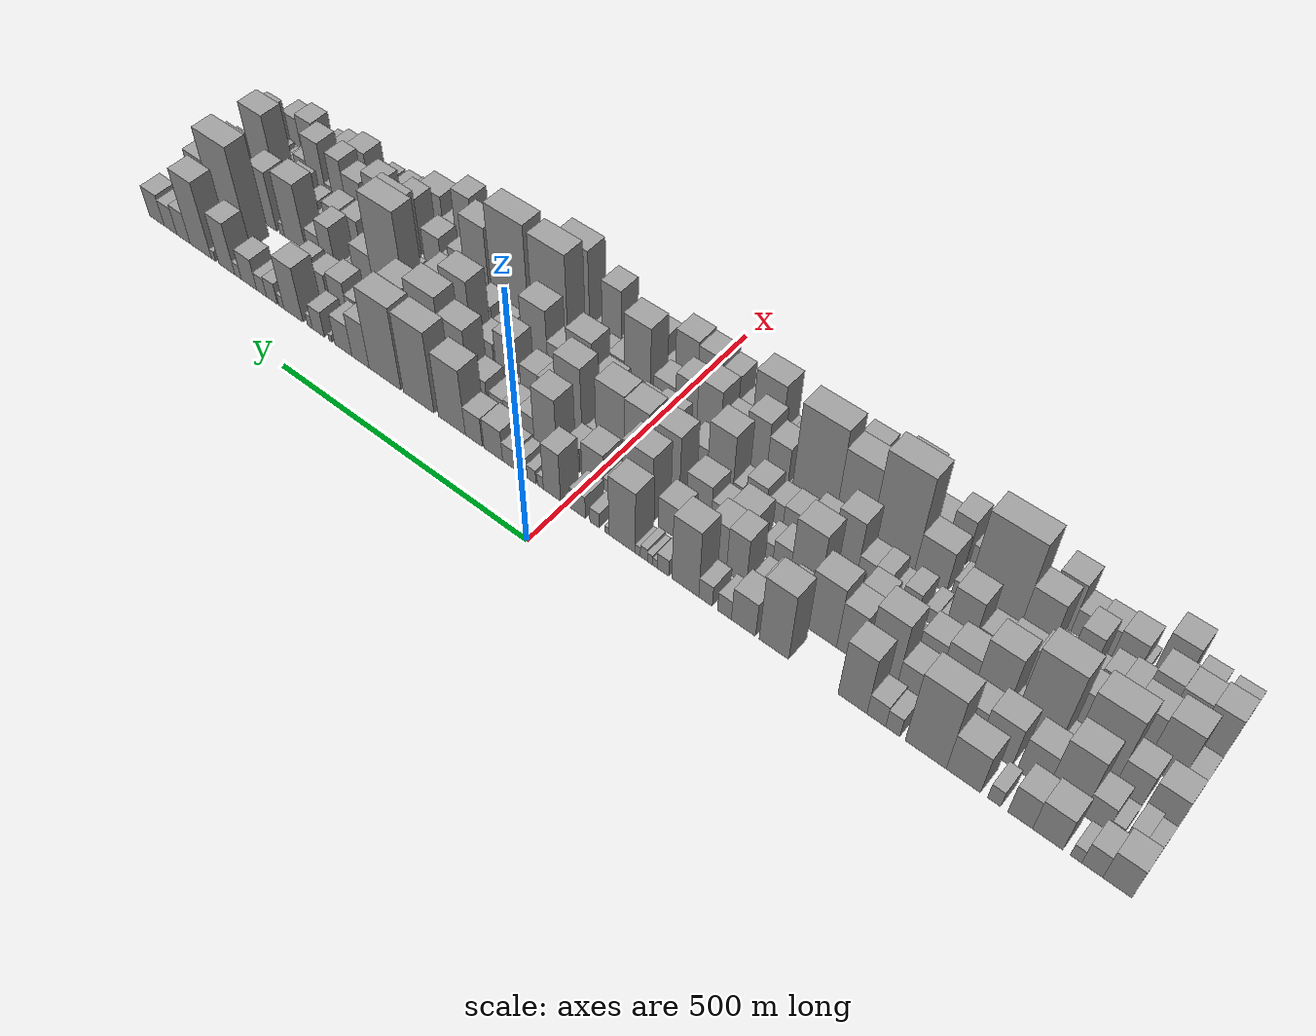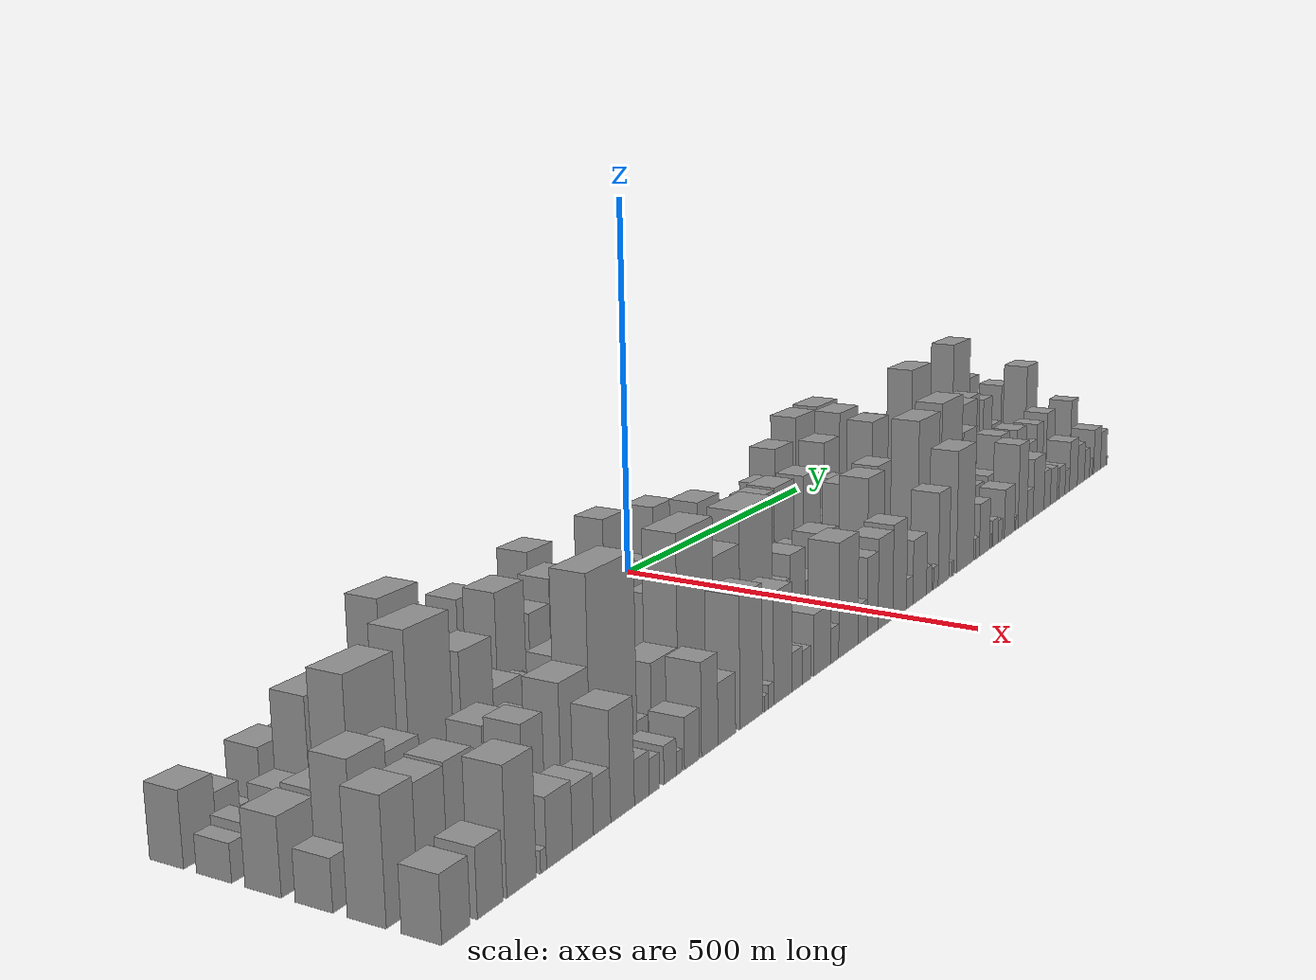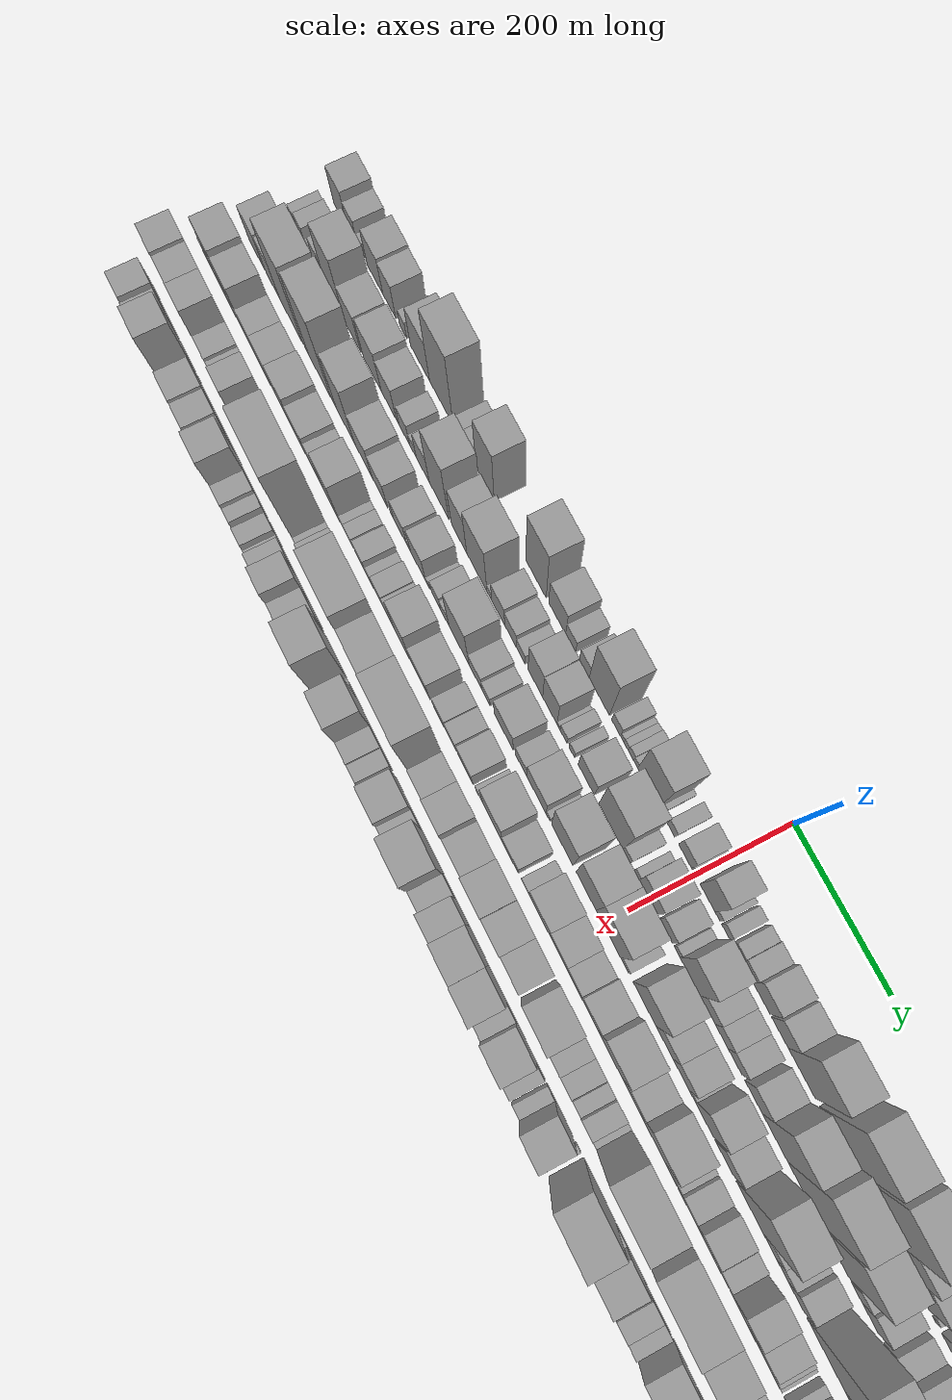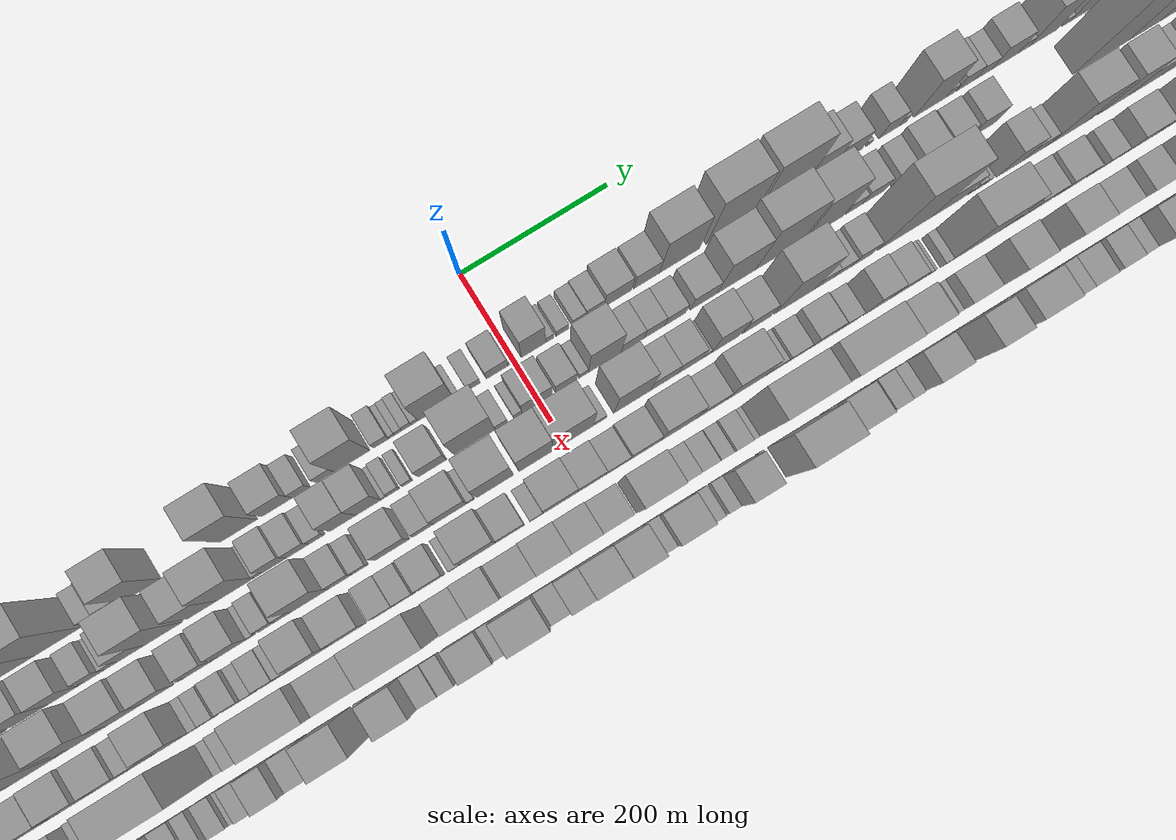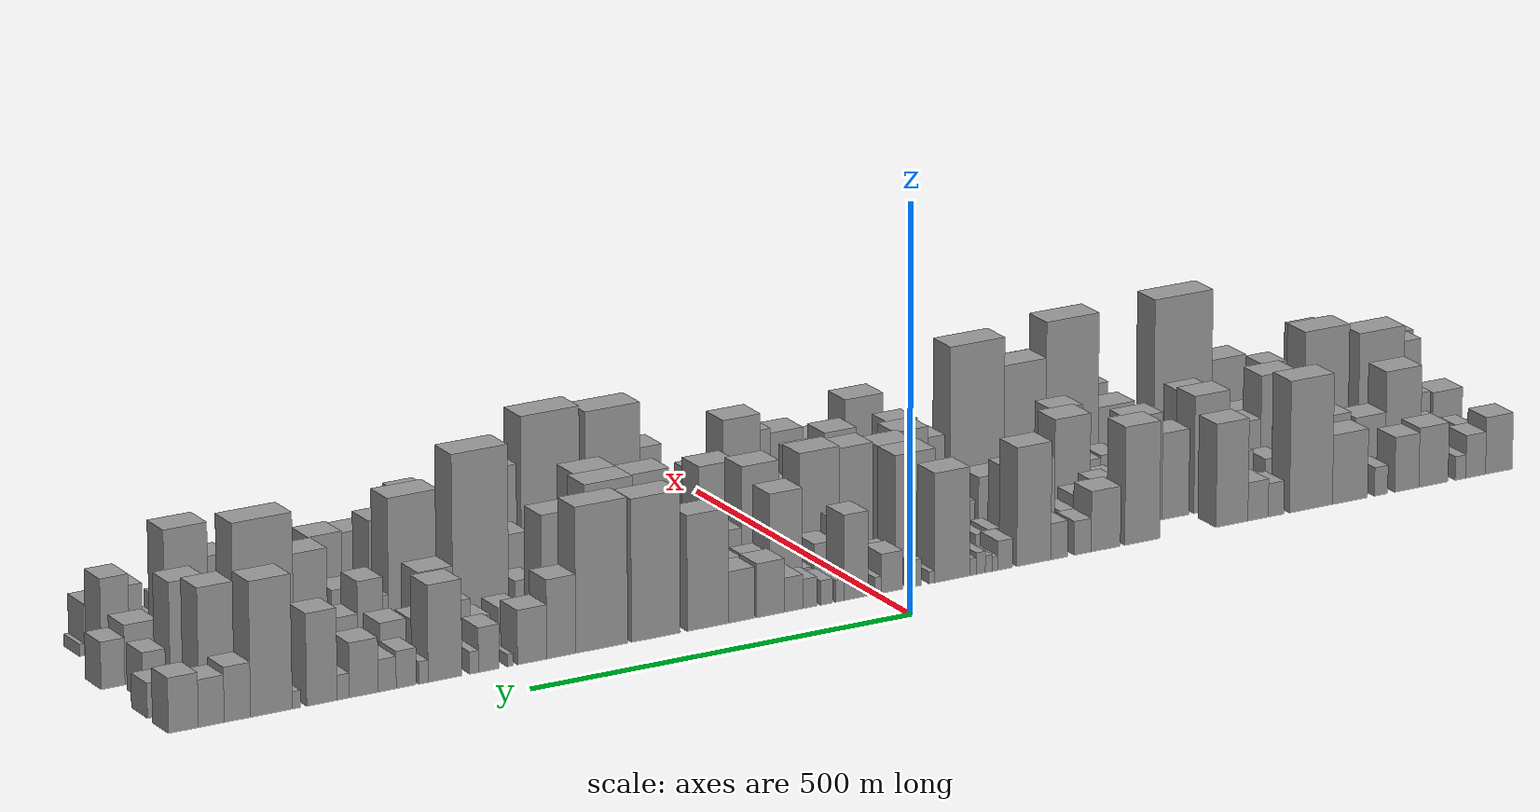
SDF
<sdf version="1.6">
 <world name="default">
  <scene>
   <sky><clouds><speed>12</speed></clouds></sky>
   <ambient>0.4 0.4 0.4 1</ambient>
   <background>0.7 0.7 0.7 1</background>
   <shadows>1</shadows>
  </scene>
  <gravity>0 0 -9.8066</gravity>
  <magnetic_field>6e-06 2.3e-05 -4.2e-05</magnetic_field>
  <physics default="0" name="default_physics" type="ode">
   <ode>
    <solver>
     <type>quick</type>
     <iters>10</iters>
     <sor>1.0</sor>
     <use_dynamic_moi_rescaling>0</use_dynamic_moi_rescaling>
    </solver>
    <constraints>
     <cfm>0</cfm>
     <erp>0.2</erp>
     <contact_max_correcting_vel>100</contact_max_correcting_vel>
     <contact_surface_layer>0.001</contact_surface_layer>
    </constraints>
   </ode>
   <max_step_size>0.004</max_step_size>
   <real_time_factor>1</real_time_factor>
   <real_time_update_rate>250</real_time_update_rate>
  </physics>
  <light name="sun" type="directional">
   <pose>0 0 10 0 0 0</pose>
   <diffuse>0.8 0.8 0.8 1</diffuse>
   <specular>0.2 0.2 0.2 1</specular>
   <attenuation>
    <range>1000</range>
    <constant>0.9</constant>
    <linear>0.01</linear>
    <quadratic>0.001</quadratic>
   </attenuation>
   <direction>-0.5 0.1 -0.9</direction>
  </light>
  <model name="building_1">
   <static>1</static>
   <pose>100.0000 -870.6648 0 0.000000 0.000000 0.000000</pose>
   <link name="link">
    <pose>0 0 36.00 0 0 0</pose>
    <collision name="collision"><geometry><box><size>40.0000 38.6703 72.0000</size></box></geometry></collision>
    <visual name="visual">
     <cast_shadows>0</cast_shadows>
     <geometry><box><size>40.0000 38.6703 72.0000</size></box></geometry>
     <material>
      <script>
       <uri>model://grey_wall/materials/scripts</uri>
       <uri>model://grey_wall/materials/textures</uri>
       <name>vrc/grey_wall</name>
      </script>
     </material>
    </visual>
   </link>
  </model>
  <model name="building_2">
   <static>1</static>
   <pose>100.0000 -837.1453 0 0.000000 0.000000 0.000000</pose>
   <link name="link">
    <pose>0 0 27.00 0 0 0</pose>
    <collision name="collision"><geometry><box><size>40.0000 28.3688 54.0000</size></box></geometry></collision>
    <visual name="visual">
     <cast_shadows>0</cast_shadows>
     <geometry><box><size>40.0000 28.3688 54.0000</size></box></geometry>
     <material>
      <script>
       <uri>model://grey_wall/materials/scripts</uri>
       <uri>model://grey_wall/materials/textures</uri>
       <name>vrc/grey_wall</name>
      </script>
     </material>
    </visual>
   </link>
  </model>
  <model name="building_3">
   <static>1</static>
   <pose>100.0000 -815.2428 0 0.000000 0.000000 0.000000</pose>
   <link name="link">
    <pose>0 0 15.00 0 0 0</pose>
    <collision name="collision"><geometry><box><size>40.0000 15.4361 30.0000</size></box></geometry></collision>
    <visual name="visual">
     <cast_shadows>0</cast_shadows>
     <geometry><box><size>40.0000 15.4361 30.0000</size></box></geometry>
     <material>
      <script>
       <uri>model://grey_wall/materials/scripts</uri>
       <uri>model://grey_wall/materials/textures</uri>
       <name>vrc/grey_wall</name>
      </script>
     </material>
    </visual>
   </link>
  </model>
  <model name="building_4">
   <static>1</static>
   <pose>100.0000 -776.5197 0 0.000000 0.000000 0.000000</pose>
   <link name="link">
    <pose>0 0 37.50 0 0 0</pose>
    <collision name="collision"><geometry><box><size>40.0000 42.0102 75.0000</size></box></geometry></collision>
    <visual name="visual">
     <cast_shadows>0</cast_shadows>
     <geometry><box><size>40.0000 42.0102 75.0000</size></box></geometry>
     <material>
      <script>
       <uri>model://grey_wall/materials/scripts</uri>
       <uri>model://grey_wall/materials/textures</uri>
       <name>vrc/grey_wall</name>
      </script>
     </material>
    </visual>
   </link>
  </model>
  <model name="building_5">
   <static>1</static>
   <pose>100.0000 -738.2272 0 0.000000 0.000000 0.000000</pose>
   <link name="link">
    <pose>0 0 34.50 0 0 0</pose>
    <collision name="collision"><geometry><box><size>40.0000 34.5749 69.0000</size></box></geometry></collision>
    <visual name="visual">
     <cast_shadows>0</cast_shadows>
     <geometry><box><size>40.0000 34.5749 69.0000</size></box></geometry>
     <material>
      <script>
       <uri>model://grey_wall/materials/scripts</uri>
       <uri>model://grey_wall/materials/textures</uri>
       <name>vrc/grey_wall</name>
      </script>
     </material>
    </visual>
   </link>
  </model>
  <model name="building_6">
   <static>1</static>
   <pose>100.0000 -701.5456 0 0.000000 0.000000 0.000000</pose>
   <link name="link">
    <pose>0 0 18.00 0 0 0</pose>
    <collision name="collision"><geometry><box><size>40.0000 18.7882 36.0000</size></box></geometry></collision>
    <visual name="visual">
     <cast_shadows>0</cast_shadows>
     <geometry><box><size>40.0000 18.7882 36.0000</size></box></geometry>
     <material>
      <script>
       <uri>model://grey_wall/materials/scripts</uri>
       <uri>model://grey_wall/materials/textures</uri>
       <name>vrc/grey_wall</name>
      </script>
     </material>
    </visual>
   </link>
  </model>
  <model name="building_7">
   <static>1</static>
   <pose>100.0000 -657.1755 0 0.000000 0.000000 0.000000</pose>
   <link name="link">
    <pose>0 0 43.50 0 0 0</pose>
    <collision name="collision"><geometry><box><size>40.0000 49.9519 87.0000</size></box></geometry></collision>
    <visual name="visual">
     <cast_shadows>0</cast_shadows>
     <geometry><box><size>40.0000 49.9519 87.0000</size></box></geometry>
     <material>
      <script>
       <uri>model://grey_wall/materials/scripts</uri>
       <uri>model://grey_wall/materials/textures</uri>
       <name>vrc/grey_wall</name>
      </script>
     </material>
    </visual>
   </link>
  </model>
  <model name="building_8">
   <static>1</static>
   <pose>100.0000 -601.8384 0 0.000000 0.000000 0.000000</pose>
   <link name="link">
    <pose>0 0 82.50 0 0 0</pose>
    <collision name="collision"><geometry><box><size>40.0000 60.7224 165.0000</size></box></geometry></collision>
    <visual name="visual">
     <cast_shadows>0</cast_shadows>
     <geometry><box><size>40.0000 60.7224 165.0000</size></box></geometry>
     <material>
      <script>
       <uri>model://grey_wall/materials/scripts</uri>
       <uri>model://grey_wall/materials/textures</uri>
       <name>vrc/grey_wall</name>
      </script>
     </material>
    </visual>
   </link>
  </model>
  <model name="building_9">
   <static>1</static>
   <pose>100.0000 -552.5471 0 0.000000 0.000000 0.000000</pose>
   <link name="link">
    <pose>0 0 21.00 0 0 0</pose>
    <collision name="collision"><geometry><box><size>40.0000 21.8601 42.0000</size></box></geometry></collision>
    <visual name="visual">
     <cast_shadows>0</cast_shadows>
     <geometry><box><size>40.0000 21.8601 42.0000</size></box></geometry>
     <material>
      <script>
       <uri>model://grey_wall/materials/scripts</uri>
       <uri>model://grey_wall/materials/textures</uri>
       <name>vrc/grey_wall</name>
      </script>
     </material>
    </visual>
   </link>
  </model>
  <model name="building_10">
   <static>1</static>
   <pose>100.0000 -527.2935 0 0.000000 0.000000 0.000000</pose>
   <link name="link">
    <pose>0 0 24.00 0 0 0</pose>
    <collision name="collision"><geometry><box><size>40.0000 28.6470 48.0000</size></box></geometry></collision>
    <visual name="visual">
     <cast_shadows>0</cast_shadows>
     <geometry><box><size>40.0000 28.6470 48.0000</size></box></geometry>
     <material>
      <script>
       <uri>model://grey_wall/materials/scripts</uri>
       <uri>model://grey_wall/materials/textures</uri>
       <name>vrc/grey_wall</name>
      </script>
     </material>
    </visual>
   </link>
  </model>
  <model name="building_11">
   <static>1</static>
   <pose>100.0000 -490.5533 0 0.000000 0.000000 0.000000</pose>
   <link name="link">
    <pose>0 0 64.50 0 0 0</pose>
    <collision name="collision"><geometry><box><size>40.0000 44.8334 129.0000</size></box></geometry></collision>
    <visual name="visual">
     <cast_shadows>0</cast_shadows>
     <geometry><box><size>40.0000 44.8334 129.0000</size></box></geometry>
     <material>
      <script>
       <uri>model://grey_wall/materials/scripts</uri>
       <uri>model://grey_wall/materials/textures</uri>
       <name>vrc/grey_wall</name>
      </script>
     </material>
    </visual>
   </link>
  </model>
  <model name="building_12">
   <static>1</static>
   <pose>100.0000 -365.3089 0 0.000000 0.000000 0.000000</pose>
   <link name="link">
    <pose>0 0 73.50 0 0 0</pose>
    <collision name="collision"><geometry><box><size>40.0000 48.5518 147.0000</size></box></geometry></collision>
    <visual name="visual">
     <cast_shadows>0</cast_shadows>
     <geometry><box><size>40.0000 48.5518 147.0000</size></box></geometry>
     <material>
      <script>
       <uri>model://grey_wall/materials/scripts</uri>
       <uri>model://grey_wall/materials/textures</uri>
       <name>vrc/grey_wall</name>
      </script>
     </material>
    </visual>
   </link>
  </model>
  <model name="building_13">
   <static>1</static>
   <pose>100.0000 -314.8790 0 0.000000 0.000000 0.000000</pose>
   <link name="link">
    <pose>0 0 37.50 0 0 0</pose>
    <collision name="collision"><geometry><box><size>40.0000 40.3081 75.0000</size></box></geometry></collision>
    <visual name="visual">
     <cast_shadows>0</cast_shadows>
     <geometry><box><size>40.0000 40.3081 75.0000</size></box></geometry>
     <material>
      <script>
       <uri>model://grey_wall/materials/scripts</uri>
       <uri>model://grey_wall/materials/textures</uri>
       <name>vrc/grey_wall</name>
      </script>
     </material>
    </visual>
   </link>
  </model>
  <model name="building_14">
   <static>1</static>
   <pose>100.0000 -283.0993 0 0.000000 0.000000 0.000000</pose>
   <link name="link">
    <pose>0 0 21.00 0 0 0</pose>
    <collision name="collision"><geometry><box><size>40.0000 23.2512 42.0000</size></box></geometry></collision>
    <visual name="visual">
     <cast_shadows>0</cast_shadows>
     <geometry><box><size>40.0000 23.2512 42.0000</size></box></geometry>
     <material>
      <script>
       <uri>model://grey_wall/materials/scripts</uri>
       <uri>model://grey_wall/materials/textures</uri>
       <name>vrc/grey_wall</name>
      </script>
     </material>
    </visual>
   </link>
  </model>
  <model name="building_15">
   <static>1</static>
   <pose>100.0000 -250.8679 0 0.000000 0.000000 0.000000</pose>
   <link name="link">
    <pose>0 0 22.50 0 0 0</pose>
    <collision name="collision"><geometry><box><size>40.0000 23.2116 45.0000</size></box></geometry></collision>
    <visual name="visual">
     <cast_shadows>0</cast_shadows>
     <geometry><box><size>40.0000 23.2116 45.0000</size></box></geometry>
     <material>
      <script>
       <uri>model://grey_wall/materials/scripts</uri>
       <uri>model://grey_wall/materials/textures</uri>
       <name>vrc/grey_wall</name>
      </script>
     </material>
    </visual>
   </link>
  </model>
  <model name="building_16">
   <static>1</static>
   <pose>100.0000 -215.7812 0 0.000000 0.000000 0.000000</pose>
   <link name="link">
    <pose>0 0 73.50 0 0 0</pose>
    <collision name="collision"><geometry><box><size>40.0000 46.9617 147.0000</size></box></geometry></collision>
    <visual name="visual">
     <cast_shadows>0</cast_shadows>
     <geometry><box><size>40.0000 46.9617 147.0000</size></box></geometry>
     <material>
      <script>
       <uri>model://grey_wall/materials/scripts</uri>
       <uri>model://grey_wall/materials/textures</uri>
       <name>vrc/grey_wall</name>
      </script>
     </material>
    </visual>
   </link>
  </model>
  <model name="building_17">
   <static>1</static>
   <pose>100.0000 -177.0466 0 0.000000 0.000000 0.000000</pose>
   <link name="link">
    <pose>0 0 18.00 0 0 0</pose>
    <collision name="collision"><geometry><box><size>40.0000 20.5076 36.0000</size></box></geometry></collision>
    <visual name="visual">
     <cast_shadows>0</cast_shadows>
     <geometry><box><size>40.0000 20.5076 36.0000</size></box></geometry>
     <material>
      <script>
       <uri>model://grey_wall/materials/scripts</uri>
       <uri>model://grey_wall/materials/textures</uri>
       <name>vrc/grey_wall</name>
      </script>
     </material>
    </visual>
   </link>
  </model>
  <model name="building_18">
   <static>1</static>
   <pose>100.0000 -163.0184 0 0.000000 0.000000 0.000000</pose>
   <link name="link">
    <pose>0 0 9.00 0 0 0</pose>
    <collision name="collision"><geometry><box><size>40.0000 7.5488 18.0000</size></box></geometry></collision>
    <visual name="visual">
     <cast_shadows>0</cast_shadows>
     <geometry><box><size>40.0000 7.5488 18.0000</size></box></geometry>
     <material>
      <script>
       <uri>model://grey_wall/materials/scripts</uri>
       <uri>model://grey_wall/materials/textures</uri>
       <name>vrc/grey_wall</name>
      </script>
     </material>
    </visual>
   </link>
  </model>
  <model name="building_19">
   <static>1</static>
   <pose>100.0000 -154.2603 0 0.000000 0.000000 0.000000</pose>
   <link name="link">
    <pose>0 0 10.50 0 0 0</pose>
    <collision name="collision"><geometry><box><size>40.0000 9.9674 21.0000</size></box></geometry></collision>
    <visual name="visual">
     <cast_shadows>0</cast_shadows>
     <geometry><box><size>40.0000 9.9674 21.0000</size></box></geometry>
     <material>
      <script>
       <uri>model://grey_wall/materials/scripts</uri>
       <uri>model://grey_wall/materials/textures</uri>
       <name>vrc/grey_wall</name>
      </script>
     </material>
    </visual>
   </link>
  </model>
  <model name="building_20">
   <static>1</static>
   <pose>100.0000 -143.1152 0 0.000000 0.000000 0.000000</pose>
   <link name="link">
    <pose>0 0 13.50 0 0 0</pose>
    <collision name="collision"><geometry><box><size>40.0000 12.3230 27.0000</size></box></geometry></collision>
    <visual name="visual">
     <cast_shadows>0</cast_shadows>
     <geometry><box><size>40.0000 12.3230 27.0000</size></box></geometry>
     <material>
      <script>
       <uri>model://grey_wall/materials/scripts</uri>
       <uri>model://grey_wall/materials/textures</uri>
       <name>vrc/grey_wall</name>
      </script>
     </material>
    </visual>
   </link>
  </model>
  <model name="building_21">
   <static>1</static>
   <pose>100.0000 -132.4435 0 0.000000 0.000000 0.000000</pose>
   <link name="link">
    <pose>0 0 10.50 0 0 0</pose>
    <collision name="collision"><geometry><box><size>40.0000 9.0203 21.0000</size></box></geometry></collision>
    <visual name="visual">
     <cast_shadows>0</cast_shadows>
     <geometry><box><size>40.0000 9.0203 21.0000</size></box></geometry>
     <material>
      <script>
       <uri>model://grey_wall/materials/scripts</uri>
       <uri>model://grey_wall/materials/textures</uri>
       <name>vrc/grey_wall</name>
      </script>
     </material>
    </visual>
   </link>
  </model>
  <model name="building_22">
   <static>1</static>
   <pose>100.0000 -104.0287 0 0.000000 0.000000 0.000000</pose>
   <link name="link">
    <pose>0 0 67.50 0 0 0</pose>
    <collision name="collision"><geometry><box><size>40.0000 47.8095 135.0000</size></box></geometry></collision>
    <visual name="visual">
     <cast_shadows>0</cast_shadows>
     <geometry><box><size>40.0000 47.8095 135.0000</size></box></geometry>
     <material>
      <script>
       <uri>model://grey_wall/materials/scripts</uri>
       <uri>model://grey_wall/materials/textures</uri>
       <name>vrc/grey_wall</name>
      </script>
     </material>
    </visual>
   </link>
  </model>
  <model name="building_23">
   <static>1</static>
   <pose>100.0000 -76.4820 0 0.000000 0.000000 0.000000</pose>
   <link name="link">
    <pose>0 0 7.50 0 0 0</pose>
    <collision name="collision"><geometry><box><size>40.0000 7.2839 15.0000</size></box></geometry></collision>
    <visual name="visual">
     <cast_shadows>0</cast_shadows>
     <geometry><box><size>40.0000 7.2839 15.0000</size></box></geometry>
     <material>
      <script>
       <uri>model://grey_wall/materials/scripts</uri>
       <uri>model://grey_wall/materials/textures</uri>
       <name>vrc/grey_wall</name>
      </script>
     </material>
    </visual>
   </link>
  </model>
  <model name="building_24">
   <static>1</static>
   <pose>100.0000 -53.9231 0 0.000000 0.000000 0.000000</pose>
   <link name="link">
    <pose>0 0 16.50 0 0 0</pose>
    <collision name="collision"><geometry><box><size>40.0000 17.8339 33.0000</size></box></geometry></collision>
    <visual name="visual">
     <cast_shadows>0</cast_shadows>
     <geometry><box><size>40.0000 17.8339 33.0000</size></box></geometry>
     <material>
      <script>
       <uri>model://grey_wall/materials/scripts</uri>
       <uri>model://grey_wall/materials/textures</uri>
       <name>vrc/grey_wall</name>
      </script>
     </material>
    </visual>
   </link>
  </model>
  <model name="building_25">
   <static>1</static>
   <pose>100.0000 -22.7039 0 0.000000 0.000000 0.000000</pose>
   <link name="link">
    <pose>0 0 24.00 0 0 0</pose>
    <collision name="collision"><geometry><box><size>40.0000 28.6043 48.0000</size></box></geometry></collision>
    <visual name="visual">
     <cast_shadows>0</cast_shadows>
     <geometry><box><size>40.0000 28.6043 48.0000</size></box></geometry>
     <material>
      <script>
       <uri>model://grey_wall/materials/scripts</uri>
       <uri>model://grey_wall/materials/textures</uri>
       <name>vrc/grey_wall</name>
      </script>
     </material>
    </visual>
   </link>
  </model>
  <model name="building_26">
   <static>1</static>
   <pose>100.0000 -3.8357 0 0.000000 0.000000 0.000000</pose>
   <link name="link">
    <pose>0 0 10.50 0 0 0</pose>
    <collision name="collision"><geometry><box><size>40.0000 9.1322 21.0000</size></box></geometry></collision>
    <visual name="visual">
     <cast_shadows>0</cast_shadows>
     <geometry><box><size>40.0000 9.1322 21.0000</size></box></geometry>
     <material>
      <script>
       <uri>model://grey_wall/materials/scripts</uri>
       <uri>model://grey_wall/materials/textures</uri>
       <name>vrc/grey_wall</name>
      </script>
     </material>
    </visual>
   </link>
  </model>
  <model name="building_27">
   <static>1</static>
   <pose>100.0000 26.0662 0 0.000000 0.000000 0.000000</pose>
   <link name="link">
    <pose>0 0 52.50 0 0 0</pose>
    <collision name="collision"><geometry><box><size>40.0000 32.6717 105.0000</size></box></geometry></collision>
    <visual name="visual">
     <cast_shadows>0</cast_shadows>
     <geometry><box><size>40.0000 32.6717 105.0000</size></box></geometry>
     <material>
      <script>
       <uri>model://grey_wall/materials/scripts</uri>
       <uri>model://grey_wall/materials/textures</uri>
       <name>vrc/grey_wall</name>
      </script>
     </material>
    </visual>
   </link>
  </model>
  <model name="building_28">
   <static>1</static>
   <pose>100.0000 47.9995 0 0.000000 0.000000 0.000000</pose>
   <link name="link">
    <pose>0 0 13.50 0 0 0</pose>
    <collision name="collision"><geometry><box><size>40.0000 11.1949 27.0000</size></box></geometry></collision>
    <visual name="visual">
     <cast_shadows>0</cast_shadows>
     <geometry><box><size>40.0000 11.1949 27.0000</size></box></geometry>
     <material>
      <script>
       <uri>model://grey_wall/materials/scripts</uri>
       <uri>model://grey_wall/materials/textures</uri>
       <name>vrc/grey_wall</name>
      </script>
     </material>
    </visual>
   </link>
  </model>
  <model name="building_29">
   <static>1</static>
   <pose>100.0000 65.0719 0 0.000000 0.000000 0.000000</pose>
   <link name="link">
    <pose>0 0 15.00 0 0 0</pose>
    <collision name="collision"><geometry><box><size>40.0000 16.9499 30.0000</size></box></geometry></collision>
    <visual name="visual">
     <cast_shadows>0</cast_shadows>
     <geometry><box><size>40.0000 16.9499 30.0000</size></box></geometry>
     <material>
      <script>
       <uri>model://grey_wall/materials/scripts</uri>
       <uri>model://grey_wall/materials/textures</uri>
       <name>vrc/grey_wall</name>
      </script>
     </material>
    </visual>
   </link>
  </model>
  <model name="building_30">
   <static>1</static>
   <pose>100.0000 87.8286 0 0.000000 0.000000 0.000000</pose>
   <link name="link">
    <pose>0 0 18.00 0 0 0</pose>
    <collision name="collision"><geometry><box><size>40.0000 18.5635 36.0000</size></box></geometry></collision>
    <visual name="visual">
     <cast_shadows>0</cast_shadows>
     <geometry><box><size>40.0000 18.5635 36.0000</size></box></geometry>
     <material>
      <script>
       <uri>model://grey_wall/materials/scripts</uri>
       <uri>model://grey_wall/materials/textures</uri>
       <name>vrc/grey_wall</name>
      </script>
     </material>
    </visual>
   </link>
  </model>
  <model name="building_31">
   <static>1</static>
   <pose>100.0000 109.3706 0 0.000000 0.000000 0.000000</pose>
   <link name="link">
    <pose>0 0 21.00 0 0 0</pose>
    <collision name="collision"><geometry><box><size>40.0000 24.5204 42.0000</size></box></geometry></collision>
    <visual name="visual">
     <cast_shadows>0</cast_shadows>
     <geometry><box><size>40.0000 24.5204 42.0000</size></box></geometry>
     <material>
      <script>
       <uri>model://grey_wall/materials/scripts</uri>
       <uri>model://grey_wall/materials/textures</uri>
       <name>vrc/grey_wall</name>
      </script>
     </material>
    </visual>
   </link>
  </model>
  <model name="building_32">
   <static>1</static>
   <pose>100.0000 140.1107 0 0.000000 0.000000 0.000000</pose>
   <link name="link">
    <pose>0 0 33.00 0 0 0</pose>
    <collision name="collision"><geometry><box><size>40.0000 36.9599 66.0000</size></box></geometry></collision>
    <visual name="visual">
     <cast_shadows>0</cast_shadows>
     <geometry><box><size>40.0000 36.9599 66.0000</size></box></geometry>
     <material>
      <script>
       <uri>model://grey_wall/materials/scripts</uri>
       <uri>model://grey_wall/materials/textures</uri>
       <name>vrc/grey_wall</name>
      </script>
     </material>
    </visual>
   </link>
  </model>
  <model name="building_33">
   <static>1</static>
   <pose>100.0000 178.7573 0 0.000000 0.000000 0.000000</pose>
   <link name="link">
    <pose>0 0 31.50 0 0 0</pose>
    <collision name="collision"><geometry><box><size>40.0000 34.3332 63.0000</size></box></geometry></collision>
    <visual name="visual">
     <cast_shadows>0</cast_shadows>
     <geometry><box><size>40.0000 34.3332 63.0000</size></box></geometry>
     <material>
      <script>
       <uri>model://grey_wall/materials/scripts</uri>
       <uri>model://grey_wall/materials/textures</uri>
       <name>vrc/grey_wall</name>
      </script>
     </material>
    </visual>
   </link>
  </model>
  <model name="building_34">
   <static>1</static>
   <pose>100.0000 223.4274 0 0.000000 0.000000 0.000000</pose>
   <link name="link">
    <pose>0 0 70.50 0 0 0</pose>
    <collision name="collision"><geometry><box><size>40.0000 55.0071 141.0000</size></box></geometry></collision>
    <visual name="visual">
     <cast_shadows>0</cast_shadows>
     <geometry><box><size>40.0000 55.0071 141.0000</size></box></geometry>
     <material>
      <script>
       <uri>model://grey_wall/materials/scripts</uri>
       <uri>model://grey_wall/materials/textures</uri>
       <name>vrc/grey_wall</name>
      </script>
     </material>
    </visual>
   </link>
  </model>
  <model name="building_35">
   <static>1</static>
   <pose>100.0000 292.1436 0 0.000000 0.000000 0.000000</pose>
   <link name="link">
    <pose>0 0 87.00 0 0 0</pose>
    <collision name="collision"><geometry><box><size>40.0000 64.4253 174.0000</size></box></geometry></collision>
    <visual name="visual">
     <cast_shadows>0</cast_shadows>
     <geometry><box><size>40.0000 64.4253 174.0000</size></box></geometry>
     <material>
      <script>
       <uri>model://grey_wall/materials/scripts</uri>
       <uri>model://grey_wall/materials/textures</uri>
       <name>vrc/grey_wall</name>
      </script>
     </material>
    </visual>
   </link>
  </model>
  <model name="building_36">
   <static>1</static>
   <pose>100.0000 363.3790 0 0.000000 0.000000 0.000000</pose>
   <link name="link">
    <pose>0 0 88.50 0 0 0</pose>
    <collision name="collision"><geometry><box><size>40.0000 68.0455 177.0000</size></box></geometry></collision>
    <visual name="visual">
     <cast_shadows>0</cast_shadows>
     <geometry><box><size>40.0000 68.0455 177.0000</size></box></geometry>
     <material>
      <script>
       <uri>model://grey_wall/materials/scripts</uri>
       <uri>model://grey_wall/materials/textures</uri>
       <name>vrc/grey_wall</name>
      </script>
     </material>
    </visual>
   </link>
  </model>
  <model name="building_37">
   <static>1</static>
   <pose>100.0000 416.3116 0 0.000000 0.000000 0.000000</pose>
   <link name="link">
    <pose>0 0 48.00 0 0 0</pose>
    <collision name="collision"><geometry><box><size>40.0000 37.8197 96.0000</size></box></geometry></collision>
    <visual name="visual">
     <cast_shadows>0</cast_shadows>
     <geometry><box><size>40.0000 37.8197 96.0000</size></box></geometry>
     <material>
      <script>
       <uri>model://grey_wall/materials/scripts</uri>
       <uri>model://grey_wall/materials/textures</uri>
       <name>vrc/grey_wall</name>
      </script>
     </material>
    </visual>
   </link>
  </model>
  <model name="building_38">
   <static>1</static>
   <pose>100.0000 454.2458 0 0.000000 0.000000 0.000000</pose>
   <link name="link">
    <pose>0 0 33.00 0 0 0</pose>
    <collision name="collision"><geometry><box><size>40.0000 38.0487 66.0000</size></box></geometry></collision>
    <visual name="visual">
     <cast_shadows>0</cast_shadows>
     <geometry><box><size>40.0000 38.0487 66.0000</size></box></geometry>
     <material>
      <script>
       <uri>model://grey_wall/materials/scripts</uri>
       <uri>model://grey_wall/materials/textures</uri>
       <name>vrc/grey_wall</name>
      </script>
     </material>
    </visual>
   </link>
  </model>
  <model name="building_39">
   <static>1</static>
   <pose>100.0000 482.8758 0 0.000000 0.000000 0.000000</pose>
   <link name="link">
    <pose>0 0 7.50 0 0 0</pose>
    <collision name="collision"><geometry><box><size>40.0000 7.2112 15.0000</size></box></geometry></collision>
    <visual name="visual">
     <cast_shadows>0</cast_shadows>
     <geometry><box><size>40.0000 7.2112 15.0000</size></box></geometry>
     <material>
      <script>
       <uri>model://grey_wall/materials/scripts</uri>
       <uri>model://grey_wall/materials/textures</uri>
       <name>vrc/grey_wall</name>
      </script>
     </material>
    </visual>
   </link>
  </model>
  <model name="building_40">
   <static>1</static>
   <pose>100.0000 510.1323 0 0.000000 0.000000 0.000000</pose>
   <link name="link">
    <pose>0 0 27.00 0 0 0</pose>
    <collision name="collision"><geometry><box><size>40.0000 27.3020 54.0000</size></box></geometry></collision>
    <visual name="visual">
     <cast_shadows>0</cast_shadows>
     <geometry><box><size>40.0000 27.3020 54.0000</size></box></geometry>
     <material>
      <script>
       <uri>model://grey_wall/materials/scripts</uri>
       <uri>model://grey_wall/materials/textures</uri>
       <name>vrc/grey_wall</name>
      </script>
     </material>
    </visual>
   </link>
  </model>
  <model name="building_41">
   <static>1</static>
   <pose>100.0000 529.4038 0 0.000000 0.000000 0.000000</pose>
   <link name="link">
    <pose>0 0 13.50 0 0 0</pose>
    <collision name="collision"><geometry><box><size>40.0000 11.2409 27.0000</size></box></geometry></collision>
    <visual name="visual">
     <cast_shadows>0</cast_shadows>
     <geometry><box><size>40.0000 11.2409 27.0000</size></box></geometry>
     <material>
      <script>
       <uri>model://grey_wall/materials/scripts</uri>
       <uri>model://grey_wall/materials/textures</uri>
       <name>vrc/grey_wall</name>
      </script>
     </material>
    </visual>
   </link>
  </model>
  <model name="building_42">
   <static>1</static>
   <pose>100.0000 566.7996 0 0.000000 0.000000 0.000000</pose>
   <link name="link">
    <pose>0 0 58.50 0 0 0</pose>
    <collision name="collision"><geometry><box><size>40.0000 43.5507 117.0000</size></box></geometry></collision>
    <visual name="visual">
     <cast_shadows>0</cast_shadows>
     <geometry><box><size>40.0000 43.5507 117.0000</size></box></geometry>
     <material>
      <script>
       <uri>model://grey_wall/materials/scripts</uri>
       <uri>model://grey_wall/materials/textures</uri>
       <name>vrc/grey_wall</name>
      </script>
     </material>
    </visual>
   </link>
  </model>
  <model name="building_43">
   <static>1</static>
   <pose>100.0000 594.6401 0 0.000000 0.000000 0.000000</pose>
   <link name="link">
    <pose>0 0 13.50 0 0 0</pose>
    <collision name="collision"><geometry><box><size>40.0000 12.1301 27.0000</size></box></geometry></collision>
    <visual name="visual">
     <cast_shadows>0</cast_shadows>
     <geometry><box><size>40.0000 12.1301 27.0000</size></box></geometry>
     <material>
      <script>
       <uri>model://grey_wall/materials/scripts</uri>
       <uri>model://grey_wall/materials/textures</uri>
       <name>vrc/grey_wall</name>
      </script>
     </material>
    </visual>
   </link>
  </model>
  <model name="building_44">
   <static>1</static>
   <pose>100.0000 616.6186 0 0.000000 0.000000 0.000000</pose>
   <link name="link">
    <pose>0 0 22.50 0 0 0</pose>
    <collision name="collision"><geometry><box><size>40.0000 25.8270 45.0000</size></box></geometry></collision>
    <visual name="visual">
     <cast_shadows>0</cast_shadows>
     <geometry><box><size>40.0000 25.8270 45.0000</size></box></geometry>
     <material>
      <script>
       <uri>model://grey_wall/materials/scripts</uri>
       <uri>model://grey_wall/materials/textures</uri>
       <name>vrc/grey_wall</name>
      </script>
     </material>
    </visual>
   </link>
  </model>
  <model name="building_45">
   <static>1</static>
   <pose>100.0000 641.0916 0 0.000000 0.000000 0.000000</pose>
   <link name="link">
    <pose>0 0 19.50 0 0 0</pose>
    <collision name="collision"><geometry><box><size>40.0000 23.1189 39.0000</size></box></geometry></collision>
    <visual name="visual">
     <cast_shadows>0</cast_shadows>
     <geometry><box><size>40.0000 23.1189 39.0000</size></box></geometry>
     <material>
      <script>
       <uri>model://grey_wall/materials/scripts</uri>
       <uri>model://grey_wall/materials/textures</uri>
       <name>vrc/grey_wall</name>
      </script>
     </material>
    </visual>
   </link>
  </model>
  <model name="building_46">
   <static>1</static>
   <pose>100.0000 671.0552 0 0.000000 0.000000 0.000000</pose>
   <link name="link">
    <pose>0 0 33.00 0 0 0</pose>
    <collision name="collision"><geometry><box><size>40.0000 36.8083 66.0000</size></box></geometry></collision>
    <visual name="visual">
     <cast_shadows>0</cast_shadows>
     <geometry><box><size>40.0000 36.8083 66.0000</size></box></geometry>
     <material>
      <script>
       <uri>model://grey_wall/materials/scripts</uri>
       <uri>model://grey_wall/materials/textures</uri>
       <name>vrc/grey_wall</name>
      </script>
     </material>
    </visual>
   </link>
  </model>
  <model name="building_47">
   <static>1</static>
   <pose>100.0000 697.0982 0 0.000000 0.000000 0.000000</pose>
   <link name="link">
    <pose>0 0 15.00 0 0 0</pose>
    <collision name="collision"><geometry><box><size>40.0000 15.2777 30.0000</size></box></geometry></collision>
    <visual name="visual">
     <cast_shadows>0</cast_shadows>
     <geometry><box><size>40.0000 15.2777 30.0000</size></box></geometry>
     <material>
      <script>
       <uri>model://grey_wall/materials/scripts</uri>
       <uri>model://grey_wall/materials/textures</uri>
       <name>vrc/grey_wall</name>
      </script>
     </material>
    </visual>
   </link>
  </model>
  <model name="building_48">
   <static>1</static>
   <pose>100.0000 724.2057 0 0.000000 0.000000 0.000000</pose>
   <link name="link">
    <pose>0 0 55.50 0 0 0</pose>
    <collision name="collision"><geometry><box><size>40.0000 38.9373 111.0000</size></box></geometry></collision>
    <visual name="visual">
     <cast_shadows>0</cast_shadows>
     <geometry><box><size>40.0000 38.9373 111.0000</size></box></geometry>
     <material>
      <script>
       <uri>model://grey_wall/materials/scripts</uri>
       <uri>model://grey_wall/materials/textures</uri>
       <name>vrc/grey_wall</name>
      </script>
     </material>
    </visual>
   </link>
  </model>
  <model name="building_49">
   <static>1</static>
   <pose>100.0000 756.7948 0 0.000000 0.000000 0.000000</pose>
   <link name="link">
    <pose>0 0 10.50 0 0 0</pose>
    <collision name="collision"><geometry><box><size>40.0000 10.2408 21.0000</size></box></geometry></collision>
    <visual name="visual">
     <cast_shadows>0</cast_shadows>
     <geometry><box><size>40.0000 10.2408 21.0000</size></box></geometry>
     <material>
      <script>
       <uri>model://grey_wall/materials/scripts</uri>
       <uri>model://grey_wall/materials/textures</uri>
       <name>vrc/grey_wall</name>
      </script>
     </material>
    </visual>
   </link>
  </model>
  <model name="building_50">
   <static>1</static>
   <pose>100.0000 788.2646 0 0.000000 0.000000 0.000000</pose>
   <link name="link">
    <pose>0 0 81.00 0 0 0</pose>
    <collision name="collision"><geometry><box><size>40.0000 52.6990 162.0000</size></box></geometry></collision>
    <visual name="visual">
     <cast_shadows>0</cast_shadows>
     <geometry><box><size>40.0000 52.6990 162.0000</size></box></geometry>
     <material>
      <script>
       <uri>model://grey_wall/materials/scripts</uri>
       <uri>model://grey_wall/materials/textures</uri>
       <name>vrc/grey_wall</name>
      </script>
     </material>
    </visual>
   </link>
  </model>
  <model name="building_51">
   <static>1</static>
   <pose>100.0000 831.2229 0 0.000000 0.000000 0.000000</pose>
   <link name="link">
    <pose>0 0 33.00 0 0 0</pose>
    <collision name="collision"><geometry><box><size>40.0000 33.2175 66.0000</size></box></geometry></collision>
    <visual name="visual">
     <cast_shadows>0</cast_shadows>
     <geometry><box><size>40.0000 33.2175 66.0000</size></box></geometry>
     <material>
      <script>
       <uri>model://grey_wall/materials/scripts</uri>
       <uri>model://grey_wall/materials/textures</uri>
       <name>vrc/grey_wall</name>
      </script>
     </material>
    </visual>
   </link>
  </model>
  <model name="building_52">
   <static>1</static>
   <pose>100.0000 864.0846 0 0.000000 0.000000 0.000000</pose>
   <link name="link">
    <pose>0 0 28.50 0 0 0</pose>
    <collision name="collision"><geometry><box><size>40.0000 32.5060 57.0000</size></box></geometry></collision>
    <visual name="visual">
     <cast_shadows>0</cast_shadows>
     <geometry><box><size>40.0000 32.5060 57.0000</size></box></geometry>
     <material>
      <script>
       <uri>model://grey_wall/materials/scripts</uri>
       <uri>model://grey_wall/materials/textures</uri>
       <name>vrc/grey_wall</name>
      </script>
     </material>
    </visual>
   </link>
  </model>
  <model name="building_53">
   <static>1</static>
   <pose>100.0000 899.1114 0 0.000000 0.000000 0.000000</pose>
   <link name="link">
    <pose>0 0 33.00 0 0 0</pose>
    <collision name="collision"><geometry><box><size>40.0000 37.5475 66.0000</size></box></geometry></collision>
    <visual name="visual">
     <cast_shadows>0</cast_shadows>
     <geometry><box><size>40.0000 37.5475 66.0000</size></box></geometry>
     <material>
      <script>
       <uri>model://grey_wall/materials/scripts</uri>
       <uri>model://grey_wall/materials/textures</uri>
       <name>vrc/grey_wall</name>
      </script>
     </material>
    </visual>
   </link>
  </model>
  <model name="building_54">
   <static>1</static>
   <pose>155.0000 -880.3482 0 0.000000 0.000000 0.000000</pose>
   <link name="link">
    <pose>0 0 18.00 0 0 0</pose>
    <collision name="collision"><geometry><box><size>40.0000 19.3035 36.0000</size></box></geometry></collision>
    <visual name="visual">
     <cast_shadows>0</cast_shadows>
     <geometry><box><size>40.0000 19.3035 36.0000</size></box></geometry>
     <material>
      <script>
       <uri>model://grey_wall/materials/scripts</uri>
       <uri>model://grey_wall/materials/textures</uri>
       <name>vrc/grey_wall</name>
      </script>
     </material>
    </visual>
   </link>
  </model>
  <model name="building_55">
   <static>1</static>
   <pose>155.0000 -859.4224 0 0.000000 0.000000 0.000000</pose>
   <link name="link">
    <pose>0 0 22.50 0 0 0</pose>
    <collision name="collision"><geometry><box><size>40.0000 22.5482 45.0000</size></box></geometry></collision>
    <visual name="visual">
     <cast_shadows>0</cast_shadows>
     <geometry><box><size>40.0000 22.5482 45.0000</size></box></geometry>
     <material>
      <script>
       <uri>model://grey_wall/materials/scripts</uri>
       <uri>model://grey_wall/materials/textures</uri>
       <name>vrc/grey_wall</name>
      </script>
     </material>
    </visual>
   </link>
  </model>
  <model name="building_56">
   <static>1</static>
   <pose>155.0000 -835.6119 0 0.000000 0.000000 0.000000</pose>
   <link name="link">
    <pose>0 0 15.00 0 0 0</pose>
    <collision name="collision"><geometry><box><size>40.0000 17.0728 30.0000</size></box></geometry></collision>
    <visual name="visual">
     <cast_shadows>0</cast_shadows>
     <geometry><box><size>40.0000 17.0728 30.0000</size></box></geometry>
     <material>
      <script>
       <uri>model://grey_wall/materials/scripts</uri>
       <uri>model://grey_wall/materials/textures</uri>
       <name>vrc/grey_wall</name>
      </script>
     </material>
    </visual>
   </link>
  </model>
  <model name="building_57">
   <static>1</static>
   <pose>155.0000 -810.3334 0 0.000000 0.000000 0.000000</pose>
   <link name="link">
    <pose>0 0 28.50 0 0 0</pose>
    <collision name="collision"><geometry><box><size>40.0000 33.4842 57.0000</size></box></geometry></collision>
    <visual name="visual">
     <cast_shadows>0</cast_shadows>
     <geometry><box><size>40.0000 33.4842 57.0000</size></box></geometry>
     <material>
      <script>
       <uri>model://grey_wall/materials/scripts</uri>
       <uri>model://grey_wall/materials/textures</uri>
       <name>vrc/grey_wall</name>
      </script>
     </material>
    </visual>
   </link>
  </model>
  <model name="building_58">
   <static>1</static>
   <pose>155.0000 -768.3361 0 0.000000 0.000000 0.000000</pose>
   <link name="link">
    <pose>0 0 66.00 0 0 0</pose>
    <collision name="collision"><geometry><box><size>40.0000 50.5103 132.0000</size></box></geometry></collision>
    <visual name="visual">
     <cast_shadows>0</cast_shadows>
     <geometry><box><size>40.0000 50.5103 132.0000</size></box></geometry>
     <material>
      <script>
       <uri>model://grey_wall/materials/scripts</uri>
       <uri>model://grey_wall/materials/textures</uri>
       <name>vrc/grey_wall</name>
      </script>
     </material>
    </visual>
   </link>
  </model>
  <model name="building_59">
   <static>1</static>
   <pose>155.0000 -721.6624 0 0.000000 0.000000 0.000000</pose>
   <link name="link">
    <pose>0 0 40.50 0 0 0</pose>
    <collision name="collision"><geometry><box><size>40.0000 42.8372 81.0000</size></box></geometry></collision>
    <visual name="visual">
     <cast_shadows>0</cast_shadows>
     <geometry><box><size>40.0000 42.8372 81.0000</size></box></geometry>
     <material>
      <script>
       <uri>model://grey_wall/materials/scripts</uri>
       <uri>model://grey_wall/materials/textures</uri>
       <name>vrc/grey_wall</name>
      </script>
     </material>
    </visual>
   </link>
  </model>
  <model name="building_60">
   <static>1</static>
   <pose>155.0000 -669.4740 0 0.000000 0.000000 0.000000</pose>
   <link name="link">
    <pose>0 0 45.00 0 0 0</pose>
    <collision name="collision"><geometry><box><size>40.0000 47.5394 90.0000</size></box></geometry></collision>
    <visual name="visual">
     <cast_shadows>0</cast_shadows>
     <geometry><box><size>40.0000 47.5394 90.0000</size></box></geometry>
     <material>
      <script>
       <uri>model://grey_wall/materials/scripts</uri>
       <uri>model://grey_wall/materials/textures</uri>
       <name>vrc/grey_wall</name>
      </script>
     </material>
    </visual>
   </link>
  </model>
  <model name="building_61">
   <static>1</static>
   <pose>155.0000 -625.9835 0 0.000000 0.000000 0.000000</pose>
   <link name="link">
    <pose>0 0 37.50 0 0 0</pose>
    <collision name="collision"><geometry><box><size>40.0000 39.4417 75.0000</size></box></geometry></collision>
    <visual name="visual">
     <cast_shadows>0</cast_shadows>
     <geometry><box><size>40.0000 39.4417 75.0000</size></box></geometry>
     <material>
      <script>
       <uri>model://grey_wall/materials/scripts</uri>
       <uri>model://grey_wall/materials/textures</uri>
       <name>vrc/grey_wall</name>
      </script>
     </material>
    </visual>
   </link>
  </model>
  <model name="building_62">
   <static>1</static>
   <pose>155.0000 -602.6160 0 0.000000 0.000000 0.000000</pose>
   <link name="link">
    <pose>0 0 7.50 0 0 0</pose>
    <collision name="collision"><geometry><box><size>40.0000 7.2933 15.0000</size></box></geometry></collision>
    <visual name="visual">
     <cast_shadows>0</cast_shadows>
     <geometry><box><size>40.0000 7.2933 15.0000</size></box></geometry>
     <material>
      <script>
       <uri>model://grey_wall/materials/scripts</uri>
       <uri>model://grey_wall/materials/textures</uri>
       <name>vrc/grey_wall</name>
      </script>
     </material>
    </visual>
   </link>
  </model>
  <model name="building_63">
   <static>1</static>
   <pose>155.0000 -585.5089 0 0.000000 0.000000 0.000000</pose>
   <link name="link">
    <pose>0 0 25.50 0 0 0</pose>
    <collision name="collision"><geometry><box><size>40.0000 26.9209 51.0000</size></box></geometry></collision>
    <visual name="visual">
     <cast_shadows>0</cast_shadows>
     <geometry><box><size>40.0000 26.9209 51.0000</size></box></geometry>
     <material>
      <script>
       <uri>model://grey_wall/materials/scripts</uri>
       <uri>model://grey_wall/materials/textures</uri>
       <name>vrc/grey_wall</name>
      </script>
     </material>
    </visual>
   </link>
  </model>
  <model name="building_64">
   <static>1</static>
   <pose>155.0000 -563.4656 0 0.000000 0.000000 0.000000</pose>
   <link name="link">
    <pose>0 0 15.00 0 0 0</pose>
    <collision name="collision"><geometry><box><size>40.0000 17.1657 30.0000</size></box></geometry></collision>
    <visual name="visual">
     <cast_shadows>0</cast_shadows>
     <geometry><box><size>40.0000 17.1657 30.0000</size></box></geometry>
     <material>
      <script>
       <uri>model://grey_wall/materials/scripts</uri>
       <uri>model://grey_wall/materials/textures</uri>
       <name>vrc/grey_wall</name>
      </script>
     </material>
    </visual>
   </link>
  </model>
  <model name="building_65">
   <static>1</static>
   <pose>155.0000 -537.9696 0 0.000000 0.000000 0.000000</pose>
   <link name="link">
    <pose>0 0 33.00 0 0 0</pose>
    <collision name="collision"><geometry><box><size>40.0000 33.8264 66.0000</size></box></geometry></collision>
    <visual name="visual">
     <cast_shadows>0</cast_shadows>
     <geometry><box><size>40.0000 33.8264 66.0000</size></box></geometry>
     <material>
      <script>
       <uri>model://grey_wall/materials/scripts</uri>
       <uri>model://grey_wall/materials/textures</uri>
       <name>vrc/grey_wall</name>
      </script>
     </material>
    </visual>
   </link>
  </model>
  <model name="building_66">
   <static>1</static>
   <pose>155.0000 -496.4207 0 0.000000 0.000000 0.000000</pose>
   <link name="link">
    <pose>0 0 73.50 0 0 0</pose>
    <collision name="collision"><geometry><box><size>40.0000 49.2713 147.0000</size></box></geometry></collision>
    <visual name="visual">
     <cast_shadows>0</cast_shadows>
     <geometry><box><size>40.0000 49.2713 147.0000</size></box></geometry>
     <material>
      <script>
       <uri>model://grey_wall/materials/scripts</uri>
       <uri>model://grey_wall/materials/textures</uri>
       <name>vrc/grey_wall</name>
      </script>
     </material>
    </visual>
   </link>
  </model>
  <model name="building_67">
   <static>1</static>
   <pose>155.0000 -445.8310 0 0.000000 0.000000 0.000000</pose>
   <link name="link">
    <pose>0 0 54.00 0 0 0</pose>
    <collision name="collision"><geometry><box><size>40.0000 37.9080 108.0000</size></box></geometry></collision>
    <visual name="visual">
     <cast_shadows>0</cast_shadows>
     <geometry><box><size>40.0000 37.9080 108.0000</size></box></geometry>
     <material>
      <script>
       <uri>model://grey_wall/materials/scripts</uri>
       <uri>model://grey_wall/materials/textures</uri>
       <name>vrc/grey_wall</name>
      </script>
     </material>
    </visual>
   </link>
  </model>
  <model name="building_68">
   <static>1</static>
   <pose>155.0000 -402.1438 0 0.000000 0.000000 0.000000</pose>
   <link name="link">
    <pose>0 0 67.50 0 0 0</pose>
    <collision name="collision"><geometry><box><size>40.0000 49.4666 135.0000</size></box></geometry></collision>
    <visual name="visual">
     <cast_shadows>0</cast_shadows>
     <geometry><box><size>40.0000 49.4666 135.0000</size></box></geometry>
     <material>
      <script>
       <uri>model://grey_wall/materials/scripts</uri>
       <uri>model://grey_wall/materials/textures</uri>
       <name>vrc/grey_wall</name>
      </script>
     </material>
    </visual>
   </link>
  </model>
  <model name="building_69">
   <static>1</static>
   <pose>155.0000 -371.6300 0 0.000000 0.000000 0.000000</pose>
   <link name="link">
    <pose>0 0 12.00 0 0 0</pose>
    <collision name="collision"><geometry><box><size>40.0000 11.5610 24.0000</size></box></geometry></collision>
    <visual name="visual">
     <cast_shadows>0</cast_shadows>
     <geometry><box><size>40.0000 11.5610 24.0000</size></box></geometry>
     <material>
      <script>
       <uri>model://grey_wall/materials/scripts</uri>
       <uri>model://grey_wall/materials/textures</uri>
       <name>vrc/grey_wall</name>
      </script>
     </material>
    </visual>
   </link>
  </model>
  <model name="building_70">
   <static>1</static>
   <pose>155.0000 -350.0865 0 0.000000 0.000000 0.000000</pose>
   <link name="link">
    <pose>0 0 31.50 0 0 0</pose>
    <collision name="collision"><geometry><box><size>40.0000 31.5260 63.0000</size></box></geometry></collision>
    <visual name="visual">
     <cast_shadows>0</cast_shadows>
     <geometry><box><size>40.0000 31.5260 63.0000</size></box></geometry>
     <material>
      <script>
       <uri>model://grey_wall/materials/scripts</uri>
       <uri>model://grey_wall/materials/textures</uri>
       <name>vrc/grey_wall</name>
      </script>
     </material>
    </visual>
   </link>
  </model>
  <model name="building_71">
   <static>1</static>
   <pose>155.0000 -319.9891 0 0.000000 0.000000 0.000000</pose>
   <link name="link">
    <pose>0 0 25.50 0 0 0</pose>
    <collision name="collision"><geometry><box><size>40.0000 28.6688 51.0000</size></box></geometry></collision>
    <visual name="visual">
     <cast_shadows>0</cast_shadows>
     <geometry><box><size>40.0000 28.6688 51.0000</size></box></geometry>
     <material>
      <script>
       <uri>model://grey_wall/materials/scripts</uri>
       <uri>model://grey_wall/materials/textures</uri>
       <name>vrc/grey_wall</name>
      </script>
     </material>
    </visual>
   </link>
  </model>
  <model name="building_72">
   <static>1</static>
   <pose>155.0000 -295.2236 0 0.000000 0.000000 0.000000</pose>
   <link name="link">
    <pose>0 0 18.00 0 0 0</pose>
    <collision name="collision"><geometry><box><size>40.0000 20.8623 36.0000</size></box></geometry></collision>
    <visual name="visual">
     <cast_shadows>0</cast_shadows>
     <geometry><box><size>40.0000 20.8623 36.0000</size></box></geometry>
     <material>
      <script>
       <uri>model://grey_wall/materials/scripts</uri>
       <uri>model://grey_wall/materials/textures</uri>
       <name>vrc/grey_wall</name>
      </script>
     </material>
    </visual>
   </link>
  </model>
  <model name="building_73">
   <static>1</static>
   <pose>155.0000 -260.6465 0 0.000000 0.000000 0.000000</pose>
   <link name="link">
    <pose>0 0 52.50 0 0 0</pose>
    <collision name="collision"><geometry><box><size>40.0000 34.2919 105.0000</size></box></geometry></collision>
    <visual name="visual">
     <cast_shadows>0</cast_shadows>
     <geometry><box><size>40.0000 34.2919 105.0000</size></box></geometry>
     <material>
      <script>
       <uri>model://grey_wall/materials/scripts</uri>
       <uri>model://grey_wall/materials/textures</uri>
       <name>vrc/grey_wall</name>
      </script>
     </material>
    </visual>
   </link>
  </model>
  <model name="building_74">
   <static>1</static>
   <pose>155.0000 -226.7951 0 0.000000 0.000000 0.000000</pose>
   <link name="link">
    <pose>0 0 51.00 0 0 0</pose>
    <collision name="collision"><geometry><box><size>40.0000 33.4109 102.0000</size></box></geometry></collision>
    <visual name="visual">
     <cast_shadows>0</cast_shadows>
     <geometry><box><size>40.0000 33.4109 102.0000</size></box></geometry>
     <material>
      <script>
       <uri>model://grey_wall/materials/scripts</uri>
       <uri>model://grey_wall/materials/textures</uri>
       <name>vrc/grey_wall</name>
      </script>
     </material>
    </visual>
   </link>
  </model>
  <model name="building_75">
   <static>1</static>
   <pose>155.0000 -206.3739 0 0.000000 0.000000 0.000000</pose>
   <link name="link">
    <pose>0 0 7.50 0 0 0</pose>
    <collision name="collision"><geometry><box><size>40.0000 7.4315 15.0000</size></box></geometry></collision>
    <visual name="visual">
     <cast_shadows>0</cast_shadows>
     <geometry><box><size>40.0000 7.4315 15.0000</size></box></geometry>
     <material>
      <script>
       <uri>model://grey_wall/materials/scripts</uri>
       <uri>model://grey_wall/materials/textures</uri>
       <name>vrc/grey_wall</name>
      </script>
     </material>
    </visual>
   </link>
  </model>
  <model name="building_76">
   <static>1</static>
   <pose>155.0000 -194.3846 0 0.000000 0.000000 0.000000</pose>
   <link name="link">
    <pose>0 0 15.00 0 0 0</pose>
    <collision name="collision"><geometry><box><size>40.0000 16.5471 30.0000</size></box></geometry></collision>
    <visual name="visual">
     <cast_shadows>0</cast_shadows>
     <geometry><box><size>40.0000 16.5471 30.0000</size></box></geometry>
     <material>
      <script>
       <uri>model://grey_wall/materials/scripts</uri>
       <uri>model://grey_wall/materials/textures</uri>
       <name>vrc/grey_wall</name>
      </script>
     </material>
    </visual>
   </link>
  </model>
  <model name="building_77">
   <static>1</static>
   <pose>155.0000 -175.4875 0 0.000000 0.000000 0.000000</pose>
   <link name="link">
    <pose>0 0 13.50 0 0 0</pose>
    <collision name="collision"><geometry><box><size>40.0000 13.2470 27.0000</size></box></geometry></collision>
    <visual name="visual">
     <cast_shadows>0</cast_shadows>
     <geometry><box><size>40.0000 13.2470 27.0000</size></box></geometry>
     <material>
      <script>
       <uri>model://grey_wall/materials/scripts</uri>
       <uri>model://grey_wall/materials/textures</uri>
       <name>vrc/grey_wall</name>
      </script>
     </material>
    </visual>
   </link>
  </model>
  <model name="building_78">
   <static>1</static>
   <pose>155.0000 -142.1408 0 0.000000 0.000000 0.000000</pose>
   <link name="link">
    <pose>0 0 34.50 0 0 0</pose>
    <collision name="collision"><geometry><box><size>40.0000 37.4465 69.0000</size></box></geometry></collision>
    <visual name="visual">
     <cast_shadows>0</cast_shadows>
     <geometry><box><size>40.0000 37.4465 69.0000</size></box></geometry>
     <material>
      <script>
       <uri>model://grey_wall/materials/scripts</uri>
       <uri>model://grey_wall/materials/textures</uri>
       <name>vrc/grey_wall</name>
      </script>
     </material>
    </visual>
   </link>
  </model>
  <model name="building_79">
   <static>1</static>
   <pose>155.0000 -86.2369 0 0.000000 0.000000 0.000000</pose>
   <link name="link">
    <pose>0 0 72.00 0 0 0</pose>
    <collision name="collision"><geometry><box><size>40.0000 54.3613 144.0000</size></box></geometry></collision>
    <visual name="visual">
     <cast_shadows>0</cast_shadows>
     <geometry><box><size>40.0000 54.3613 144.0000</size></box></geometry>
     <material>
      <script>
       <uri>model://grey_wall/materials/scripts</uri>
       <uri>model://grey_wall/materials/textures</uri>
       <name>vrc/grey_wall</name>
      </script>
     </material>
    </visual>
   </link>
  </model>
  <model name="building_80">
   <static>1</static>
   <pose>155.0000 -50.6444 0 0.000000 0.000000 0.000000</pose>
   <link name="link">
    <pose>0 0 15.00 0 0 0</pose>
    <collision name="collision"><geometry><box><size>40.0000 16.8236 30.0000</size></box></geometry></collision>
    <visual name="visual">
     <cast_shadows>0</cast_shadows>
     <geometry><box><size>40.0000 16.8236 30.0000</size></box></geometry>
     <material>
      <script>
       <uri>model://grey_wall/materials/scripts</uri>
       <uri>model://grey_wall/materials/textures</uri>
       <name>vrc/grey_wall</name>
      </script>
     </material>
    </visual>
   </link>
  </model>
  <model name="building_81">
   <static>1</static>
   <pose>155.0000 -28.6527 0 0.000000 0.000000 0.000000</pose>
   <link name="link">
    <pose>0 0 13.50 0 0 0</pose>
    <collision name="collision"><geometry><box><size>40.0000 11.1598 27.0000</size></box></geometry></collision>
    <visual name="visual">
     <cast_shadows>0</cast_shadows>
     <geometry><box><size>40.0000 11.1598 27.0000</size></box></geometry>
     <material>
      <script>
       <uri>model://grey_wall/materials/scripts</uri>
       <uri>model://grey_wall/materials/textures</uri>
       <name>vrc/grey_wall</name>
      </script>
     </material>
    </visual>
   </link>
  </model>
  <model name="building_82">
   <static>1</static>
   <pose>155.0000 -2.6761 0 0.000000 0.000000 0.000000</pose>
   <link name="link">
    <pose>0 0 37.50 0 0 0</pose>
    <collision name="collision"><geometry><box><size>40.0000 40.7935 75.0000</size></box></geometry></collision>
    <visual name="visual">
     <cast_shadows>0</cast_shadows>
     <geometry><box><size>40.0000 40.7935 75.0000</size></box></geometry>
     <material>
      <script>
       <uri>model://grey_wall/materials/scripts</uri>
       <uri>model://grey_wall/materials/textures</uri>
       <name>vrc/grey_wall</name>
      </script>
     </material>
    </visual>
   </link>
  </model>
  <model name="building_83">
   <static>1</static>
   <pose>155.0000 36.0222 0 0.000000 0.000000 0.000000</pose>
   <link name="link">
    <pose>0 0 27.00 0 0 0</pose>
    <collision name="collision"><geometry><box><size>40.0000 28.6031 54.0000</size></box></geometry></collision>
    <visual name="visual">
     <cast_shadows>0</cast_shadows>
     <geometry><box><size>40.0000 28.6031 54.0000</size></box></geometry>
     <material>
      <script>
       <uri>model://grey_wall/materials/scripts</uri>
       <uri>model://grey_wall/materials/textures</uri>
       <name>vrc/grey_wall</name>
      </script>
     </material>
    </visual>
   </link>
  </model>
  <model name="building_84">
   <static>1</static>
   <pose>155.0000 59.5475 0 0.000000 0.000000 0.000000</pose>
   <link name="link">
    <pose>0 0 13.50 0 0 0</pose>
    <collision name="collision"><geometry><box><size>40.0000 12.4475 27.0000</size></box></geometry></collision>
    <visual name="visual">
     <cast_shadows>0</cast_shadows>
     <geometry><box><size>40.0000 12.4475 27.0000</size></box></geometry>
     <material>
      <script>
       <uri>model://grey_wall/materials/scripts</uri>
       <uri>model://grey_wall/materials/textures</uri>
       <name>vrc/grey_wall</name>
      </script>
     </material>
    </visual>
   </link>
  </model>
  <model name="building_85">
   <static>1</static>
   <pose>155.0000 87.7738 0 0.000000 0.000000 0.000000</pose>
   <link name="link">
    <pose>0 0 63.00 0 0 0</pose>
    <collision name="collision"><geometry><box><size>40.0000 44.0051 126.0000</size></box></geometry></collision>
    <visual name="visual">
     <cast_shadows>0</cast_shadows>
     <geometry><box><size>40.0000 44.0051 126.0000</size></box></geometry>
     <material>
      <script>
       <uri>model://grey_wall/materials/scripts</uri>
       <uri>model://grey_wall/materials/textures</uri>
       <name>vrc/grey_wall</name>
      </script>
     </material>
    </visual>
   </link>
  </model>
  <model name="building_86">
   <static>1</static>
   <pose>155.0000 125.3939 0 0.000000 0.000000 0.000000</pose>
   <link name="link">
    <pose>0 0 27.00 0 0 0</pose>
    <collision name="collision"><geometry><box><size>40.0000 31.2350 54.0000</size></box></geometry></collision>
    <visual name="visual">
     <cast_shadows>0</cast_shadows>
     <geometry><box><size>40.0000 31.2350 54.0000</size></box></geometry>
     <material>
      <script>
       <uri>model://grey_wall/materials/scripts</uri>
       <uri>model://grey_wall/materials/textures</uri>
       <name>vrc/grey_wall</name>
      </script>
     </material>
    </visual>
   </link>
  </model>
  <model name="building_87">
   <static>1</static>
   <pose>155.0000 154.8384 0 0.000000 0.000000 0.000000</pose>
   <link name="link">
    <pose>0 0 25.50 0 0 0</pose>
    <collision name="collision"><geometry><box><size>40.0000 27.6541 51.0000</size></box></geometry></collision>
    <visual name="visual">
     <cast_shadows>0</cast_shadows>
     <geometry><box><size>40.0000 27.6541 51.0000</size></box></geometry>
     <material>
      <script>
       <uri>model://grey_wall/materials/scripts</uri>
       <uri>model://grey_wall/materials/textures</uri>
       <name>vrc/grey_wall</name>
      </script>
     </material>
    </visual>
   </link>
  </model>
  <model name="building_88">
   <static>1</static>
   <pose>155.0000 182.9311 0 0.000000 0.000000 0.000000</pose>
   <link name="link">
    <pose>0 0 24.00 0 0 0</pose>
    <collision name="collision"><geometry><box><size>40.0000 28.5312 48.0000</size></box></geometry></collision>
    <visual name="visual">
     <cast_shadows>0</cast_shadows>
     <geometry><box><size>40.0000 28.5312 48.0000</size></box></geometry>
     <material>
      <script>
       <uri>model://grey_wall/materials/scripts</uri>
       <uri>model://grey_wall/materials/textures</uri>
       <name>vrc/grey_wall</name>
      </script>
     </material>
    </visual>
   </link>
  </model>
  <model name="building_89">
   <static>1</static>
   <pose>155.0000 221.2587 0 0.000000 0.000000 0.000000</pose>
   <link name="link">
    <pose>0 0 31.50 0 0 0</pose>
    <collision name="collision"><geometry><box><size>40.0000 36.1242 63.0000</size></box></geometry></collision>
    <visual name="visual">
     <cast_shadows>0</cast_shadows>
     <geometry><box><size>40.0000 36.1242 63.0000</size></box></geometry>
     <material>
      <script>
       <uri>model://grey_wall/materials/scripts</uri>
       <uri>model://grey_wall/materials/textures</uri>
       <name>vrc/grey_wall</name>
      </script>
     </material>
    </visual>
   </link>
  </model>
  <model name="building_90">
   <static>1</static>
   <pose>155.0000 265.2588 0 0.000000 0.000000 0.000000</pose>
   <link name="link">
    <pose>0 0 73.50 0 0 0</pose>
    <collision name="collision"><geometry><box><size>40.0000 51.8759 147.0000</size></box></geometry></collision>
    <visual name="visual">
     <cast_shadows>0</cast_shadows>
     <geometry><box><size>40.0000 51.8759 147.0000</size></box></geometry>
     <material>
      <script>
       <uri>model://grey_wall/materials/scripts</uri>
       <uri>model://grey_wall/materials/textures</uri>
       <name>vrc/grey_wall</name>
      </script>
     </material>
    </visual>
   </link>
  </model>
  <model name="building_91">
   <static>1</static>
   <pose>155.0000 322.8610 0 0.000000 0.000000 0.000000</pose>
   <link name="link">
    <pose>0 0 90.00 0 0 0</pose>
    <collision name="collision"><geometry><box><size>40.0000 63.3285 180.0000</size></box></geometry></collision>
    <visual name="visual">
     <cast_shadows>0</cast_shadows>
     <geometry><box><size>40.0000 63.3285 180.0000</size></box></geometry>
     <material>
      <script>
       <uri>model://grey_wall/materials/scripts</uri>
       <uri>model://grey_wall/materials/textures</uri>
       <name>vrc/grey_wall</name>
      </script>
     </material>
    </visual>
   </link>
  </model>
  <model name="building_92">
   <static>1</static>
   <pose>155.0000 385.5557 0 0.000000 0.000000 0.000000</pose>
   <link name="link">
    <pose>0 0 76.50 0 0 0</pose>
    <collision name="collision"><geometry><box><size>40.0000 52.0610 153.0000</size></box></geometry></collision>
    <visual name="visual">
     <cast_shadows>0</cast_shadows>
     <geometry><box><size>40.0000 52.0610 153.0000</size></box></geometry>
     <material>
      <script>
       <uri>model://grey_wall/materials/scripts</uri>
       <uri>model://grey_wall/materials/textures</uri>
       <name>vrc/grey_wall</name>
      </script>
     </material>
    </visual>
   </link>
  </model>
  <model name="building_93">
   <static>1</static>
   <pose>155.0000 426.6542 0 0.000000 0.000000 0.000000</pose>
   <link name="link">
    <pose>0 0 21.00 0 0 0</pose>
    <collision name="collision"><geometry><box><size>40.0000 22.1360 42.0000</size></box></geometry></collision>
    <visual name="visual">
     <cast_shadows>0</cast_shadows>
     <geometry><box><size>40.0000 22.1360 42.0000</size></box></geometry>
     <material>
      <script>
       <uri>model://grey_wall/materials/scripts</uri>
       <uri>model://grey_wall/materials/textures</uri>
       <name>vrc/grey_wall</name>
      </script>
     </material>
    </visual>
   </link>
  </model>
  <model name="building_94">
   <static>1</static>
   <pose>155.0000 453.0144 0 0.000000 0.000000 0.000000</pose>
   <link name="link">
    <pose>0 0 25.50 0 0 0</pose>
    <collision name="collision"><geometry><box><size>40.0000 30.5845 51.0000</size></box></geometry></collision>
    <visual name="visual">
     <cast_shadows>0</cast_shadows>
     <geometry><box><size>40.0000 30.5845 51.0000</size></box></geometry>
     <material>
      <script>
       <uri>model://grey_wall/materials/scripts</uri>
       <uri>model://grey_wall/materials/textures</uri>
       <name>vrc/grey_wall</name>
      </script>
     </material>
    </visual>
   </link>
  </model>
  <model name="building_95">
   <static>1</static>
   <pose>155.0000 491.1433 0 0.000000 0.000000 0.000000</pose>
   <link name="link">
    <pose>0 0 22.50 0 0 0</pose>
    <collision name="collision"><geometry><box><size>40.0000 25.6733 45.0000</size></box></geometry></collision>
    <visual name="visual">
     <cast_shadows>0</cast_shadows>
     <geometry><box><size>40.0000 25.6733 45.0000</size></box></geometry>
     <material>
      <script>
       <uri>model://grey_wall/materials/scripts</uri>
       <uri>model://grey_wall/materials/textures</uri>
       <name>vrc/grey_wall</name>
      </script>
     </material>
    </visual>
   </link>
  </model>
  <model name="building_96">
   <static>1</static>
   <pose>155.0000 522.5693 0 0.000000 0.000000 0.000000</pose>
   <link name="link">
    <pose>0 0 34.50 0 0 0</pose>
    <collision name="collision"><geometry><box><size>40.0000 37.1787 69.0000</size></box></geometry></collision>
    <visual name="visual">
     <cast_shadows>0</cast_shadows>
     <geometry><box><size>40.0000 37.1787 69.0000</size></box></geometry>
     <material>
      <script>
       <uri>model://grey_wall/materials/scripts</uri>
       <uri>model://grey_wall/materials/textures</uri>
       <name>vrc/grey_wall</name>
      </script>
     </material>
    </visual>
   </link>
  </model>
  <model name="building_97">
   <static>1</static>
   <pose>155.0000 564.3229 0 0.000000 0.000000 0.000000</pose>
   <link name="link">
    <pose>0 0 28.50 0 0 0</pose>
    <collision name="collision"><geometry><box><size>40.0000 32.3285 57.0000</size></box></geometry></collision>
    <visual name="visual">
     <cast_shadows>0</cast_shadows>
     <geometry><box><size>40.0000 32.3285 57.0000</size></box></geometry>
     <material>
      <script>
       <uri>model://grey_wall/materials/scripts</uri>
       <uri>model://grey_wall/materials/textures</uri>
       <name>vrc/grey_wall</name>
      </script>
     </material>
    </visual>
   </link>
  </model>
  <model name="building_98">
   <static>1</static>
   <pose>155.0000 583.8483 0 0.000000 0.000000 0.000000</pose>
   <link name="link">
    <pose>0 0 7.50 0 0 0</pose>
    <collision name="collision"><geometry><box><size>40.0000 6.7222 15.0000</size></box></geometry></collision>
    <visual name="visual">
     <cast_shadows>0</cast_shadows>
     <geometry><box><size>40.0000 6.7222 15.0000</size></box></geometry>
     <material>
      <script>
       <uri>model://grey_wall/materials/scripts</uri>
       <uri>model://grey_wall/materials/textures</uri>
       <name>vrc/grey_wall</name>
      </script>
     </material>
    </visual>
   </link>
  </model>
  <model name="building_99">
   <static>1</static>
   <pose>155.0000 604.2268 0 0.000000 0.000000 0.000000</pose>
   <link name="link">
    <pose>0 0 30.00 0 0 0</pose>
    <collision name="collision"><geometry><box><size>40.0000 34.0348 60.0000</size></box></geometry></collision>
    <visual name="visual">
     <cast_shadows>0</cast_shadows>
     <geometry><box><size>40.0000 34.0348 60.0000</size></box></geometry>
     <material>
      <script>
       <uri>model://grey_wall/materials/scripts</uri>
       <uri>model://grey_wall/materials/textures</uri>
       <name>vrc/grey_wall</name>
      </script>
     </material>
    </visual>
   </link>
  </model>
  <model name="building_100">
   <static>1</static>
   <pose>155.0000 768.6845 0 0.000000 0.000000 0.000000</pose>
   <link name="link">
    <pose>0 0 106.50 0 0 0</pose>
    <collision name="collision"><geometry><box><size>40.0000 76.2935 213.0000</size></box></geometry></collision>
    <visual name="visual">
     <cast_shadows>0</cast_shadows>
     <geometry><box><size>40.0000 76.2935 213.0000</size></box></geometry>
     <material>
      <script>
       <uri>model://grey_wall/materials/scripts</uri>
       <uri>model://grey_wall/materials/textures</uri>
       <name>vrc/grey_wall</name>
      </script>
     </material>
    </visual>
   </link>
  </model>
  <model name="building_101">
   <static>1</static>
   <pose>155.0000 829.3334 0 0.000000 0.000000 0.000000</pose>
   <link name="link">
    <pose>0 0 72.00 0 0 0</pose>
    <collision name="collision"><geometry><box><size>40.0000 45.0042 144.0000</size></box></geometry></collision>
    <visual name="visual">
     <cast_shadows>0</cast_shadows>
     <geometry><box><size>40.0000 45.0042 144.0000</size></box></geometry>
     <material>
      <script>
       <uri>model://grey_wall/materials/scripts</uri>
       <uri>model://grey_wall/materials/textures</uri>
       <name>vrc/grey_wall</name>
      </script>
     </material>
    </visual>
   </link>
  </model>
  <model name="building_102">
   <static>1</static>
   <pose>155.0000 862.3340 0 0.000000 0.000000 0.000000</pose>
   <link name="link">
    <pose>0 0 18.00 0 0 0</pose>
    <collision name="collision"><geometry><box><size>40.0000 20.9971 36.0000</size></box></geometry></collision>
    <visual name="visual">
     <cast_shadows>0</cast_shadows>
     <geometry><box><size>40.0000 20.9971 36.0000</size></box></geometry>
     <material>
      <script>
       <uri>model://grey_wall/materials/scripts</uri>
       <uri>model://grey_wall/materials/textures</uri>
       <name>vrc/grey_wall</name>
      </script>
     </material>
    </visual>
   </link>
  </model>
  <model name="building_103">
   <static>1</static>
   <pose>155.0000 877.9885 0 0.000000 0.000000 0.000000</pose>
   <link name="link">
    <pose>0 0 12.00 0 0 0</pose>
    <collision name="collision"><geometry><box><size>40.0000 10.3117 24.0000</size></box></geometry></collision>
    <visual name="visual">
     <cast_shadows>0</cast_shadows>
     <geometry><box><size>40.0000 10.3117 24.0000</size></box></geometry>
     <material>
      <script>
       <uri>model://grey_wall/materials/scripts</uri>
       <uri>model://grey_wall/materials/textures</uri>
       <name>vrc/grey_wall</name>
      </script>
     </material>
    </visual>
   </link>
  </model>
  <model name="building_104">
   <static>1</static>
   <pose>155.0000 904.3939 0 0.000000 0.000000 0.000000</pose>
   <link name="link">
    <pose>0 0 21.00 0 0 0</pose>
    <collision name="collision"><geometry><box><size>40.0000 24.4991 42.0000</size></box></geometry></collision>
    <visual name="visual">
     <cast_shadows>0</cast_shadows>
     <geometry><box><size>40.0000 24.4991 42.0000</size></box></geometry>
     <material>
      <script>
       <uri>model://grey_wall/materials/scripts</uri>
       <uri>model://grey_wall/materials/textures</uri>
       <name>vrc/grey_wall</name>
      </script>
     </material>
    </visual>
   </link>
  </model>
  <model name="building_105">
   <static>1</static>
   <pose>210.0000 -868.5339 0 0.000000 0.000000 0.000000</pose>
   <link name="link">
    <pose>0 0 36.00 0 0 0</pose>
    <collision name="collision"><geometry><box><size>40.0000 42.9322 72.0000</size></box></geometry></collision>
    <visual name="visual">
     <cast_shadows>0</cast_shadows>
     <geometry><box><size>40.0000 42.9322 72.0000</size></box></geometry>
     <material>
      <script>
       <uri>model://grey_wall/materials/scripts</uri>
       <uri>model://grey_wall/materials/textures</uri>
       <name>vrc/grey_wall</name>
      </script>
     </material>
    </visual>
   </link>
  </model>
  <model name="building_106">
   <static>1</static>
   <pose>210.0000 -823.6438 0 0.000000 0.000000 0.000000</pose>
   <link name="link">
    <pose>0 0 37.50 0 0 0</pose>
    <collision name="collision"><geometry><box><size>40.0000 38.8481 75.0000</size></box></geometry></collision>
    <visual name="visual">
     <cast_shadows>0</cast_shadows>
     <geometry><box><size>40.0000 38.8481 75.0000</size></box></geometry>
     <material>
      <script>
       <uri>model://grey_wall/materials/scripts</uri>
       <uri>model://grey_wall/materials/textures</uri>
       <name>vrc/grey_wall</name>
      </script>
     </material>
    </visual>
   </link>
  </model>
  <model name="building_107">
   <static>1</static>
   <pose>210.0000 -771.9527 0 0.000000 0.000000 0.000000</pose>
   <link name="link">
    <pose>0 0 82.50 0 0 0</pose>
    <collision name="collision"><geometry><box><size>40.0000 64.5341 165.0000</size></box></geometry></collision>
    <visual name="visual">
     <cast_shadows>0</cast_shadows>
     <geometry><box><size>40.0000 64.5341 165.0000</size></box></geometry>
     <material>
      <script>
       <uri>model://grey_wall/materials/scripts</uri>
       <uri>model://grey_wall/materials/textures</uri>
       <name>vrc/grey_wall</name>
      </script>
     </material>
    </visual>
   </link>
  </model>
  <model name="building_108">
   <static>1</static>
   <pose>210.0000 -730.3385 0 0.000000 0.000000 0.000000</pose>
   <link name="link">
    <pose>0 0 12.00 0 0 0</pose>
    <collision name="collision"><geometry><box><size>40.0000 10.6944 24.0000</size></box></geometry></collision>
    <visual name="visual">
     <cast_shadows>0</cast_shadows>
     <geometry><box><size>40.0000 10.6944 24.0000</size></box></geometry>
     <material>
      <script>
       <uri>model://grey_wall/materials/scripts</uri>
       <uri>model://grey_wall/materials/textures</uri>
       <name>vrc/grey_wall</name>
      </script>
     </material>
    </visual>
   </link>
  </model>
  <model name="building_109">
   <static>1</static>
   <pose>210.0000 -693.4231 0 0.000000 0.000000 0.000000</pose>
   <link name="link">
    <pose>0 0 90.00 0 0 0</pose>
    <collision name="collision"><geometry><box><size>40.0000 63.1364 180.0000</size></box></geometry></collision>
    <visual name="visual">
     <cast_shadows>0</cast_shadows>
     <geometry><box><size>40.0000 63.1364 180.0000</size></box></geometry>
     <material>
      <script>
       <uri>model://grey_wall/materials/scripts</uri>
       <uri>model://grey_wall/materials/textures</uri>
       <name>vrc/grey_wall</name>
      </script>
     </material>
    </visual>
   </link>
  </model>
  <model name="building_110">
   <static>1</static>
   <pose>210.0000 -655.8809 0 0.000000 0.000000 0.000000</pose>
   <link name="link">
    <pose>0 0 13.50 0 0 0</pose>
    <collision name="collision"><geometry><box><size>40.0000 11.9479 27.0000</size></box></geometry></collision>
    <visual name="visual">
     <cast_shadows>0</cast_shadows>
     <geometry><box><size>40.0000 11.9479 27.0000</size></box></geometry>
     <material>
      <script>
       <uri>model://grey_wall/materials/scripts</uri>
       <uri>model://grey_wall/materials/textures</uri>
       <name>vrc/grey_wall</name>
      </script>
     </material>
    </visual>
   </link>
  </model>
  <model name="building_111">
   <static>1</static>
   <pose>210.0000 -625.1830 0 0.000000 0.000000 0.000000</pose>
   <link name="link">
    <pose>0 0 67.50 0 0 0</pose>
    <collision name="collision"><geometry><box><size>40.0000 49.4479 135.0000</size></box></geometry></collision>
    <visual name="visual">
     <cast_shadows>0</cast_shadows>
     <geometry><box><size>40.0000 49.4479 135.0000</size></box></geometry>
     <material>
      <script>
       <uri>model://grey_wall/materials/scripts</uri>
       <uri>model://grey_wall/materials/textures</uri>
       <name>vrc/grey_wall</name>
      </script>
     </material>
    </visual>
   </link>
  </model>
  <model name="building_112">
   <static>1</static>
   <pose>210.0000 -577.4104 0 0.000000 0.000000 0.000000</pose>
   <link name="link">
    <pose>0 0 40.50 0 0 0</pose>
    <collision name="collision"><geometry><box><size>40.0000 46.0974 81.0000</size></box></geometry></collision>
    <visual name="visual">
     <cast_shadows>0</cast_shadows>
     <geometry><box><size>40.0000 46.0974 81.0000</size></box></geometry>
     <material>
      <script>
       <uri>model://grey_wall/materials/scripts</uri>
       <uri>model://grey_wall/materials/textures</uri>
       <name>vrc/grey_wall</name>
      </script>
     </material>
    </visual>
   </link>
  </model>
  <model name="building_113">
   <static>1</static>
   <pose>210.0000 -534.8703 0 0.000000 0.000000 0.000000</pose>
   <link name="link">
    <pose>0 0 33.00 0 0 0</pose>
    <collision name="collision"><geometry><box><size>40.0000 38.9829 66.0000</size></box></geometry></collision>
    <visual name="visual">
     <cast_shadows>0</cast_shadows>
     <geometry><box><size>40.0000 38.9829 66.0000</size></box></geometry>
     <material>
      <script>
       <uri>model://grey_wall/materials/scripts</uri>
       <uri>model://grey_wall/materials/textures</uri>
       <name>vrc/grey_wall</name>
      </script>
     </material>
    </visual>
   </link>
  </model>
  <model name="building_114">
   <static>1</static>
   <pose>210.0000 -504.2558 0 0.000000 0.000000 0.000000</pose>
   <link name="link">
    <pose>0 0 9.00 0 0 0</pose>
    <collision name="collision"><geometry><box><size>40.0000 8.2460 18.0000</size></box></geometry></collision>
    <visual name="visual">
     <cast_shadows>0</cast_shadows>
     <geometry><box><size>40.0000 8.2460 18.0000</size></box></geometry>
     <material>
      <script>
       <uri>model://grey_wall/materials/scripts</uri>
       <uri>model://grey_wall/materials/textures</uri>
       <name>vrc/grey_wall</name>
      </script>
     </material>
    </visual>
   </link>
  </model>
  <model name="building_115">
   <static>1</static>
   <pose>210.0000 -482.6817 0 0.000000 0.000000 0.000000</pose>
   <link name="link">
    <pose>0 0 30.00 0 0 0</pose>
    <collision name="collision"><geometry><box><size>40.0000 34.9023 60.0000</size></box></geometry></collision>
    <visual name="visual">
     <cast_shadows>0</cast_shadows>
     <geometry><box><size>40.0000 34.9023 60.0000</size></box></geometry>
     <material>
      <script>
       <uri>model://grey_wall/materials/scripts</uri>
       <uri>model://grey_wall/materials/textures</uri>
       <name>vrc/grey_wall</name>
      </script>
     </material>
    </visual>
   </link>
  </model>
  <model name="building_116">
   <static>1</static>
   <pose>210.0000 -460.8261 0 0.000000 0.000000 0.000000</pose>
   <link name="link">
    <pose>0 0 10.50 0 0 0</pose>
    <collision name="collision"><geometry><box><size>40.0000 8.8088 21.0000</size></box></geometry></collision>
    <visual name="visual">
     <cast_shadows>0</cast_shadows>
     <geometry><box><size>40.0000 8.8088 21.0000</size></box></geometry>
     <material>
      <script>
       <uri>model://grey_wall/materials/scripts</uri>
       <uri>model://grey_wall/materials/textures</uri>
       <name>vrc/grey_wall</name>
      </script>
     </material>
    </visual>
   </link>
  </model>
  <model name="building_117">
   <static>1</static>
   <pose>210.0000 -437.1897 0 0.000000 0.000000 0.000000</pose>
   <link name="link">
    <pose>0 0 37.50 0 0 0</pose>
    <collision name="collision"><geometry><box><size>40.0000 38.4639 75.0000</size></box></geometry></collision>
    <visual name="visual">
     <cast_shadows>0</cast_shadows>
     <geometry><box><size>40.0000 38.4639 75.0000</size></box></geometry>
     <material>
      <script>
       <uri>model://grey_wall/materials/scripts</uri>
       <uri>model://grey_wall/materials/textures</uri>
       <name>vrc/grey_wall</name>
      </script>
     </material>
    </visual>
   </link>
  </model>
  <model name="building_118">
   <static>1</static>
   <pose>210.0000 -413.5424 0 0.000000 0.000000 0.000000</pose>
   <link name="link">
    <pose>0 0 9.00 0 0 0</pose>
    <collision name="collision"><geometry><box><size>40.0000 8.8306 18.0000</size></box></geometry></collision>
    <visual name="visual">
     <cast_shadows>0</cast_shadows>
     <geometry><box><size>40.0000 8.8306 18.0000</size></box></geometry>
     <material>
      <script>
       <uri>model://grey_wall/materials/scripts</uri>
       <uri>model://grey_wall/materials/textures</uri>
       <name>vrc/grey_wall</name>
      </script>
     </material>
    </visual>
   </link>
  </model>
  <model name="building_119">
   <static>1</static>
   <pose>210.0000 -392.7704 0 0.000000 0.000000 0.000000</pose>
   <link name="link">
    <pose>0 0 22.50 0 0 0</pose>
    <collision name="collision"><geometry><box><size>40.0000 22.7132 45.0000</size></box></geometry></collision>
    <visual name="visual">
     <cast_shadows>0</cast_shadows>
     <geometry><box><size>40.0000 22.7132 45.0000</size></box></geometry>
     <material>
      <script>
       <uri>model://grey_wall/materials/scripts</uri>
       <uri>model://grey_wall/materials/textures</uri>
       <name>vrc/grey_wall</name>
      </script>
     </material>
    </visual>
   </link>
  </model>
  <model name="building_120">
   <static>1</static>
   <pose>210.0000 -371.0163 0 0.000000 0.000000 0.000000</pose>
   <link name="link">
    <pose>0 0 19.50 0 0 0</pose>
    <collision name="collision"><geometry><box><size>40.0000 20.7950 39.0000</size></box></geometry></collision>
    <visual name="visual">
     <cast_shadows>0</cast_shadows>
     <geometry><box><size>40.0000 20.7950 39.0000</size></box></geometry>
     <material>
      <script>
       <uri>model://grey_wall/materials/scripts</uri>
       <uri>model://grey_wall/materials/textures</uri>
       <name>vrc/grey_wall</name>
      </script>
     </material>
    </visual>
   </link>
  </model>
  <model name="building_121">
   <static>1</static>
   <pose>210.0000 -335.9780 0 0.000000 0.000000 0.000000</pose>
   <link name="link">
    <pose>0 0 64.50 0 0 0</pose>
    <collision name="collision"><geometry><box><size>40.0000 49.2816 129.0000</size></box></geometry></collision>
    <visual name="visual">
     <cast_shadows>0</cast_shadows>
     <geometry><box><size>40.0000 49.2816 129.0000</size></box></geometry>
     <material>
      <script>
       <uri>model://grey_wall/materials/scripts</uri>
       <uri>model://grey_wall/materials/textures</uri>
       <name>vrc/grey_wall</name>
      </script>
     </material>
    </visual>
   </link>
  </model>
  <model name="building_122">
   <static>1</static>
   <pose>210.0000 -296.3959 0 0.000000 0.000000 0.000000</pose>
   <link name="link">
    <pose>0 0 25.50 0 0 0</pose>
    <collision name="collision"><geometry><box><size>40.0000 29.8825 51.0000</size></box></geometry></collision>
    <visual name="visual">
     <cast_shadows>0</cast_shadows>
     <geometry><box><size>40.0000 29.8825 51.0000</size></box></geometry>
     <material>
      <script>
       <uri>model://grey_wall/materials/scripts</uri>
       <uri>model://grey_wall/materials/textures</uri>
       <name>vrc/grey_wall</name>
      </script>
     </material>
    </visual>
   </link>
  </model>
  <model name="building_123">
   <static>1</static>
   <pose>210.0000 -271.0802 0 0.000000 0.000000 0.000000</pose>
   <link name="link">
    <pose>0 0 18.00 0 0 0</pose>
    <collision name="collision"><geometry><box><size>40.0000 20.7490 36.0000</size></box></geometry></collision>
    <visual name="visual">
     <cast_shadows>0</cast_shadows>
     <geometry><box><size>40.0000 20.7490 36.0000</size></box></geometry>
     <material>
      <script>
       <uri>model://grey_wall/materials/scripts</uri>
       <uri>model://grey_wall/materials/textures</uri>
       <name>vrc/grey_wall</name>
      </script>
     </material>
    </visual>
   </link>
  </model>
  <model name="building_124">
   <static>1</static>
   <pose>210.0000 -228.4498 0 0.000000 0.000000 0.000000</pose>
   <link name="link">
    <pose>0 0 37.50 0 0 0</pose>
    <collision name="collision"><geometry><box><size>40.0000 44.5117 75.0000</size></box></geometry></collision>
    <visual name="visual">
     <cast_shadows>0</cast_shadows>
     <geometry><box><size>40.0000 44.5117 75.0000</size></box></geometry>
     <material>
      <script>
       <uri>model://grey_wall/materials/scripts</uri>
       <uri>model://grey_wall/materials/textures</uri>
       <name>vrc/grey_wall</name>
      </script>
     </material>
    </visual>
   </link>
  </model>
  <model name="building_125">
   <static>1</static>
   <pose>210.0000 -187.6544 0 0.000000 0.000000 0.000000</pose>
   <link name="link">
    <pose>0 0 24.00 0 0 0</pose>
    <collision name="collision"><geometry><box><size>40.0000 27.0791 48.0000</size></box></geometry></collision>
    <visual name="visual">
     <cast_shadows>0</cast_shadows>
     <geometry><box><size>40.0000 27.0791 48.0000</size></box></geometry>
     <material>
      <script>
       <uri>model://grey_wall/materials/scripts</uri>
       <uri>model://grey_wall/materials/textures</uri>
       <name>vrc/grey_wall</name>
      </script>
     </material>
    </visual>
   </link>
  </model>
  <model name="building_126">
   <static>1</static>
   <pose>210.0000 -151.9403 0 0.000000 0.000000 0.000000</pose>
   <link name="link">
    <pose>0 0 37.50 0 0 0</pose>
    <collision name="collision"><geometry><box><size>40.0000 44.3490 75.0000</size></box></geometry></collision>
    <visual name="visual">
     <cast_shadows>0</cast_shadows>
     <geometry><box><size>40.0000 44.3490 75.0000</size></box></geometry>
     <material>
      <script>
       <uri>model://grey_wall/materials/scripts</uri>
       <uri>model://grey_wall/materials/textures</uri>
       <name>vrc/grey_wall</name>
      </script>
     </material>
    </visual>
   </link>
  </model>
  <model name="building_127">
   <static>1</static>
   <pose>210.0000 -124.9098 0 0.000000 0.000000 0.000000</pose>
   <link name="link">
    <pose>0 0 12.00 0 0 0</pose>
    <collision name="collision"><geometry><box><size>40.0000 9.7119 24.0000</size></box></geometry></collision>
    <visual name="visual">
     <cast_shadows>0</cast_shadows>
     <geometry><box><size>40.0000 9.7119 24.0000</size></box></geometry>
     <material>
      <script>
       <uri>model://grey_wall/materials/scripts</uri>
       <uri>model://grey_wall/materials/textures</uri>
       <name>vrc/grey_wall</name>
      </script>
     </material>
    </visual>
   </link>
  </model>
  <model name="building_128">
   <static>1</static>
   <pose>210.0000 -92.5171 0 0.000000 0.000000 0.000000</pose>
   <link name="link">
    <pose>0 0 69.00 0 0 0</pose>
    <collision name="collision"><geometry><box><size>40.0000 49.0736 138.0000</size></box></geometry></collision>
    <visual name="visual">
     <cast_shadows>0</cast_shadows>
     <geometry><box><size>40.0000 49.0736 138.0000</size></box></geometry>
     <material>
      <script>
       <uri>model://grey_wall/materials/scripts</uri>
       <uri>model://grey_wall/materials/textures</uri>
       <name>vrc/grey_wall</name>
      </script>
     </material>
    </visual>
   </link>
  </model>
  <model name="building_129">
   <static>1</static>
   <pose>210.0000 -38.4505 0 0.000000 0.000000 0.000000</pose>
   <link name="link">
    <pose>0 0 72.00 0 0 0</pose>
    <collision name="collision"><geometry><box><size>40.0000 45.0595 144.0000</size></box></geometry></collision>
    <visual name="visual">
     <cast_shadows>0</cast_shadows>
     <geometry><box><size>40.0000 45.0595 144.0000</size></box></geometry>
     <material>
      <script>
       <uri>model://grey_wall/materials/scripts</uri>
       <uri>model://grey_wall/materials/textures</uri>
       <name>vrc/grey_wall</name>
      </script>
     </material>
    </visual>
   </link>
  </model>
  <model name="building_130">
   <static>1</static>
   <pose>210.0000 11.1599 0 0.000000 0.000000 0.000000</pose>
   <link name="link">
    <pose>0 0 73.50 0 0 0</pose>
    <collision name="collision"><geometry><box><size>40.0000 54.1612 147.0000</size></box></geometry></collision>
    <visual name="visual">
     <cast_shadows>0</cast_shadows>
     <geometry><box><size>40.0000 54.1612 147.0000</size></box></geometry>
     <material>
      <script>
       <uri>model://grey_wall/materials/scripts</uri>
       <uri>model://grey_wall/materials/textures</uri>
       <name>vrc/grey_wall</name>
      </script>
     </material>
    </visual>
   </link>
  </model>
  <model name="building_131">
   <static>1</static>
   <pose>210.0000 46.9791 0 0.000000 0.000000 0.000000</pose>
   <link name="link">
    <pose>0 0 15.00 0 0 0</pose>
    <collision name="collision"><geometry><box><size>40.0000 17.4772 30.0000</size></box></geometry></collision>
    <visual name="visual">
     <cast_shadows>0</cast_shadows>
     <geometry><box><size>40.0000 17.4772 30.0000</size></box></geometry>
     <material>
      <script>
       <uri>model://grey_wall/materials/scripts</uri>
       <uri>model://grey_wall/materials/textures</uri>
       <name>vrc/grey_wall</name>
      </script>
     </material>
    </visual>
   </link>
  </model>
  <model name="building_132">
   <static>1</static>
   <pose>210.0000 90.5942 0 0.000000 0.000000 0.000000</pose>
   <link name="link">
    <pose>0 0 72.00 0 0 0</pose>
    <collision name="collision"><geometry><box><size>40.0000 49.7530 144.0000</size></box></geometry></collision>
    <visual name="visual">
     <cast_shadows>0</cast_shadows>
     <geometry><box><size>40.0000 49.7530 144.0000</size></box></geometry>
     <material>
      <script>
       <uri>model://grey_wall/materials/scripts</uri>
       <uri>model://grey_wall/materials/textures</uri>
       <name>vrc/grey_wall</name>
      </script>
     </material>
    </visual>
   </link>
  </model>
  <model name="building_133">
   <static>1</static>
   <pose>210.0000 133.3489 0 0.000000 0.000000 0.000000</pose>
   <link name="link">
    <pose>0 0 34.50 0 0 0</pose>
    <collision name="collision"><geometry><box><size>40.0000 35.7564 69.0000</size></box></geometry></collision>
    <visual name="visual">
     <cast_shadows>0</cast_shadows>
     <geometry><box><size>40.0000 35.7564 69.0000</size></box></geometry>
     <material>
      <script>
       <uri>model://grey_wall/materials/scripts</uri>
       <uri>model://grey_wall/materials/textures</uri>
       <name>vrc/grey_wall</name>
      </script>
     </material>
    </visual>
   </link>
  </model>
  <model name="building_134">
   <static>1</static>
   <pose>210.0000 168.4839 0 0.000000 0.000000 0.000000</pose>
   <link name="link">
    <pose>0 0 34.50 0 0 0</pose>
    <collision name="collision"><geometry><box><size>40.0000 34.5136 69.0000</size></box></geometry></collision>
    <visual name="visual">
     <cast_shadows>0</cast_shadows>
     <geometry><box><size>40.0000 34.5136 69.0000</size></box></geometry>
     <material>
      <script>
       <uri>model://grey_wall/materials/scripts</uri>
       <uri>model://grey_wall/materials/textures</uri>
       <name>vrc/grey_wall</name>
      </script>
     </material>
    </visual>
   </link>
  </model>
  <model name="building_135">
   <static>1</static>
   <pose>210.0000 191.1290 0 0.000000 0.000000 0.000000</pose>
   <link name="link">
    <pose>0 0 12.00 0 0 0</pose>
    <collision name="collision"><geometry><box><size>40.0000 10.7766 24.0000</size></box></geometry></collision>
    <visual name="visual">
     <cast_shadows>0</cast_shadows>
     <geometry><box><size>40.0000 10.7766 24.0000</size></box></geometry>
     <material>
      <script>
       <uri>model://grey_wall/materials/scripts</uri>
       <uri>model://grey_wall/materials/textures</uri>
       <name>vrc/grey_wall</name>
      </script>
     </material>
    </visual>
   </link>
  </model>
  <model name="building_136">
   <static>1</static>
   <pose>210.0000 215.9835 0 0.000000 0.000000 0.000000</pose>
   <link name="link">
    <pose>0 0 54.00 0 0 0</pose>
    <collision name="collision"><geometry><box><size>40.0000 38.9324 108.0000</size></box></geometry></collision>
    <visual name="visual">
     <cast_shadows>0</cast_shadows>
     <geometry><box><size>40.0000 38.9324 108.0000</size></box></geometry>
     <material>
      <script>
       <uri>model://grey_wall/materials/scripts</uri>
       <uri>model://grey_wall/materials/textures</uri>
       <name>vrc/grey_wall</name>
      </script>
     </material>
    </visual>
   </link>
  </model>
  <model name="building_137">
   <static>1</static>
   <pose>210.0000 258.2065 0 0.000000 0.000000 0.000000</pose>
   <link name="link">
    <pose>0 0 36.00 0 0 0</pose>
    <collision name="collision"><geometry><box><size>40.0000 37.5137 72.0000</size></box></geometry></collision>
    <visual name="visual">
     <cast_shadows>0</cast_shadows>
     <geometry><box><size>40.0000 37.5137 72.0000</size></box></geometry>
     <material>
      <script>
       <uri>model://grey_wall/materials/scripts</uri>
       <uri>model://grey_wall/materials/textures</uri>
       <name>vrc/grey_wall</name>
      </script>
     </material>
    </visual>
   </link>
  </model>
  <model name="building_138">
   <static>1</static>
   <pose>210.0000 310.6371 0 0.000000 0.000000 0.000000</pose>
   <link name="link">
    <pose>0 0 87.00 0 0 0</pose>
    <collision name="collision"><geometry><box><size>40.0000 55.3474 174.0000</size></box></geometry></collision>
    <visual name="visual">
     <cast_shadows>0</cast_shadows>
     <geometry><box><size>40.0000 55.3474 174.0000</size></box></geometry>
     <material>
      <script>
       <uri>model://grey_wall/materials/scripts</uri>
       <uri>model://grey_wall/materials/textures</uri>
       <name>vrc/grey_wall</name>
      </script>
     </material>
    </visual>
   </link>
  </model>
  <model name="building_139">
   <static>1</static>
   <pose>210.0000 351.0600 0 0.000000 0.000000 0.000000</pose>
   <link name="link">
    <pose>0 0 24.00 0 0 0</pose>
    <collision name="collision"><geometry><box><size>40.0000 25.4983 48.0000</size></box></geometry></collision>
    <visual name="visual">
     <cast_shadows>0</cast_shadows>
     <geometry><box><size>40.0000 25.4983 48.0000</size></box></geometry>
     <material>
      <script>
       <uri>model://grey_wall/materials/scripts</uri>
       <uri>model://grey_wall/materials/textures</uri>
       <name>vrc/grey_wall</name>
      </script>
     </material>
    </visual>
   </link>
  </model>
  <model name="building_140">
   <static>1</static>
   <pose>210.0000 375.6668 0 0.000000 0.000000 0.000000</pose>
   <link name="link">
    <pose>0 0 21.00 0 0 0</pose>
    <collision name="collision"><geometry><box><size>40.0000 23.7154 42.0000</size></box></geometry></collision>
    <visual name="visual">
     <cast_shadows>0</cast_shadows>
     <geometry><box><size>40.0000 23.7154 42.0000</size></box></geometry>
     <material>
      <script>
       <uri>model://grey_wall/materials/scripts</uri>
       <uri>model://grey_wall/materials/textures</uri>
       <name>vrc/grey_wall</name>
      </script>
     </material>
    </visual>
   </link>
  </model>
  <model name="building_141">
   <static>1</static>
   <pose>210.0000 402.0257 0 0.000000 0.000000 0.000000</pose>
   <link name="link">
    <pose>0 0 28.50 0 0 0</pose>
    <collision name="collision"><geometry><box><size>40.0000 29.0023 57.0000</size></box></geometry></collision>
    <visual name="visual">
     <cast_shadows>0</cast_shadows>
     <geometry><box><size>40.0000 29.0023 57.0000</size></box></geometry>
     <material>
      <script>
       <uri>model://grey_wall/materials/scripts</uri>
       <uri>model://grey_wall/materials/textures</uri>
       <name>vrc/grey_wall</name>
      </script>
     </material>
    </visual>
   </link>
  </model>
  <model name="building_142">
   <static>1</static>
   <pose>210.0000 460.9334 0 0.000000 0.000000 0.000000</pose>
   <link name="link">
    <pose>0 0 112.50 0 0 0</pose>
    <collision name="collision"><geometry><box><size>40.0000 72.8131 225.0000</size></box></geometry></collision>
    <visual name="visual">
     <cast_shadows>0</cast_shadows>
     <geometry><box><size>40.0000 72.8131 225.0000</size></box></geometry>
     <material>
      <script>
       <uri>model://grey_wall/materials/scripts</uri>
       <uri>model://grey_wall/materials/textures</uri>
       <name>vrc/grey_wall</name>
      </script>
     </material>
    </visual>
   </link>
  </model>
  <model name="building_143">
   <static>1</static>
   <pose>210.0000 519.9658 0 0.000000 0.000000 0.000000</pose>
   <link name="link">
    <pose>0 0 45.00 0 0 0</pose>
    <collision name="collision"><geometry><box><size>40.0000 45.2517 90.0000</size></box></geometry></collision>
    <visual name="visual">
     <cast_shadows>0</cast_shadows>
     <geometry><box><size>40.0000 45.2517 90.0000</size></box></geometry>
     <material>
      <script>
       <uri>model://grey_wall/materials/scripts</uri>
       <uri>model://grey_wall/materials/textures</uri>
       <name>vrc/grey_wall</name>
      </script>
     </material>
    </visual>
   </link>
  </model>
  <model name="building_144">
   <static>1</static>
   <pose>210.0000 552.2005 0 0.000000 0.000000 0.000000</pose>
   <link name="link">
    <pose>0 0 10.50 0 0 0</pose>
    <collision name="collision"><geometry><box><size>40.0000 9.2176 21.0000</size></box></geometry></collision>
    <visual name="visual">
     <cast_shadows>0</cast_shadows>
     <geometry><box><size>40.0000 9.2176 21.0000</size></box></geometry>
     <material>
      <script>
       <uri>model://grey_wall/materials/scripts</uri>
       <uri>model://grey_wall/materials/textures</uri>
       <name>vrc/grey_wall</name>
      </script>
     </material>
    </visual>
   </link>
  </model>
  <model name="building_145">
   <static>1</static>
   <pose>210.0000 562.4407 0 0.000000 0.000000 0.000000</pose>
   <link name="link">
    <pose>0 0 13.50 0 0 0</pose>
    <collision name="collision"><geometry><box><size>40.0000 11.2628 27.0000</size></box></geometry></collision>
    <visual name="visual">
     <cast_shadows>0</cast_shadows>
     <geometry><box><size>40.0000 11.2628 27.0000</size></box></geometry>
     <material>
      <script>
       <uri>model://grey_wall/materials/scripts</uri>
       <uri>model://grey_wall/materials/textures</uri>
       <name>vrc/grey_wall</name>
      </script>
     </material>
    </visual>
   </link>
  </model>
  <model name="building_146">
   <static>1</static>
   <pose>210.0000 573.0107 0 0.000000 0.000000 0.000000</pose>
   <link name="link">
    <pose>0 0 10.50 0 0 0</pose>
    <collision name="collision"><geometry><box><size>40.0000 9.8773 21.0000</size></box></geometry></collision>
    <visual name="visual">
     <cast_shadows>0</cast_shadows>
     <geometry><box><size>40.0000 9.8773 21.0000</size></box></geometry>
     <material>
      <script>
       <uri>model://grey_wall/materials/scripts</uri>
       <uri>model://grey_wall/materials/textures</uri>
       <name>vrc/grey_wall</name>
      </script>
     </material>
    </visual>
   </link>
  </model>
  <model name="building_147">
   <static>1</static>
   <pose>210.0000 604.2913 0 0.000000 0.000000 0.000000</pose>
   <link name="link">
    <pose>0 0 46.50 0 0 0</pose>
    <collision name="collision"><geometry><box><size>40.0000 32.6839 93.0000</size></box></geometry></collision>
    <visual name="visual">
     <cast_shadows>0</cast_shadows>
     <geometry><box><size>40.0000 32.6839 93.0000</size></box></geometry>
     <material>
      <script>
       <uri>model://grey_wall/materials/scripts</uri>
       <uri>model://grey_wall/materials/textures</uri>
       <name>vrc/grey_wall</name>
      </script>
     </material>
    </visual>
   </link>
  </model>
  <model name="building_148">
   <static>1</static>
   <pose>210.0000 636.7196 0 0.000000 0.000000 0.000000</pose>
   <link name="link">
    <pose>0 0 27.00 0 0 0</pose>
    <collision name="collision"><geometry><box><size>40.0000 32.1726 54.0000</size></box></geometry></collision>
    <visual name="visual">
     <cast_shadows>0</cast_shadows>
     <geometry><box><size>40.0000 32.1726 54.0000</size></box></geometry>
     <material>
      <script>
       <uri>model://grey_wall/materials/scripts</uri>
       <uri>model://grey_wall/materials/textures</uri>
       <name>vrc/grey_wall</name>
      </script>
     </material>
    </visual>
   </link>
  </model>
  <model name="building_149">
   <static>1</static>
   <pose>210.0000 655.9022 0 0.000000 0.000000 0.000000</pose>
   <link name="link">
    <pose>0 0 7.50 0 0 0</pose>
    <collision name="collision"><geometry><box><size>40.0000 6.1927 15.0000</size></box></geometry></collision>
    <visual name="visual">
     <cast_shadows>0</cast_shadows>
     <geometry><box><size>40.0000 6.1927 15.0000</size></box></geometry>
     <material>
      <script>
       <uri>model://grey_wall/materials/scripts</uri>
       <uri>model://grey_wall/materials/textures</uri>
       <name>vrc/grey_wall</name>
      </script>
     </material>
    </visual>
   </link>
  </model>
  <model name="building_150">
   <static>1</static>
   <pose>210.0000 684.3448 0 0.000000 0.000000 0.000000</pose>
   <link name="link">
    <pose>0 0 70.50 0 0 0</pose>
    <collision name="collision"><geometry><box><size>40.0000 50.6925 141.0000</size></box></geometry></collision>
    <visual name="visual">
     <cast_shadows>0</cast_shadows>
     <geometry><box><size>40.0000 50.6925 141.0000</size></box></geometry>
     <material>
      <script>
       <uri>model://grey_wall/materials/scripts</uri>
       <uri>model://grey_wall/materials/textures</uri>
       <name>vrc/grey_wall</name>
      </script>
     </material>
    </visual>
   </link>
  </model>
  <model name="building_151">
   <static>1</static>
   <pose>210.0000 715.2843 0 0.000000 0.000000 0.000000</pose>
   <link name="link">
    <pose>0 0 13.50 0 0 0</pose>
    <collision name="collision"><geometry><box><size>40.0000 11.1866 27.0000</size></box></geometry></collision>
    <visual name="visual">
     <cast_shadows>0</cast_shadows>
     <geometry><box><size>40.0000 11.1866 27.0000</size></box></geometry>
     <material>
      <script>
       <uri>model://grey_wall/materials/scripts</uri>
       <uri>model://grey_wall/materials/textures</uri>
       <name>vrc/grey_wall</name>
      </script>
     </material>
    </visual>
   </link>
  </model>
  <model name="building_152">
   <static>1</static>
   <pose>210.0000 749.1283 0 0.000000 0.000000 0.000000</pose>
   <link name="link">
    <pose>0 0 63.00 0 0 0</pose>
    <collision name="collision"><geometry><box><size>40.0000 40.5014 126.0000</size></box></geometry></collision>
    <visual name="visual">
     <cast_shadows>0</cast_shadows>
     <geometry><box><size>40.0000 40.5014 126.0000</size></box></geometry>
     <material>
      <script>
       <uri>model://grey_wall/materials/scripts</uri>
       <uri>model://grey_wall/materials/textures</uri>
       <name>vrc/grey_wall</name>
      </script>
     </material>
    </visual>
   </link>
  </model>
  <model name="building_153">
   <static>1</static>
   <pose>210.0000 791.7568 0 0.000000 0.000000 0.000000</pose>
   <link name="link">
    <pose>0 0 37.50 0 0 0</pose>
    <collision name="collision"><geometry><box><size>40.0000 44.7557 75.0000</size></box></geometry></collision>
    <visual name="visual">
     <cast_shadows>0</cast_shadows>
     <geometry><box><size>40.0000 44.7557 75.0000</size></box></geometry>
     <material>
      <script>
       <uri>model://grey_wall/materials/scripts</uri>
       <uri>model://grey_wall/materials/textures</uri>
       <name>vrc/grey_wall</name>
      </script>
     </material>
    </visual>
   </link>
  </model>
  <model name="building_154">
   <static>1</static>
   <pose>210.0000 836.9797 0 0.000000 0.000000 0.000000</pose>
   <link name="link">
    <pose>0 0 67.50 0 0 0</pose>
    <collision name="collision"><geometry><box><size>40.0000 45.6900 135.0000</size></box></geometry></collision>
    <visual name="visual">
     <cast_shadows>0</cast_shadows>
     <geometry><box><size>40.0000 45.6900 135.0000</size></box></geometry>
     <material>
      <script>
       <uri>model://grey_wall/materials/scripts</uri>
       <uri>model://grey_wall/materials/textures</uri>
       <name>vrc/grey_wall</name>
      </script>
     </material>
    </visual>
   </link>
  </model>
  <model name="building_155">
   <static>1</static>
   <pose>210.0000 880.3479 0 0.000000 0.000000 0.000000</pose>
   <link name="link">
    <pose>0 0 28.50 0 0 0</pose>
    <collision name="collision"><geometry><box><size>40.0000 29.0463 57.0000</size></box></geometry></collision>
    <visual name="visual">
     <cast_shadows>0</cast_shadows>
     <geometry><box><size>40.0000 29.0463 57.0000</size></box></geometry>
     <material>
      <script>
       <uri>model://grey_wall/materials/scripts</uri>
       <uri>model://grey_wall/materials/textures</uri>
       <name>vrc/grey_wall</name>
      </script>
     </material>
    </visual>
   </link>
  </model>
  <model name="building_156">
   <static>1</static>
   <pose>265.0000 -877.4227 0 0.000000 0.000000 0.000000</pose>
   <link name="link">
    <pose>0 0 24.00 0 0 0</pose>
    <collision name="collision"><geometry><box><size>40.0000 25.1546 48.0000</size></box></geometry></collision>
    <visual name="visual">
     <cast_shadows>0</cast_shadows>
     <geometry><box><size>40.0000 25.1546 48.0000</size></box></geometry>
     <material>
      <script>
       <uri>model://grey_wall/materials/scripts</uri>
       <uri>model://grey_wall/materials/textures</uri>
       <name>vrc/grey_wall</name>
      </script>
     </material>
    </visual>
   </link>
  </model>
  <model name="building_157">
   <static>1</static>
   <pose>265.0000 -841.7374 0 0.000000 0.000000 0.000000</pose>
   <link name="link">
    <pose>0 0 61.50 0 0 0</pose>
    <collision name="collision"><geometry><box><size>40.0000 46.2159 123.0000</size></box></geometry></collision>
    <visual name="visual">
     <cast_shadows>0</cast_shadows>
     <geometry><box><size>40.0000 46.2159 123.0000</size></box></geometry>
     <material>
      <script>
       <uri>model://grey_wall/materials/scripts</uri>
       <uri>model://grey_wall/materials/textures</uri>
       <name>vrc/grey_wall</name>
      </script>
     </material>
    </visual>
   </link>
  </model>
  <model name="building_158">
   <static>1</static>
   <pose>265.0000 -797.2499 0 0.000000 0.000000 0.000000</pose>
   <link name="link">
    <pose>0 0 55.50 0 0 0</pose>
    <collision name="collision"><geometry><box><size>40.0000 42.7590 111.0000</size></box></geometry></collision>
    <visual name="visual">
     <cast_shadows>0</cast_shadows>
     <geometry><box><size>40.0000 42.7590 111.0000</size></box></geometry>
     <material>
      <script>
       <uri>model://grey_wall/materials/scripts</uri>
       <uri>model://grey_wall/materials/textures</uri>
       <name>vrc/grey_wall</name>
      </script>
     </material>
    </visual>
   </link>
  </model>
  <model name="building_159">
   <static>1</static>
   <pose>265.0000 -757.8090 0 0.000000 0.000000 0.000000</pose>
   <link name="link">
    <pose>0 0 34.50 0 0 0</pose>
    <collision name="collision"><geometry><box><size>40.0000 36.1227 69.0000</size></box></geometry></collision>
    <visual name="visual">
     <cast_shadows>0</cast_shadows>
     <geometry><box><size>40.0000 36.1227 69.0000</size></box></geometry>
     <material>
      <script>
       <uri>model://grey_wall/materials/scripts</uri>
       <uri>model://grey_wall/materials/textures</uri>
       <name>vrc/grey_wall</name>
      </script>
     </material>
    </visual>
   </link>
  </model>
  <model name="building_160">
   <static>1</static>
   <pose>265.0000 -719.3179 0 0.000000 0.000000 0.000000</pose>
   <link name="link">
    <pose>0 0 34.50 0 0 0</pose>
    <collision name="collision"><geometry><box><size>40.0000 40.8595 69.0000</size></box></geometry></collision>
    <visual name="visual">
     <cast_shadows>0</cast_shadows>
     <geometry><box><size>40.0000 40.8595 69.0000</size></box></geometry>
     <material>
      <script>
       <uri>model://grey_wall/materials/scripts</uri>
       <uri>model://grey_wall/materials/textures</uri>
       <name>vrc/grey_wall</name>
      </script>
     </material>
    </visual>
   </link>
  </model>
  <model name="building_161">
   <static>1</static>
   <pose>265.0000 -694.6205 0 0.000000 0.000000 0.000000</pose>
   <link name="link">
    <pose>0 0 10.50 0 0 0</pose>
    <collision name="collision"><geometry><box><size>40.0000 8.5354 21.0000</size></box></geometry></collision>
    <visual name="visual">
     <cast_shadows>0</cast_shadows>
     <geometry><box><size>40.0000 8.5354 21.0000</size></box></geometry>
     <material>
      <script>
       <uri>model://grey_wall/materials/scripts</uri>
       <uri>model://grey_wall/materials/textures</uri>
       <name>vrc/grey_wall</name>
      </script>
     </material>
    </visual>
   </link>
  </model>
  <model name="building_162">
   <static>1</static>
   <pose>265.0000 -667.6787 0 0.000000 0.000000 0.000000</pose>
   <link name="link">
    <pose>0 0 43.50 0 0 0</pose>
    <collision name="collision"><geometry><box><size>40.0000 45.3482 87.0000</size></box></geometry></collision>
    <visual name="visual">
     <cast_shadows>0</cast_shadows>
     <geometry><box><size>40.0000 45.3482 87.0000</size></box></geometry>
     <material>
      <script>
       <uri>model://grey_wall/materials/scripts</uri>
       <uri>model://grey_wall/materials/textures</uri>
       <name>vrc/grey_wall</name>
      </script>
     </material>
    </visual>
   </link>
  </model>
  <model name="building_163">
   <static>1</static>
   <pose>265.0000 -623.5282 0 0.000000 0.000000 0.000000</pose>
   <link name="link">
    <pose>0 0 36.00 0 0 0</pose>
    <collision name="collision"><geometry><box><size>40.0000 42.9528 72.0000</size></box></geometry></collision>
    <visual name="visual">
     <cast_shadows>0</cast_shadows>
     <geometry><box><size>40.0000 42.9528 72.0000</size></box></geometry>
     <material>
      <script>
       <uri>model://grey_wall/materials/scripts</uri>
       <uri>model://grey_wall/materials/textures</uri>
       <name>vrc/grey_wall</name>
      </script>
     </material>
    </visual>
   </link>
  </model>
  <model name="building_164">
   <static>1</static>
   <pose>265.0000 -585.5137 0 0.000000 0.000000 0.000000</pose>
   <link name="link">
    <pose>0 0 30.00 0 0 0</pose>
    <collision name="collision"><geometry><box><size>40.0000 33.0763 60.0000</size></box></geometry></collision>
    <visual name="visual">
     <cast_shadows>0</cast_shadows>
     <geometry><box><size>40.0000 33.0763 60.0000</size></box></geometry>
     <material>
      <script>
       <uri>model://grey_wall/materials/scripts</uri>
       <uri>model://grey_wall/materials/textures</uri>
       <name>vrc/grey_wall</name>
      </script>
     </material>
    </visual>
   </link>
  </model>
  <model name="building_165">
   <static>1</static>
   <pose>265.0000 -544.1558 0 0.000000 0.000000 0.000000</pose>
   <link name="link">
    <pose>0 0 55.50 0 0 0</pose>
    <collision name="collision"><geometry><box><size>40.0000 43.6395 111.0000</size></box></geometry></collision>
    <visual name="visual">
     <cast_shadows>0</cast_shadows>
     <geometry><box><size>40.0000 43.6395 111.0000</size></box></geometry>
     <material>
      <script>
       <uri>model://grey_wall/materials/scripts</uri>
       <uri>model://grey_wall/materials/textures</uri>
       <name>vrc/grey_wall</name>
      </script>
     </material>
    </visual>
   </link>
  </model>
  <model name="building_166">
   <static>1</static>
   <pose>265.0000 -515.6329 0 0.000000 0.000000 0.000000</pose>
   <link name="link">
    <pose>0 0 13.50 0 0 0</pose>
    <collision name="collision"><geometry><box><size>40.0000 13.4063 27.0000</size></box></geometry></collision>
    <visual name="visual">
     <cast_shadows>0</cast_shadows>
     <geometry><box><size>40.0000 13.4063 27.0000</size></box></geometry>
     <material>
      <script>
       <uri>model://grey_wall/materials/scripts</uri>
       <uri>model://grey_wall/materials/textures</uri>
       <name>vrc/grey_wall</name>
      </script>
     </material>
    </visual>
   </link>
  </model>
  <model name="building_167">
   <static>1</static>
   <pose>265.0000 -499.0594 0 0.000000 0.000000 0.000000</pose>
   <link name="link">
    <pose>0 0 16.50 0 0 0</pose>
    <collision name="collision"><geometry><box><size>40.0000 19.7409 33.0000</size></box></geometry></collision>
    <visual name="visual">
     <cast_shadows>0</cast_shadows>
     <geometry><box><size>40.0000 19.7409 33.0000</size></box></geometry>
     <material>
      <script>
       <uri>model://grey_wall/materials/scripts</uri>
       <uri>model://grey_wall/materials/textures</uri>
       <name>vrc/grey_wall</name>
      </script>
     </material>
    </visual>
   </link>
  </model>
  <model name="building_168">
   <static>1</static>
   <pose>265.0000 -468.4308 0 0.000000 0.000000 0.000000</pose>
   <link name="link">
    <pose>0 0 24.00 0 0 0</pose>
    <collision name="collision"><geometry><box><size>40.0000 27.5163 48.0000</size></box></geometry></collision>
    <visual name="visual">
     <cast_shadows>0</cast_shadows>
     <geometry><box><size>40.0000 27.5163 48.0000</size></box></geometry>
     <material>
      <script>
       <uri>model://grey_wall/materials/scripts</uri>
       <uri>model://grey_wall/materials/textures</uri>
       <name>vrc/grey_wall</name>
      </script>
     </material>
    </visual>
   </link>
  </model>
  <model name="building_169">
   <static>1</static>
   <pose>265.0000 -446.6884 0 0.000000 0.000000 0.000000</pose>
   <link name="link">
    <pose>0 0 15.00 0 0 0</pose>
    <collision name="collision"><geometry><box><size>40.0000 15.9685 30.0000</size></box></geometry></collision>
    <visual name="visual">
     <cast_shadows>0</cast_shadows>
     <geometry><box><size>40.0000 15.9685 30.0000</size></box></geometry>
     <material>
      <script>
       <uri>model://grey_wall/materials/scripts</uri>
       <uri>model://grey_wall/materials/textures</uri>
       <name>vrc/grey_wall</name>
      </script>
     </material>
    </visual>
   </link>
  </model>
  <model name="building_170">
   <static>1</static>
   <pose>265.0000 -422.5773 0 0.000000 0.000000 0.000000</pose>
   <link name="link">
    <pose>0 0 25.50 0 0 0</pose>
    <collision name="collision"><geometry><box><size>40.0000 26.2536 51.0000</size></box></geometry></collision>
    <visual name="visual">
     <cast_shadows>0</cast_shadows>
     <geometry><box><size>40.0000 26.2536 51.0000</size></box></geometry>
     <material>
      <script>
       <uri>model://grey_wall/materials/scripts</uri>
       <uri>model://grey_wall/materials/textures</uri>
       <name>vrc/grey_wall</name>
      </script>
     </material>
    </visual>
   </link>
  </model>
  <model name="building_171">
   <static>1</static>
   <pose>265.0000 -396.2969 0 0.000000 0.000000 0.000000</pose>
   <link name="link">
    <pose>0 0 24.00 0 0 0</pose>
    <collision name="collision"><geometry><box><size>40.0000 26.3074 48.0000</size></box></geometry></collision>
    <visual name="visual">
     <cast_shadows>0</cast_shadows>
     <geometry><box><size>40.0000 26.3074 48.0000</size></box></geometry>
     <material>
      <script>
       <uri>model://grey_wall/materials/scripts</uri>
       <uri>model://grey_wall/materials/textures</uri>
       <name>vrc/grey_wall</name>
      </script>
     </material>
    </visual>
   </link>
  </model>
  <model name="building_172">
   <static>1</static>
   <pose>265.0000 -362.0886 0 0.000000 0.000000 0.000000</pose>
   <link name="link">
    <pose>0 0 60.00 0 0 0</pose>
    <collision name="collision"><geometry><box><size>40.0000 42.1091 120.0000</size></box></geometry></collision>
    <visual name="visual">
     <cast_shadows>0</cast_shadows>
     <geometry><box><size>40.0000 42.1091 120.0000</size></box></geometry>
     <material>
      <script>
       <uri>model://grey_wall/materials/scripts</uri>
       <uri>model://grey_wall/materials/textures</uri>
       <name>vrc/grey_wall</name>
      </script>
     </material>
    </visual>
   </link>
  </model>
  <model name="building_173">
   <static>1</static>
   <pose>265.0000 -318.7486 0 0.000000 0.000000 0.000000</pose>
   <link name="link">
    <pose>0 0 37.50 0 0 0</pose>
    <collision name="collision"><geometry><box><size>40.0000 44.5710 75.0000</size></box></geometry></collision>
    <visual name="visual">
     <cast_shadows>0</cast_shadows>
     <geometry><box><size>40.0000 44.5710 75.0000</size></box></geometry>
     <material>
      <script>
       <uri>model://grey_wall/materials/scripts</uri>
       <uri>model://grey_wall/materials/textures</uri>
       <name>vrc/grey_wall</name>
      </script>
     </material>
    </visual>
   </link>
  </model>
  <model name="building_174">
   <static>1</static>
   <pose>265.0000 -272.6235 0 0.000000 0.000000 0.000000</pose>
   <link name="link">
    <pose>0 0 25.50 0 0 0</pose>
    <collision name="collision"><geometry><box><size>40.0000 29.6791 51.0000</size></box></geometry></collision>
    <visual name="visual">
     <cast_shadows>0</cast_shadows>
     <geometry><box><size>40.0000 29.6791 51.0000</size></box></geometry>
     <material>
      <script>
       <uri>model://grey_wall/materials/scripts</uri>
       <uri>model://grey_wall/materials/textures</uri>
       <name>vrc/grey_wall</name>
      </script>
     </material>
    </visual>
   </link>
  </model>
  <model name="building_175">
   <static>1</static>
   <pose>265.0000 -244.9234 0 0.000000 0.000000 0.000000</pose>
   <link name="link">
    <pose>0 0 24.00 0 0 0</pose>
    <collision name="collision"><geometry><box><size>40.0000 25.7212 48.0000</size></box></geometry></collision>
    <visual name="visual">
     <cast_shadows>0</cast_shadows>
     <geometry><box><size>40.0000 25.7212 48.0000</size></box></geometry>
     <material>
      <script>
       <uri>model://grey_wall/materials/scripts</uri>
       <uri>model://grey_wall/materials/textures</uri>
       <name>vrc/grey_wall</name>
      </script>
     </material>
    </visual>
   </link>
  </model>
  <model name="building_176">
   <static>1</static>
   <pose>265.0000 -210.3490 0 0.000000 0.000000 0.000000</pose>
   <link name="link">
    <pose>0 0 31.50 0 0 0</pose>
    <collision name="collision"><geometry><box><size>40.0000 35.4276 63.0000</size></box></geometry></collision>
    <visual name="visual">
     <cast_shadows>0</cast_shadows>
     <geometry><box><size>40.0000 35.4276 63.0000</size></box></geometry>
     <material>
      <script>
       <uri>model://grey_wall/materials/scripts</uri>
       <uri>model://grey_wall/materials/textures</uri>
       <name>vrc/grey_wall</name>
      </script>
     </material>
    </visual>
   </link>
  </model>
  <model name="building_177">
   <static>1</static>
   <pose>265.0000 -178.0831 0 0.000000 0.000000 0.000000</pose>
   <link name="link">
    <pose>0 0 15.00 0 0 0</pose>
    <collision name="collision"><geometry><box><size>40.0000 17.1041 30.0000</size></box></geometry></collision>
    <visual name="visual">
     <cast_shadows>0</cast_shadows>
     <geometry><box><size>40.0000 17.1041 30.0000</size></box></geometry>
     <material>
      <script>
       <uri>model://grey_wall/materials/scripts</uri>
       <uri>model://grey_wall/materials/textures</uri>
       <name>vrc/grey_wall</name>
      </script>
     </material>
    </visual>
   </link>
  </model>
  <model name="building_178">
   <static>1</static>
   <pose>265.0000 -146.5309 0 0.000000 0.000000 0.000000</pose>
   <link name="link">
    <pose>0 0 64.50 0 0 0</pose>
    <collision name="collision"><geometry><box><size>40.0000 46.0004 129.0000</size></box></geometry></collision>
    <visual name="visual">
     <cast_shadows>0</cast_shadows>
     <geometry><box><size>40.0000 46.0004 129.0000</size></box></geometry>
     <material>
      <script>
       <uri>model://grey_wall/materials/scripts</uri>
       <uri>model://grey_wall/materials/textures</uri>
       <name>vrc/grey_wall</name>
      </script>
     </material>
    </visual>
   </link>
  </model>
  <model name="building_179">
   <static>1</static>
   <pose>265.0000 -105.3120 0 0.000000 0.000000 0.000000</pose>
   <link name="link">
    <pose>0 0 31.50 0 0 0</pose>
    <collision name="collision"><geometry><box><size>40.0000 36.4373 63.0000</size></box></geometry></collision>
    <visual name="visual">
     <cast_shadows>0</cast_shadows>
     <geometry><box><size>40.0000 36.4373 63.0000</size></box></geometry>
     <material>
      <script>
       <uri>model://grey_wall/materials/scripts</uri>
       <uri>model://grey_wall/materials/textures</uri>
       <name>vrc/grey_wall</name>
      </script>
     </material>
    </visual>
   </link>
  </model>
  <model name="building_180">
   <static>1</static>
   <pose>265.0000 -71.3952 0 0.000000 0.000000 0.000000</pose>
   <link name="link">
    <pose>0 0 15.00 0 0 0</pose>
    <collision name="collision"><geometry><box><size>40.0000 17.3963 30.0000</size></box></geometry></collision>
    <visual name="visual">
     <cast_shadows>0</cast_shadows>
     <geometry><box><size>40.0000 17.3963 30.0000</size></box></geometry>
     <material>
      <script>
       <uri>model://grey_wall/materials/scripts</uri>
       <uri>model://grey_wall/materials/textures</uri>
       <name>vrc/grey_wall</name>
      </script>
     </material>
    </visual>
   </link>
  </model>
  <model name="building_181">
   <static>1</static>
   <pose>265.0000 -39.7646 0 0.000000 0.000000 0.000000</pose>
   <link name="link">
    <pose>0 0 42.00 0 0 0</pose>
    <collision name="collision"><geometry><box><size>40.0000 45.8650 84.0000</size></box></geometry></collision>
    <visual name="visual">
     <cast_shadows>0</cast_shadows>
     <geometry><box><size>40.0000 45.8650 84.0000</size></box></geometry>
     <material>
      <script>
       <uri>model://grey_wall/materials/scripts</uri>
       <uri>model://grey_wall/materials/textures</uri>
       <name>vrc/grey_wall</name>
      </script>
     </material>
    </visual>
   </link>
  </model>
  <model name="building_182">
   <static>1</static>
   <pose>265.0000 1.9925 0 0.000000 0.000000 0.000000</pose>
   <link name="link">
    <pose>0 0 34.50 0 0 0</pose>
    <collision name="collision"><geometry><box><size>40.0000 37.6491 69.0000</size></box></geometry></collision>
    <visual name="visual">
     <cast_shadows>0</cast_shadows>
     <geometry><box><size>40.0000 37.6491 69.0000</size></box></geometry>
     <material>
      <script>
       <uri>model://grey_wall/materials/scripts</uri>
       <uri>model://grey_wall/materials/textures</uri>
       <name>vrc/grey_wall</name>
      </script>
     </material>
    </visual>
   </link>
  </model>
  <model name="building_183">
   <static>1</static>
   <pose>265.0000 36.5399 0 0.000000 0.000000 0.000000</pose>
   <link name="link">
    <pose>0 0 27.00 0 0 0</pose>
    <collision name="collision"><geometry><box><size>40.0000 31.4458 54.0000</size></box></geometry></collision>
    <visual name="visual">
     <cast_shadows>0</cast_shadows>
     <geometry><box><size>40.0000 31.4458 54.0000</size></box></geometry>
     <material>
      <script>
       <uri>model://grey_wall/materials/scripts</uri>
       <uri>model://grey_wall/materials/textures</uri>
       <name>vrc/grey_wall</name>
      </script>
     </material>
    </visual>
   </link>
  </model>
  <model name="building_184">
   <static>1</static>
   <pose>265.0000 72.0934 0 0.000000 0.000000 0.000000</pose>
   <link name="link">
    <pose>0 0 37.50 0 0 0</pose>
    <collision name="collision"><geometry><box><size>40.0000 39.6612 75.0000</size></box></geometry></collision>
    <visual name="visual">
     <cast_shadows>0</cast_shadows>
     <geometry><box><size>40.0000 39.6612 75.0000</size></box></geometry>
     <material>
      <script>
       <uri>model://grey_wall/materials/scripts</uri>
       <uri>model://grey_wall/materials/textures</uri>
       <name>vrc/grey_wall</name>
      </script>
     </material>
    </visual>
   </link>
  </model>
  <model name="building_185">
   <static>1</static>
   <pose>265.0000 116.7070 0 0.000000 0.000000 0.000000</pose>
   <link name="link">
    <pose>0 0 66.00 0 0 0</pose>
    <collision name="collision"><geometry><box><size>40.0000 49.5660 132.0000</size></box></geometry></collision>
    <visual name="visual">
     <cast_shadows>0</cast_shadows>
     <geometry><box><size>40.0000 49.5660 132.0000</size></box></geometry>
     <material>
      <script>
       <uri>model://grey_wall/materials/scripts</uri>
       <uri>model://grey_wall/materials/textures</uri>
       <name>vrc/grey_wall</name>
      </script>
     </material>
    </visual>
   </link>
  </model>
  <model name="building_186">
   <static>1</static>
   <pose>265.0000 161.3272 0 0.000000 0.000000 0.000000</pose>
   <link name="link">
    <pose>0 0 37.50 0 0 0</pose>
    <collision name="collision"><geometry><box><size>40.0000 39.6744 75.0000</size></box></geometry></collision>
    <visual name="visual">
     <cast_shadows>0</cast_shadows>
     <geometry><box><size>40.0000 39.6744 75.0000</size></box></geometry>
     <material>
      <script>
       <uri>model://grey_wall/materials/scripts</uri>
       <uri>model://grey_wall/materials/textures</uri>
       <name>vrc/grey_wall</name>
      </script>
     </material>
    </visual>
   </link>
  </model>
  <model name="building_187">
   <static>1</static>
   <pose>265.0000 206.9194 0 0.000000 0.000000 0.000000</pose>
   <link name="link">
    <pose>0 0 69.00 0 0 0</pose>
    <collision name="collision"><geometry><box><size>40.0000 51.5101 138.0000</size></box></geometry></collision>
    <visual name="visual">
     <cast_shadows>0</cast_shadows>
     <geometry><box><size>40.0000 51.5101 138.0000</size></box></geometry>
     <material>
      <script>
       <uri>model://grey_wall/materials/scripts</uri>
       <uri>model://grey_wall/materials/textures</uri>
       <name>vrc/grey_wall</name>
      </script>
     </material>
    </visual>
   </link>
  </model>
  <model name="building_188">
   <static>1</static>
   <pose>265.0000 246.1705 0 0.000000 0.000000 0.000000</pose>
   <link name="link">
    <pose>0 0 24.00 0 0 0</pose>
    <collision name="collision"><geometry><box><size>40.0000 26.9921 48.0000</size></box></geometry></collision>
    <visual name="visual">
     <cast_shadows>0</cast_shadows>
     <geometry><box><size>40.0000 26.9921 48.0000</size></box></geometry>
     <material>
      <script>
       <uri>model://grey_wall/materials/scripts</uri>
       <uri>model://grey_wall/materials/textures</uri>
       <name>vrc/grey_wall</name>
      </script>
     </material>
    </visual>
   </link>
  </model>
  <model name="building_189">
   <static>1</static>
   <pose>265.0000 276.8639 0 0.000000 0.000000 0.000000</pose>
   <link name="link">
    <pose>0 0 24.00 0 0 0</pose>
    <collision name="collision"><geometry><box><size>40.0000 28.3947 48.0000</size></box></geometry></collision>
    <visual name="visual">
     <cast_shadows>0</cast_shadows>
     <geometry><box><size>40.0000 28.3947 48.0000</size></box></geometry>
     <material>
      <script>
       <uri>model://grey_wall/materials/scripts</uri>
       <uri>model://grey_wall/materials/textures</uri>
       <name>vrc/grey_wall</name>
      </script>
     </material>
    </visual>
   </link>
  </model>
  <model name="building_190">
   <static>1</static>
   <pose>265.0000 312.7901 0 0.000000 0.000000 0.000000</pose>
   <link name="link">
    <pose>0 0 34.50 0 0 0</pose>
    <collision name="collision"><geometry><box><size>40.0000 35.4576 69.0000</size></box></geometry></collision>
    <visual name="visual">
     <cast_shadows>0</cast_shadows>
     <geometry><box><size>40.0000 35.4576 69.0000</size></box></geometry>
     <material>
      <script>
       <uri>model://grey_wall/materials/scripts</uri>
       <uri>model://grey_wall/materials/textures</uri>
       <name>vrc/grey_wall</name>
      </script>
     </material>
    </visual>
   </link>
  </model>
  <model name="building_191">
   <static>1</static>
   <pose>265.0000 334.6997 0 0.000000 0.000000 0.000000</pose>
   <link name="link">
    <pose>0 0 9.00 0 0 0</pose>
    <collision name="collision"><geometry><box><size>40.0000 8.3617 18.0000</size></box></geometry></collision>
    <visual name="visual">
     <cast_shadows>0</cast_shadows>
     <geometry><box><size>40.0000 8.3617 18.0000</size></box></geometry>
     <material>
      <script>
       <uri>model://grey_wall/materials/scripts</uri>
       <uri>model://grey_wall/materials/textures</uri>
       <name>vrc/grey_wall</name>
      </script>
     </material>
    </visual>
   </link>
  </model>
  <model name="building_192">
   <static>1</static>
   <pose>265.0000 349.8972 0 0.000000 0.000000 0.000000</pose>
   <link name="link">
    <pose>0 0 21.00 0 0 0</pose>
    <collision name="collision"><geometry><box><size>40.0000 22.0332 42.0000</size></box></geometry></collision>
    <visual name="visual">
     <cast_shadows>0</cast_shadows>
     <geometry><box><size>40.0000 22.0332 42.0000</size></box></geometry>
     <material>
      <script>
       <uri>model://grey_wall/materials/scripts</uri>
       <uri>model://grey_wall/materials/textures</uri>
       <name>vrc/grey_wall</name>
      </script>
     </material>
    </visual>
   </link>
  </model>
  <model name="building_193">
   <static>1</static>
   <pose>265.0000 384.9872 0 0.000000 0.000000 0.000000</pose>
   <link name="link">
    <pose>0 0 46.50 0 0 0</pose>
    <collision name="collision"><geometry><box><size>40.0000 32.1469 93.0000</size></box></geometry></collision>
    <visual name="visual">
     <cast_shadows>0</cast_shadows>
     <geometry><box><size>40.0000 32.1469 93.0000</size></box></geometry>
     <material>
      <script>
       <uri>model://grey_wall/materials/scripts</uri>
       <uri>model://grey_wall/materials/textures</uri>
       <name>vrc/grey_wall</name>
      </script>
     </material>
    </visual>
   </link>
  </model>
  <model name="building_194">
   <static>1</static>
   <pose>265.0000 420.1829 0 0.000000 0.000000 0.000000</pose>
   <link name="link">
    <pose>0 0 33.00 0 0 0</pose>
    <collision name="collision"><geometry><box><size>40.0000 38.2445 66.0000</size></box></geometry></collision>
    <visual name="visual">
     <cast_shadows>0</cast_shadows>
     <geometry><box><size>40.0000 38.2445 66.0000</size></box></geometry>
     <material>
      <script>
       <uri>model://grey_wall/materials/scripts</uri>
       <uri>model://grey_wall/materials/textures</uri>
       <name>vrc/grey_wall</name>
      </script>
     </material>
    </visual>
   </link>
  </model>
  <model name="building_195">
   <static>1</static>
   <pose>265.0000 448.1857 0 0.000000 0.000000 0.000000</pose>
   <link name="link">
    <pose>0 0 15.00 0 0 0</pose>
    <collision name="collision"><geometry><box><size>40.0000 17.7611 30.0000</size></box></geometry></collision>
    <visual name="visual">
     <cast_shadows>0</cast_shadows>
     <geometry><box><size>40.0000 17.7611 30.0000</size></box></geometry>
     <material>
      <script>
       <uri>model://grey_wall/materials/scripts</uri>
       <uri>model://grey_wall/materials/textures</uri>
       <name>vrc/grey_wall</name>
      </script>
     </material>
    </visual>
   </link>
  </model>
  <model name="building_196">
   <static>1</static>
   <pose>265.0000 460.9426 0 0.000000 0.000000 0.000000</pose>
   <link name="link">
    <pose>0 0 9.00 0 0 0</pose>
    <collision name="collision"><geometry><box><size>40.0000 7.7528 18.0000</size></box></geometry></collision>
    <visual name="visual">
     <cast_shadows>0</cast_shadows>
     <geometry><box><size>40.0000 7.7528 18.0000</size></box></geometry>
     <material>
      <script>
       <uri>model://grey_wall/materials/scripts</uri>
       <uri>model://grey_wall/materials/textures</uri>
       <name>vrc/grey_wall</name>
      </script>
     </material>
    </visual>
   </link>
  </model>
  <model name="building_197">
   <static>1</static>
   <pose>265.0000 480.4756 0 0.000000 0.000000 0.000000</pose>
   <link name="link">
    <pose>0 0 12.00 0 0 0</pose>
    <collision name="collision"><geometry><box><size>40.0000 11.3132 24.0000</size></box></geometry></collision>
    <visual name="visual">
     <cast_shadows>0</cast_shadows>
     <geometry><box><size>40.0000 11.3132 24.0000</size></box></geometry>
     <material>
      <script>
       <uri>model://grey_wall/materials/scripts</uri>
       <uri>model://grey_wall/materials/textures</uri>
       <name>vrc/grey_wall</name>
      </script>
     </material>
    </visual>
   </link>
  </model>
  <model name="building_198">
   <static>1</static>
   <pose>265.0000 518.9437 0 0.000000 0.000000 0.000000</pose>
   <link name="link">
    <pose>0 0 82.50 0 0 0</pose>
    <collision name="collision"><geometry><box><size>40.0000 65.6228 165.0000</size></box></geometry></collision>
    <visual name="visual">
     <cast_shadows>0</cast_shadows>
     <geometry><box><size>40.0000 65.6228 165.0000</size></box></geometry>
     <material>
      <script>
       <uri>model://grey_wall/materials/scripts</uri>
       <uri>model://grey_wall/materials/textures</uri>
       <name>vrc/grey_wall</name>
      </script>
     </material>
    </visual>
   </link>
  </model>
  <model name="building_199">
   <static>1</static>
   <pose>265.0000 563.8854 0 0.000000 0.000000 0.000000</pose>
   <link name="link">
    <pose>0 0 24.00 0 0 0</pose>
    <collision name="collision"><geometry><box><size>40.0000 24.2607 48.0000</size></box></geometry></collision>
    <visual name="visual">
     <cast_shadows>0</cast_shadows>
     <geometry><box><size>40.0000 24.2607 48.0000</size></box></geometry>
     <material>
      <script>
       <uri>model://grey_wall/materials/scripts</uri>
       <uri>model://grey_wall/materials/textures</uri>
       <name>vrc/grey_wall</name>
      </script>
     </material>
    </visual>
   </link>
  </model>
  <model name="building_200">
   <static>1</static>
   <pose>265.0000 583.5287 0 0.000000 0.000000 0.000000</pose>
   <link name="link">
    <pose>0 0 10.50 0 0 0</pose>
    <collision name="collision"><geometry><box><size>40.0000 9.0259 21.0000</size></box></geometry></collision>
    <visual name="visual">
     <cast_shadows>0</cast_shadows>
     <geometry><box><size>40.0000 9.0259 21.0000</size></box></geometry>
     <material>
      <script>
       <uri>model://grey_wall/materials/scripts</uri>
       <uri>model://grey_wall/materials/textures</uri>
       <name>vrc/grey_wall</name>
      </script>
     </material>
    </visual>
   </link>
  </model>
  <model name="building_201">
   <static>1</static>
   <pose>265.0000 606.4625 0 0.000000 0.000000 0.000000</pose>
   <link name="link">
    <pose>0 0 33.00 0 0 0</pose>
    <collision name="collision"><geometry><box><size>40.0000 36.8416 66.0000</size></box></geometry></collision>
    <visual name="visual">
     <cast_shadows>0</cast_shadows>
     <geometry><box><size>40.0000 36.8416 66.0000</size></box></geometry>
     <material>
      <script>
       <uri>model://grey_wall/materials/scripts</uri>
       <uri>model://grey_wall/materials/textures</uri>
       <name>vrc/grey_wall</name>
      </script>
     </material>
    </visual>
   </link>
  </model>
  <model name="building_202">
   <static>1</static>
   <pose>265.0000 650.4898 0 0.000000 0.000000 0.000000</pose>
   <link name="link">
    <pose>0 0 31.50 0 0 0</pose>
    <collision name="collision"><geometry><box><size>40.0000 37.2130 63.0000</size></box></geometry></collision>
    <visual name="visual">
     <cast_shadows>0</cast_shadows>
     <geometry><box><size>40.0000 37.2130 63.0000</size></box></geometry>
     <material>
      <script>
       <uri>model://grey_wall/materials/scripts</uri>
       <uri>model://grey_wall/materials/textures</uri>
       <name>vrc/grey_wall</name>
      </script>
     </material>
    </visual>
   </link>
  </model>
  <model name="building_203">
   <static>1</static>
   <pose>265.0000 682.7655 0 0.000000 0.000000 0.000000</pose>
   <link name="link">
    <pose>0 0 13.50 0 0 0</pose>
    <collision name="collision"><geometry><box><size>40.0000 13.3385 27.0000</size></box></geometry></collision>
    <visual name="visual">
     <cast_shadows>0</cast_shadows>
     <geometry><box><size>40.0000 13.3385 27.0000</size></box></geometry>
     <material>
      <script>
       <uri>model://grey_wall/materials/scripts</uri>
       <uri>model://grey_wall/materials/textures</uri>
       <name>vrc/grey_wall</name>
      </script>
     </material>
    </visual>
   </link>
  </model>
  <model name="building_204">
   <static>1</static>
   <pose>265.0000 702.5798 0 0.000000 0.000000 0.000000</pose>
   <link name="link">
    <pose>0 0 22.50 0 0 0</pose>
    <collision name="collision"><geometry><box><size>40.0000 26.2903 45.0000</size></box></geometry></collision>
    <visual name="visual">
     <cast_shadows>0</cast_shadows>
     <geometry><box><size>40.0000 26.2903 45.0000</size></box></geometry>
     <material>
      <script>
       <uri>model://grey_wall/materials/scripts</uri>
       <uri>model://grey_wall/materials/textures</uri>
       <name>vrc/grey_wall</name>
      </script>
     </material>
    </visual>
   </link>
  </model>
  <model name="building_205">
   <static>1</static>
   <pose>265.0000 744.1092 0 0.000000 0.000000 0.000000</pose>
   <link name="link">
    <pose>0 0 34.50 0 0 0</pose>
    <collision name="collision"><geometry><box><size>40.0000 40.7683 69.0000</size></box></geometry></collision>
    <visual name="visual">
     <cast_shadows>0</cast_shadows>
     <geometry><box><size>40.0000 40.7683 69.0000</size></box></geometry>
     <material>
      <script>
       <uri>model://grey_wall/materials/scripts</uri>
       <uri>model://grey_wall/materials/textures</uri>
       <name>vrc/grey_wall</name>
      </script>
     </material>
    </visual>
   </link>
  </model>
  <model name="building_206">
   <static>1</static>
   <pose>265.0000 773.4998 0 0.000000 0.000000 0.000000</pose>
   <link name="link">
    <pose>0 0 16.50 0 0 0</pose>
    <collision name="collision"><geometry><box><size>40.0000 18.0130 33.0000</size></box></geometry></collision>
    <visual name="visual">
     <cast_shadows>0</cast_shadows>
     <geometry><box><size>40.0000 18.0130 33.0000</size></box></geometry>
     <material>
      <script>
       <uri>model://grey_wall/materials/scripts</uri>
       <uri>model://grey_wall/materials/textures</uri>
       <name>vrc/grey_wall</name>
      </script>
     </material>
    </visual>
   </link>
  </model>
  <model name="building_207">
   <static>1</static>
   <pose>265.0000 810.2831 0 0.000000 0.000000 0.000000</pose>
   <link name="link">
    <pose>0 0 88.50 0 0 0</pose>
    <collision name="collision"><geometry><box><size>40.0000 55.5535 177.0000</size></box></geometry></collision>
    <visual name="visual">
     <cast_shadows>0</cast_shadows>
     <geometry><box><size>40.0000 55.5535 177.0000</size></box></geometry>
     <material>
      <script>
       <uri>model://grey_wall/materials/scripts</uri>
       <uri>model://grey_wall/materials/textures</uri>
       <name>vrc/grey_wall</name>
      </script>
     </material>
    </visual>
   </link>
  </model>
  <model name="building_208">
   <static>1</static>
   <pose>265.0000 869.0043 0 0.000000 0.000000 0.000000</pose>
   <link name="link">
    <pose>0 0 36.00 0 0 0</pose>
    <collision name="collision"><geometry><box><size>40.0000 41.8890 72.0000</size></box></geometry></collision>
    <visual name="visual">
     <cast_shadows>0</cast_shadows>
     <geometry><box><size>40.0000 41.8890 72.0000</size></box></geometry>
     <material>
      <script>
       <uri>model://grey_wall/materials/scripts</uri>
       <uri>model://grey_wall/materials/textures</uri>
       <name>vrc/grey_wall</name>
      </script>
     </material>
    </visual>
   </link>
  </model>
  <model name="building_209">
   <static>1</static>
   <pose>265.0000 904.9703 0 0.000000 0.000000 0.000000</pose>
   <link name="link">
    <pose>0 0 28.50 0 0 0</pose>
    <collision name="collision"><geometry><box><size>40.0000 30.0430 57.0000</size></box></geometry></collision>
    <visual name="visual">
     <cast_shadows>0</cast_shadows>
     <geometry><box><size>40.0000 30.0430 57.0000</size></box></geometry>
     <material>
      <script>
       <uri>model://grey_wall/materials/scripts</uri>
       <uri>model://grey_wall/materials/textures</uri>
       <name>vrc/grey_wall</name>
      </script>
     </material>
    </visual>
   </link>
  </model>
  <model name="building_210">
   <static>1</static>
   <pose>320.0000 -870.4950 0 0.000000 0.000000 0.000000</pose>
   <link name="link">
    <pose>0 0 57.00 0 0 0</pose>
    <collision name="collision"><geometry><box><size>40.0000 39.0099 114.0000</size></box></geometry></collision>
    <visual name="visual">
     <cast_shadows>0</cast_shadows>
     <geometry><box><size>40.0000 39.0099 114.0000</size></box></geometry>
     <material>
      <script>
       <uri>model://grey_wall/materials/scripts</uri>
       <uri>model://grey_wall/materials/textures</uri>
       <name>vrc/grey_wall</name>
      </script>
     </material>
    </visual>
   </link>
  </model>
  <model name="building_211">
   <static>1</static>
   <pose>320.0000 -831.7220 0 0.000000 0.000000 0.000000</pose>
   <link name="link">
    <pose>0 0 54.00 0 0 0</pose>
    <collision name="collision"><geometry><box><size>40.0000 38.5361 108.0000</size></box></geometry></collision>
    <visual name="visual">
     <cast_shadows>0</cast_shadows>
     <geometry><box><size>40.0000 38.5361 108.0000</size></box></geometry>
     <material>
      <script>
       <uri>model://grey_wall/materials/scripts</uri>
       <uri>model://grey_wall/materials/textures</uri>
       <name>vrc/grey_wall</name>
      </script>
     </material>
    </visual>
   </link>
  </model>
  <model name="building_212">
   <static>1</static>
   <pose>320.0000 -793.6879 0 0.000000 0.000000 0.000000</pose>
   <link name="link">
    <pose>0 0 55.50 0 0 0</pose>
    <collision name="collision"><geometry><box><size>40.0000 37.5320 111.0000</size></box></geometry></collision>
    <visual name="visual">
     <cast_shadows>0</cast_shadows>
     <geometry><box><size>40.0000 37.5320 111.0000</size></box></geometry>
     <material>
      <script>
       <uri>model://grey_wall/materials/scripts</uri>
       <uri>model://grey_wall/materials/textures</uri>
       <name>vrc/grey_wall</name>
      </script>
     </material>
    </visual>
   </link>
  </model>
  <model name="building_213">
   <static>1</static>
   <pose>320.0000 -759.3783 0 0.000000 0.000000 0.000000</pose>
   <link name="link">
    <pose>0 0 28.50 0 0 0</pose>
    <collision name="collision"><geometry><box><size>40.0000 31.0873 57.0000</size></box></geometry></collision>
    <visual name="visual">
     <cast_shadows>0</cast_shadows>
     <geometry><box><size>40.0000 31.0873 57.0000</size></box></geometry>
     <material>
      <script>
       <uri>model://grey_wall/materials/scripts</uri>
       <uri>model://grey_wall/materials/textures</uri>
       <name>vrc/grey_wall</name>
      </script>
     </material>
    </visual>
   </link>
  </model>
  <model name="building_214">
   <static>1</static>
   <pose>320.0000 -731.0581 0 0.000000 0.000000 0.000000</pose>
   <link name="link">
    <pose>0 0 25.50 0 0 0</pose>
    <collision name="collision"><geometry><box><size>40.0000 25.5530 51.0000</size></box></geometry></collision>
    <visual name="visual">
     <cast_shadows>0</cast_shadows>
     <geometry><box><size>40.0000 25.5530 51.0000</size></box></geometry>
     <material>
      <script>
       <uri>model://grey_wall/materials/scripts</uri>
       <uri>model://grey_wall/materials/textures</uri>
       <name>vrc/grey_wall</name>
      </script>
     </material>
    </visual>
   </link>
  </model>
  <model name="building_215">
   <static>1</static>
   <pose>320.0000 -712.4866 0 0.000000 0.000000 0.000000</pose>
   <link name="link">
    <pose>0 0 12.00 0 0 0</pose>
    <collision name="collision"><geometry><box><size>40.0000 11.5900 24.0000</size></box></geometry></collision>
    <visual name="visual">
     <cast_shadows>0</cast_shadows>
     <geometry><box><size>40.0000 11.5900 24.0000</size></box></geometry>
     <material>
      <script>
       <uri>model://grey_wall/materials/scripts</uri>
       <uri>model://grey_wall/materials/textures</uri>
       <name>vrc/grey_wall</name>
      </script>
     </material>
    </visual>
   </link>
  </model>
  <model name="building_216">
   <static>1</static>
   <pose>320.0000 -690.3030 0 0.000000 0.000000 0.000000</pose>
   <link name="link">
    <pose>0 0 52.50 0 0 0</pose>
    <collision name="collision"><geometry><box><size>40.0000 32.7771 105.0000</size></box></geometry></collision>
    <visual name="visual">
     <cast_shadows>0</cast_shadows>
     <geometry><box><size>40.0000 32.7771 105.0000</size></box></geometry>
     <material>
      <script>
       <uri>model://grey_wall/materials/scripts</uri>
       <uri>model://grey_wall/materials/textures</uri>
       <name>vrc/grey_wall</name>
      </script>
     </material>
    </visual>
   </link>
  </model>
  <model name="building_217">
   <static>1</static>
   <pose>320.0000 -668.6185 0 0.000000 0.000000 0.000000</pose>
   <link name="link">
    <pose>0 0 12.00 0 0 0</pose>
    <collision name="collision"><geometry><box><size>40.0000 10.5919 24.0000</size></box></geometry></collision>
    <visual name="visual">
     <cast_shadows>0</cast_shadows>
     <geometry><box><size>40.0000 10.5919 24.0000</size></box></geometry>
     <material>
      <script>
       <uri>model://grey_wall/materials/scripts</uri>
       <uri>model://grey_wall/materials/textures</uri>
       <name>vrc/grey_wall</name>
      </script>
     </material>
    </visual>
   </link>
  </model>
  <model name="building_218">
   <static>1</static>
   <pose>320.0000 -659.9207 0 0.000000 0.000000 0.000000</pose>
   <link name="link">
    <pose>0 0 7.50 0 0 0</pose>
    <collision name="collision"><geometry><box><size>40.0000 6.8039 15.0000</size></box></geometry></collision>
    <visual name="visual">
     <cast_shadows>0</cast_shadows>
     <geometry><box><size>40.0000 6.8039 15.0000</size></box></geometry>
     <material>
      <script>
       <uri>model://grey_wall/materials/scripts</uri>
       <uri>model://grey_wall/materials/textures</uri>
       <name>vrc/grey_wall</name>
      </script>
     </material>
    </visual>
   </link>
  </model>
  <model name="building_219">
   <static>1</static>
   <pose>320.0000 -652.2776 0 0.000000 0.000000 0.000000</pose>
   <link name="link">
    <pose>0 0 10.50 0 0 0</pose>
    <collision name="collision"><geometry><box><size>40.0000 8.4822 21.0000</size></box></geometry></collision>
    <visual name="visual">
     <cast_shadows>0</cast_shadows>
     <geometry><box><size>40.0000 8.4822 21.0000</size></box></geometry>
     <material>
      <script>
       <uri>model://grey_wall/materials/scripts</uri>
       <uri>model://grey_wall/materials/textures</uri>
       <name>vrc/grey_wall</name>
      </script>
     </material>
    </visual>
   </link>
  </model>
  <model name="building_220">
   <static>1</static>
   <pose>320.0000 -624.1591 0 0.000000 0.000000 0.000000</pose>
   <link name="link">
    <pose>0 0 61.50 0 0 0</pose>
    <collision name="collision"><geometry><box><size>40.0000 47.7548 123.0000</size></box></geometry></collision>
    <visual name="visual">
     <cast_shadows>0</cast_shadows>
     <geometry><box><size>40.0000 47.7548 123.0000</size></box></geometry>
     <material>
      <script>
       <uri>model://grey_wall/materials/scripts</uri>
       <uri>model://grey_wall/materials/textures</uri>
       <name>vrc/grey_wall</name>
      </script>
     </material>
    </visual>
   </link>
  </model>
  <model name="building_221">
   <static>1</static>
   <pose>320.0000 -559.1890 0 0.000000 0.000000 0.000000</pose>
   <link name="link">
    <pose>0 0 106.50 0 0 0</pose>
    <collision name="collision"><geometry><box><size>40.0000 82.1852 213.0000</size></box></geometry></collision>
    <visual name="visual">
     <cast_shadows>0</cast_shadows>
     <geometry><box><size>40.0000 82.1852 213.0000</size></box></geometry>
     <material>
      <script>
       <uri>model://grey_wall/materials/scripts</uri>
       <uri>model://grey_wall/materials/textures</uri>
       <name>vrc/grey_wall</name>
      </script>
     </material>
    </visual>
   </link>
  </model>
  <model name="building_222">
   <static>1</static>
   <pose>320.0000 -508.0908 0 0.000000 0.000000 0.000000</pose>
   <link name="link">
    <pose>0 0 19.50 0 0 0</pose>
    <collision name="collision"><geometry><box><size>40.0000 20.0113 39.0000</size></box></geometry></collision>
    <visual name="visual">
     <cast_shadows>0</cast_shadows>
     <geometry><box><size>40.0000 20.0113 39.0000</size></box></geometry>
     <material>
      <script>
       <uri>model://grey_wall/materials/scripts</uri>
       <uri>model://grey_wall/materials/textures</uri>
       <name>vrc/grey_wall</name>
      </script>
     </material>
    </visual>
   </link>
  </model>
  <model name="building_223">
   <static>1</static>
   <pose>320.0000 -465.3262 0 0.000000 0.000000 0.000000</pose>
   <link name="link">
    <pose>0 0 45.00 0 0 0</pose>
    <collision name="collision"><geometry><box><size>40.0000 51.5178 90.0000</size></box></geometry></collision>
    <visual name="visual">
     <cast_shadows>0</cast_shadows>
     <geometry><box><size>40.0000 51.5178 90.0000</size></box></geometry>
     <material>
      <script>
       <uri>model://grey_wall/materials/scripts</uri>
       <uri>model://grey_wall/materials/textures</uri>
       <name>vrc/grey_wall</name>
      </script>
     </material>
    </visual>
   </link>
  </model>
  <model name="building_224">
   <static>1</static>
   <pose>320.0000 -402.8478 0 0.000000 0.000000 0.000000</pose>
   <link name="link">
    <pose>0 0 105.00 0 0 0</pose>
    <collision name="collision"><geometry><box><size>40.0000 73.4390 210.0000</size></box></geometry></collision>
    <visual name="visual">
     <cast_shadows>0</cast_shadows>
     <geometry><box><size>40.0000 73.4390 210.0000</size></box></geometry>
     <material>
      <script>
       <uri>model://grey_wall/materials/scripts</uri>
       <uri>model://grey_wall/materials/textures</uri>
       <name>vrc/grey_wall</name>
      </script>
     </material>
    </visual>
   </link>
  </model>
  <model name="building_225">
   <static>1</static>
   <pose>320.0000 -336.9917 0 0.000000 0.000000 0.000000</pose>
   <link name="link">
    <pose>0 0 82.50 0 0 0</pose>
    <collision name="collision"><geometry><box><size>40.0000 58.2732 165.0000</size></box></geometry></collision>
    <visual name="visual">
     <cast_shadows>0</cast_shadows>
     <geometry><box><size>40.0000 58.2732 165.0000</size></box></geometry>
     <material>
      <script>
       <uri>model://grey_wall/materials/scripts</uri>
       <uri>model://grey_wall/materials/textures</uri>
       <name>vrc/grey_wall</name>
      </script>
     </material>
    </visual>
   </link>
  </model>
  <model name="building_226">
   <static>1</static>
   <pose>320.0000 -270.2323 0 0.000000 0.000000 0.000000</pose>
   <link name="link">
    <pose>0 0 100.50 0 0 0</pose>
    <collision name="collision"><geometry><box><size>40.0000 75.2456 201.0000</size></box></geometry></collision>
    <visual name="visual">
     <cast_shadows>0</cast_shadows>
     <geometry><box><size>40.0000 75.2456 201.0000</size></box></geometry>
     <material>
      <script>
       <uri>model://grey_wall/materials/scripts</uri>
       <uri>model://grey_wall/materials/textures</uri>
       <name>vrc/grey_wall</name>
      </script>
     </material>
    </visual>
   </link>
  </model>
  <model name="building_227">
   <static>1</static>
   <pose>320.0000 -228.6794 0 0.000000 0.000000 0.000000</pose>
   <link name="link">
    <pose>0 0 9.00 0 0 0</pose>
    <collision name="collision"><geometry><box><size>40.0000 7.8602 18.0000</size></box></geometry></collision>
    <visual name="visual">
     <cast_shadows>0</cast_shadows>
     <geometry><box><size>40.0000 7.8602 18.0000</size></box></geometry>
     <material>
      <script>
       <uri>model://grey_wall/materials/scripts</uri>
       <uri>model://grey_wall/materials/textures</uri>
       <name>vrc/grey_wall</name>
      </script>
     </material>
    </visual>
   </link>
  </model>
  <model name="building_228">
   <static>1</static>
   <pose>320.0000 -206.2473 0 0.000000 0.000000 0.000000</pose>
   <link name="link">
    <pose>0 0 46.50 0 0 0</pose>
    <collision name="collision"><geometry><box><size>40.0000 37.0041 93.0000</size></box></geometry></collision>
    <visual name="visual">
     <cast_shadows>0</cast_shadows>
     <geometry><box><size>40.0000 37.0041 93.0000</size></box></geometry>
     <material>
      <script>
       <uri>model://grey_wall/materials/scripts</uri>
       <uri>model://grey_wall/materials/textures</uri>
       <name>vrc/grey_wall</name>
      </script>
     </material>
    </visual>
   </link>
  </model>
  <model name="building_229">
   <static>1</static>
   <pose>320.0000 -168.1345 0 0.000000 0.000000 0.000000</pose>
   <link name="link">
    <pose>0 0 60.00 0 0 0</pose>
    <collision name="collision"><geometry><box><size>40.0000 39.2215 120.0000</size></box></geometry></collision>
    <visual name="visual">
     <cast_shadows>0</cast_shadows>
     <geometry><box><size>40.0000 39.2215 120.0000</size></box></geometry>
     <material>
      <script>
       <uri>model://grey_wall/materials/scripts</uri>
       <uri>model://grey_wall/materials/textures</uri>
       <name>vrc/grey_wall</name>
      </script>
     </material>
    </visual>
   </link>
  </model>
  <model name="building_230">
   <static>1</static>
   <pose>320.0000 -126.0389 0 0.000000 0.000000 0.000000</pose>
   <link name="link">
    <pose>0 0 39.00 0 0 0</pose>
    <collision name="collision"><geometry><box><size>40.0000 44.9696 78.0000</size></box></geometry></collision>
    <visual name="visual">
     <cast_shadows>0</cast_shadows>
     <geometry><box><size>40.0000 44.9696 78.0000</size></box></geometry>
     <material>
      <script>
       <uri>model://grey_wall/materials/scripts</uri>
       <uri>model://grey_wall/materials/textures</uri>
       <name>vrc/grey_wall</name>
      </script>
     </material>
    </visual>
   </link>
  </model>
  <model name="building_231">
   <static>1</static>
   <pose>320.0000 -81.7339 0 0.000000 0.000000 0.000000</pose>
   <link name="link">
    <pose>0 0 61.50 0 0 0</pose>
    <collision name="collision"><geometry><box><size>40.0000 43.6405 123.0000</size></box></geometry></collision>
    <visual name="visual">
     <cast_shadows>0</cast_shadows>
     <geometry><box><size>40.0000 43.6405 123.0000</size></box></geometry>
     <material>
      <script>
       <uri>model://grey_wall/materials/scripts</uri>
       <uri>model://grey_wall/materials/textures</uri>
       <name>vrc/grey_wall</name>
      </script>
     </material>
    </visual>
   </link>
  </model>
  <model name="building_232">
   <static>1</static>
   <pose>320.0000 -39.9417 0 0.000000 0.000000 0.000000</pose>
   <link name="link">
    <pose>0 0 52.50 0 0 0</pose>
    <collision name="collision"><geometry><box><size>40.0000 39.9439 105.0000</size></box></geometry></collision>
    <visual name="visual">
     <cast_shadows>0</cast_shadows>
     <geometry><box><size>40.0000 39.9439 105.0000</size></box></geometry>
     <material>
      <script>
       <uri>model://grey_wall/materials/scripts</uri>
       <uri>model://grey_wall/materials/textures</uri>
       <name>vrc/grey_wall</name>
      </script>
     </material>
    </visual>
   </link>
  </model>
  <model name="building_233">
   <static>1</static>
   <pose>320.0000 0.5958 0 0.000000 0.000000 0.000000</pose>
   <link name="link">
    <pose>0 0 34.50 0 0 0</pose>
    <collision name="collision"><geometry><box><size>40.0000 41.1311 69.0000</size></box></geometry></collision>
    <visual name="visual">
     <cast_shadows>0</cast_shadows>
     <geometry><box><size>40.0000 41.1311 69.0000</size></box></geometry>
     <material>
      <script>
       <uri>model://grey_wall/materials/scripts</uri>
       <uri>model://grey_wall/materials/textures</uri>
       <name>vrc/grey_wall</name>
      </script>
     </material>
    </visual>
   </link>
  </model>
  <model name="building_234">
   <static>1</static>
   <pose>320.0000 52.4547 0 0.000000 0.000000 0.000000</pose>
   <link name="link">
    <pose>0 0 81.00 0 0 0</pose>
    <collision name="collision"><geometry><box><size>40.0000 50.5869 162.0000</size></box></geometry></collision>
    <visual name="visual">
     <cast_shadows>0</cast_shadows>
     <geometry><box><size>40.0000 50.5869 162.0000</size></box></geometry>
     <material>
      <script>
       <uri>model://grey_wall/materials/scripts</uri>
       <uri>model://grey_wall/materials/textures</uri>
       <name>vrc/grey_wall</name>
      </script>
     </material>
    </visual>
   </link>
  </model>
  <model name="building_235">
   <static>1</static>
   <pose>320.0000 93.6057 0 0.000000 0.000000 0.000000</pose>
   <link name="link">
    <pose>0 0 28.50 0 0 0</pose>
    <collision name="collision"><geometry><box><size>40.0000 31.7150 57.0000</size></box></geometry></collision>
    <visual name="visual">
     <cast_shadows>0</cast_shadows>
     <geometry><box><size>40.0000 31.7150 57.0000</size></box></geometry>
     <material>
      <script>
       <uri>model://grey_wall/materials/scripts</uri>
       <uri>model://grey_wall/materials/textures</uri>
       <name>vrc/grey_wall</name>
      </script>
     </material>
    </visual>
   </link>
  </model>
  <model name="building_236">
   <static>1</static>
   <pose>320.0000 122.1758 0 0.000000 0.000000 0.000000</pose>
   <link name="link">
    <pose>0 0 22.50 0 0 0</pose>
    <collision name="collision"><geometry><box><size>40.0000 25.4252 45.0000</size></box></geometry></collision>
    <visual name="visual">
     <cast_shadows>0</cast_shadows>
     <geometry><box><size>40.0000 25.4252 45.0000</size></box></geometry>
     <material>
      <script>
       <uri>model://grey_wall/materials/scripts</uri>
       <uri>model://grey_wall/materials/textures</uri>
       <name>vrc/grey_wall</name>
      </script>
     </material>
    </visual>
   </link>
  </model>
  <model name="building_237">
   <static>1</static>
   <pose>320.0000 146.7210 0 0.000000 0.000000 0.000000</pose>
   <link name="link">
    <pose>0 0 15.00 0 0 0</pose>
    <collision name="collision"><geometry><box><size>40.0000 17.6654 30.0000</size></box></geometry></collision>
    <visual name="visual">
     <cast_shadows>0</cast_shadows>
     <geometry><box><size>40.0000 17.6654 30.0000</size></box></geometry>
     <material>
      <script>
       <uri>model://grey_wall/materials/scripts</uri>
       <uri>model://grey_wall/materials/textures</uri>
       <name>vrc/grey_wall</name>
      </script>
     </material>
    </visual>
   </link>
  </model>
  <model name="building_238">
   <static>1</static>
   <pose>320.0000 167.1208 0 0.000000 0.000000 0.000000</pose>
   <link name="link">
    <pose>0 0 22.50 0 0 0</pose>
    <collision name="collision"><geometry><box><size>40.0000 23.1341 45.0000</size></box></geometry></collision>
    <visual name="visual">
     <cast_shadows>0</cast_shadows>
     <geometry><box><size>40.0000 23.1341 45.0000</size></box></geometry>
     <material>
      <script>
       <uri>model://grey_wall/materials/scripts</uri>
       <uri>model://grey_wall/materials/textures</uri>
       <name>vrc/grey_wall</name>
      </script>
     </material>
    </visual>
   </link>
  </model>
  <model name="building_239">
   <static>1</static>
   <pose>320.0000 184.0399 0 0.000000 0.000000 0.000000</pose>
   <link name="link">
    <pose>0 0 12.00 0 0 0</pose>
    <collision name="collision"><geometry><box><size>40.0000 10.7041 24.0000</size></box></geometry></collision>
    <visual name="visual">
     <cast_shadows>0</cast_shadows>
     <geometry><box><size>40.0000 10.7041 24.0000</size></box></geometry>
     <material>
      <script>
       <uri>model://grey_wall/materials/scripts</uri>
       <uri>model://grey_wall/materials/textures</uri>
       <name>vrc/grey_wall</name>
      </script>
     </material>
    </visual>
   </link>
  </model>
  <model name="building_240">
   <static>1</static>
   <pose>320.0000 225.8657 0 0.000000 0.000000 0.000000</pose>
   <link name="link">
    <pose>0 0 102.00 0 0 0</pose>
    <collision name="collision"><geometry><box><size>40.0000 72.9475 204.0000</size></box></geometry></collision>
    <visual name="visual">
     <cast_shadows>0</cast_shadows>
     <geometry><box><size>40.0000 72.9475 204.0000</size></box></geometry>
     <material>
      <script>
       <uri>model://grey_wall/materials/scripts</uri>
       <uri>model://grey_wall/materials/textures</uri>
       <name>vrc/grey_wall</name>
      </script>
     </material>
    </visual>
   </link>
  </model>
  <model name="building_241">
   <static>1</static>
   <pose>320.0000 309.0698 0 0.000000 0.000000 0.000000</pose>
   <link name="link">
    <pose>0 0 106.50 0 0 0</pose>
    <collision name="collision"><geometry><box><size>40.0000 77.4607 213.0000</size></box></geometry></collision>
    <visual name="visual">
     <cast_shadows>0</cast_shadows>
     <geometry><box><size>40.0000 77.4607 213.0000</size></box></geometry>
     <material>
      <script>
       <uri>model://grey_wall/materials/scripts</uri>
       <uri>model://grey_wall/materials/textures</uri>
       <name>vrc/grey_wall</name>
      </script>
     </material>
    </visual>
   </link>
  </model>
  <model name="building_242">
   <static>1</static>
   <pose>320.0000 379.9215 0 0.000000 0.000000 0.000000</pose>
   <link name="link">
    <pose>0 0 78.00 0 0 0</pose>
    <collision name="collision"><geometry><box><size>40.0000 52.2426 156.0000</size></box></geometry></collision>
    <visual name="visual">
     <cast_shadows>0</cast_shadows>
     <geometry><box><size>40.0000 52.2426 156.0000</size></box></geometry>
     <material>
      <script>
       <uri>model://grey_wall/materials/scripts</uri>
       <uri>model://grey_wall/materials/textures</uri>
       <name>vrc/grey_wall</name>
      </script>
     </material>
    </visual>
   </link>
  </model>
  <model name="building_243">
   <static>1</static>
   <pose>320.0000 423.2208 0 0.000000 0.000000 0.000000</pose>
   <link name="link">
    <pose>0 0 33.00 0 0 0</pose>
    <collision name="collision"><geometry><box><size>40.0000 34.3558 66.0000</size></box></geometry></collision>
    <visual name="visual">
     <cast_shadows>0</cast_shadows>
     <geometry><box><size>40.0000 34.3558 66.0000</size></box></geometry>
     <material>
      <script>
       <uri>model://grey_wall/materials/scripts</uri>
       <uri>model://grey_wall/materials/textures</uri>
       <name>vrc/grey_wall</name>
      </script>
     </material>
    </visual>
   </link>
  </model>
  <model name="building_244">
   <static>1</static>
   <pose>320.0000 449.7119 0 0.000000 0.000000 0.000000</pose>
   <link name="link">
    <pose>0 0 18.00 0 0 0</pose>
    <collision name="collision"><geometry><box><size>40.0000 18.6264 36.0000</size></box></geometry></collision>
    <visual name="visual">
     <cast_shadows>0</cast_shadows>
     <geometry><box><size>40.0000 18.6264 36.0000</size></box></geometry>
     <material>
      <script>
       <uri>model://grey_wall/materials/scripts</uri>
       <uri>model://grey_wall/materials/textures</uri>
       <name>vrc/grey_wall</name>
      </script>
     </material>
    </visual>
   </link>
  </model>
  <model name="building_245">
   <static>1</static>
   <pose>320.0000 478.7748 0 0.000000 0.000000 0.000000</pose>
   <link name="link">
    <pose>0 0 34.50 0 0 0</pose>
    <collision name="collision"><geometry><box><size>40.0000 39.4995 69.0000</size></box></geometry></collision>
    <visual name="visual">
     <cast_shadows>0</cast_shadows>
     <geometry><box><size>40.0000 39.4995 69.0000</size></box></geometry>
     <material>
      <script>
       <uri>model://grey_wall/materials/scripts</uri>
       <uri>model://grey_wall/materials/textures</uri>
       <name>vrc/grey_wall</name>
      </script>
     </material>
    </visual>
   </link>
  </model>
  <model name="building_246">
   <static>1</static>
   <pose>320.0000 528.1051 0 0.000000 0.000000 0.000000</pose>
   <link name="link">
    <pose>0 0 60.00 0 0 0</pose>
    <collision name="collision"><geometry><box><size>40.0000 39.1611 120.0000</size></box></geometry></collision>
    <visual name="visual">
     <cast_shadows>0</cast_shadows>
     <geometry><box><size>40.0000 39.1611 120.0000</size></box></geometry>
     <material>
      <script>
       <uri>model://grey_wall/materials/scripts</uri>
       <uri>model://grey_wall/materials/textures</uri>
       <name>vrc/grey_wall</name>
      </script>
     </material>
    </visual>
   </link>
  </model>
  <model name="building_247">
   <static>1</static>
   <pose>320.0000 566.5186 0 0.000000 0.000000 0.000000</pose>
   <link name="link">
    <pose>0 0 16.50 0 0 0</pose>
    <collision name="collision"><geometry><box><size>40.0000 19.6658 33.0000</size></box></geometry></collision>
    <visual name="visual">
     <cast_shadows>0</cast_shadows>
     <geometry><box><size>40.0000 19.6658 33.0000</size></box></geometry>
     <material>
      <script>
       <uri>model://grey_wall/materials/scripts</uri>
       <uri>model://grey_wall/materials/textures</uri>
       <name>vrc/grey_wall</name>
      </script>
     </material>
    </visual>
   </link>
  </model>
  <model name="building_248">
   <static>1</static>
   <pose>320.0000 579.6575 0 0.000000 0.000000 0.000000</pose>
   <link name="link">
    <pose>0 0 7.50 0 0 0</pose>
    <collision name="collision"><geometry><box><size>40.0000 6.6121 15.0000</size></box></geometry></collision>
    <visual name="visual">
     <cast_shadows>0</cast_shadows>
     <geometry><box><size>40.0000 6.6121 15.0000</size></box></geometry>
     <material>
      <script>
       <uri>model://grey_wall/materials/scripts</uri>
       <uri>model://grey_wall/materials/textures</uri>
       <name>vrc/grey_wall</name>
      </script>
     </material>
    </visual>
   </link>
  </model>
  <model name="building_249">
   <static>1</static>
   <pose>320.0000 604.5061 0 0.000000 0.000000 0.000000</pose>
   <link name="link">
    <pose>0 0 57.00 0 0 0</pose>
    <collision name="collision"><geometry><box><size>40.0000 43.0851 114.0000</size></box></geometry></collision>
    <visual name="visual">
     <cast_shadows>0</cast_shadows>
     <geometry><box><size>40.0000 43.0851 114.0000</size></box></geometry>
     <material>
      <script>
       <uri>model://grey_wall/materials/scripts</uri>
       <uri>model://grey_wall/materials/textures</uri>
       <name>vrc/grey_wall</name>
      </script>
     </material>
    </visual>
   </link>
  </model>
  <model name="building_250">
   <static>1</static>
   <pose>320.0000 631.4501 0 0.000000 0.000000 0.000000</pose>
   <link name="link">
    <pose>0 0 12.00 0 0 0</pose>
    <collision name="collision"><geometry><box><size>40.0000 10.8028 24.0000</size></box></geometry></collision>
    <visual name="visual">
     <cast_shadows>0</cast_shadows>
     <geometry><box><size>40.0000 10.8028 24.0000</size></box></geometry>
     <material>
      <script>
       <uri>model://grey_wall/materials/scripts</uri>
       <uri>model://grey_wall/materials/textures</uri>
       <name>vrc/grey_wall</name>
      </script>
     </material>
    </visual>
   </link>
  </model>
  <model name="building_251">
   <static>1</static>
   <pose>320.0000 657.9421 0 0.000000 0.000000 0.000000</pose>
   <link name="link">
    <pose>0 0 40.50 0 0 0</pose>
    <collision name="collision"><geometry><box><size>40.0000 42.1812 81.0000</size></box></geometry></collision>
    <visual name="visual">
     <cast_shadows>0</cast_shadows>
     <geometry><box><size>40.0000 42.1812 81.0000</size></box></geometry>
     <material>
      <script>
       <uri>model://grey_wall/materials/scripts</uri>
       <uri>model://grey_wall/materials/textures</uri>
       <name>vrc/grey_wall</name>
      </script>
     </material>
    </visual>
   </link>
  </model>
  <model name="building_252">
   <static>1</static>
   <pose>320.0000 695.3866 0 0.000000 0.000000 0.000000</pose>
   <link name="link">
    <pose>0 0 52.50 0 0 0</pose>
    <collision name="collision"><geometry><box><size>40.0000 32.7078 105.0000</size></box></geometry></collision>
    <visual name="visual">
     <cast_shadows>0</cast_shadows>
     <geometry><box><size>40.0000 32.7078 105.0000</size></box></geometry>
     <material>
      <script>
       <uri>model://grey_wall/materials/scripts</uri>
       <uri>model://grey_wall/materials/textures</uri>
       <name>vrc/grey_wall</name>
      </script>
     </material>
    </visual>
   </link>
  </model>
  <model name="building_253">
   <static>1</static>
   <pose>320.0000 719.9599 0 0.000000 0.000000 0.000000</pose>
   <link name="link">
    <pose>0 0 15.00 0 0 0</pose>
    <collision name="collision"><geometry><box><size>40.0000 16.4387 30.0000</size></box></geometry></collision>
    <visual name="visual">
     <cast_shadows>0</cast_shadows>
     <geometry><box><size>40.0000 16.4387 30.0000</size></box></geometry>
     <material>
      <script>
       <uri>model://grey_wall/materials/scripts</uri>
       <uri>model://grey_wall/materials/textures</uri>
       <name>vrc/grey_wall</name>
      </script>
     </material>
    </visual>
   </link>
  </model>
  <model name="building_254">
   <static>1</static>
   <pose>320.0000 748.5686 0 0.000000 0.000000 0.000000</pose>
   <link name="link">
    <pose>0 0 57.00 0 0 0</pose>
    <collision name="collision"><geometry><box><size>40.0000 40.7787 114.0000</size></box></geometry></collision>
    <visual name="visual">
     <cast_shadows>0</cast_shadows>
     <geometry><box><size>40.0000 40.7787 114.0000</size></box></geometry>
     <material>
      <script>
       <uri>model://grey_wall/materials/scripts</uri>
       <uri>model://grey_wall/materials/textures</uri>
       <name>vrc/grey_wall</name>
      </script>
     </material>
    </visual>
   </link>
  </model>
  <model name="building_255">
   <static>1</static>
   <pose>320.0000 784.0006 0 0.000000 0.000000 0.000000</pose>
   <link name="link">
    <pose>0 0 27.00 0 0 0</pose>
    <collision name="collision"><geometry><box><size>40.0000 30.0853 54.0000</size></box></geometry></collision>
    <visual name="visual">
     <cast_shadows>0</cast_shadows>
     <geometry><box><size>40.0000 30.0853 54.0000</size></box></geometry>
     <material>
      <script>
       <uri>model://grey_wall/materials/scripts</uri>
       <uri>model://grey_wall/materials/textures</uri>
       <name>vrc/grey_wall</name>
      </script>
     </material>
    </visual>
   </link>
  </model>
  <model name="building_256">
   <static>1</static>
   <pose>320.0000 817.0098 0 0.000000 0.000000 0.000000</pose>
   <link name="link">
    <pose>0 0 15.00 0 0 0</pose>
    <collision name="collision"><geometry><box><size>40.0000 17.9331 30.0000</size></box></geometry></collision>
    <visual name="visual">
     <cast_shadows>0</cast_shadows>
     <geometry><box><size>40.0000 17.9331 30.0000</size></box></geometry>
     <material>
      <script>
       <uri>model://grey_wall/materials/scripts</uri>
       <uri>model://grey_wall/materials/textures</uri>
       <name>vrc/grey_wall</name>
      </script>
     </material>
    </visual>
   </link>
  </model>
  <model name="building_257">
   <static>1</static>
   <pose>320.0000 836.5805 0 0.000000 0.000000 0.000000</pose>
   <link name="link">
    <pose>0 0 10.50 0 0 0</pose>
    <collision name="collision"><geometry><box><size>40.0000 9.2084 21.0000</size></box></geometry></collision>
    <visual name="visual">
     <cast_shadows>0</cast_shadows>
     <geometry><box><size>40.0000 9.2084 21.0000</size></box></geometry>
     <material>
      <script>
       <uri>model://grey_wall/materials/scripts</uri>
       <uri>model://grey_wall/materials/textures</uri>
       <name>vrc/grey_wall</name>
      </script>
     </material>
    </visual>
   </link>
  </model>
  <model name="building_258">
   <static>1</static>
   <pose>320.0000 850.7938 0 0.000000 0.000000 0.000000</pose>
   <link name="link">
    <pose>0 0 13.50 0 0 0</pose>
    <collision name="collision"><geometry><box><size>40.0000 11.2181 27.0000</size></box></geometry></collision>
    <visual name="visual">
     <cast_shadows>0</cast_shadows>
     <geometry><box><size>40.0000 11.2181 27.0000</size></box></geometry>
     <material>
      <script>
       <uri>model://grey_wall/materials/scripts</uri>
       <uri>model://grey_wall/materials/textures</uri>
       <name>vrc/grey_wall</name>
      </script>
     </material>
    </visual>
   </link>
  </model>
  <model name="building_259">
   <static>1</static>
   <pose>320.0000 874.3177 0 0.000000 0.000000 0.000000</pose>
   <link name="link">
    <pose>0 0 55.50 0 0 0</pose>
    <collision name="collision"><geometry><box><size>40.0000 35.8296 111.0000</size></box></geometry></collision>
    <visual name="visual">
     <cast_shadows>0</cast_shadows>
     <geometry><box><size>40.0000 35.8296 111.0000</size></box></geometry>
     <material>
      <script>
       <uri>model://grey_wall/materials/scripts</uri>
       <uri>model://grey_wall/materials/textures</uri>
       <name>vrc/grey_wall</name>
      </script>
     </material>
    </visual>
   </link>
  </model>
  <model name="building_260">
   <static>1</static>
   <pose>375.0000 -872.1279 0 0.000000 0.000000 0.000000</pose>
   <link name="link">
    <pose>0 0 30.00 0 0 0</pose>
    <collision name="collision"><geometry><box><size>40.0000 35.7441 60.0000</size></box></geometry></collision>
    <visual name="visual">
     <cast_shadows>0</cast_shadows>
     <geometry><box><size>40.0000 35.7441 60.0000</size></box></geometry>
     <material>
      <script>
       <uri>model://grey_wall/materials/scripts</uri>
       <uri>model://grey_wall/materials/textures</uri>
       <name>vrc/grey_wall</name>
      </script>
     </material>
    </visual>
   </link>
  </model>
  <model name="building_261">
   <static>1</static>
   <pose>375.0000 -828.1869 0 0.000000 0.000000 0.000000</pose>
   <link name="link">
    <pose>0 0 31.50 0 0 0</pose>
    <collision name="collision"><geometry><box><size>40.0000 34.1381 63.0000</size></box></geometry></collision>
    <visual name="visual">
     <cast_shadows>0</cast_shadows>
     <geometry><box><size>40.0000 34.1381 63.0000</size></box></geometry>
     <material>
      <script>
       <uri>model://grey_wall/materials/scripts</uri>
       <uri>model://grey_wall/materials/textures</uri>
       <name>vrc/grey_wall</name>
      </script>
     </material>
    </visual>
   </link>
  </model>
  <model name="building_262">
   <static>1</static>
   <pose>375.0000 -785.4167 0 0.000000 0.000000 0.000000</pose>
   <link name="link">
    <pose>0 0 58.50 0 0 0</pose>
    <collision name="collision"><geometry><box><size>40.0000 41.4022 117.0000</size></box></geometry></collision>
    <visual name="visual">
     <cast_shadows>0</cast_shadows>
     <geometry><box><size>40.0000 41.4022 117.0000</size></box></geometry>
     <material>
      <script>
       <uri>model://grey_wall/materials/scripts</uri>
       <uri>model://grey_wall/materials/textures</uri>
       <name>vrc/grey_wall</name>
      </script>
     </material>
    </visual>
   </link>
  </model>
  <model name="building_263">
   <static>1</static>
   <pose>375.0000 -754.3395 0 0.000000 0.000000 0.000000</pose>
   <link name="link">
    <pose>0 0 10.50 0 0 0</pose>
    <collision name="collision"><geometry><box><size>40.0000 8.7523 21.0000</size></box></geometry></collision>
    <visual name="visual">
     <cast_shadows>0</cast_shadows>
     <geometry><box><size>40.0000 8.7523 21.0000</size></box></geometry>
     <material>
      <script>
       <uri>model://grey_wall/materials/scripts</uri>
       <uri>model://grey_wall/materials/textures</uri>
       <name>vrc/grey_wall</name>
      </script>
     </material>
    </visual>
   </link>
  </model>
  <model name="building_264">
   <static>1</static>
   <pose>375.0000 -730.6059 0 0.000000 0.000000 0.000000</pose>
   <link name="link">
    <pose>0 0 33.00 0 0 0</pose>
    <collision name="collision"><geometry><box><size>40.0000 38.7148 66.0000</size></box></geometry></collision>
    <visual name="visual">
     <cast_shadows>0</cast_shadows>
     <geometry><box><size>40.0000 38.7148 66.0000</size></box></geometry>
     <material>
      <script>
       <uri>model://grey_wall/materials/scripts</uri>
       <uri>model://grey_wall/materials/textures</uri>
       <name>vrc/grey_wall</name>
      </script>
     </material>
    </visual>
   </link>
  </model>
  <model name="building_265">
   <static>1</static>
   <pose>375.0000 -694.8406 0 0.000000 0.000000 0.000000</pose>
   <link name="link">
    <pose>0 0 30.00 0 0 0</pose>
    <collision name="collision"><geometry><box><size>40.0000 32.8158 60.0000</size></box></geometry></collision>
    <visual name="visual">
     <cast_shadows>0</cast_shadows>
     <geometry><box><size>40.0000 32.8158 60.0000</size></box></geometry>
     <material>
      <script>
       <uri>model://grey_wall/materials/scripts</uri>
       <uri>model://grey_wall/materials/textures</uri>
       <name>vrc/grey_wall</name>
      </script>
     </material>
    </visual>
   </link>
  </model>
  <model name="building_266">
   <static>1</static>
   <pose>375.0000 -664.5506 0 0.000000 0.000000 0.000000</pose>
   <link name="link">
    <pose>0 0 27.00 0 0 0</pose>
    <collision name="collision"><geometry><box><size>40.0000 27.7642 54.0000</size></box></geometry></collision>
    <visual name="visual">
     <cast_shadows>0</cast_shadows>
     <geometry><box><size>40.0000 27.7642 54.0000</size></box></geometry>
     <material>
      <script>
       <uri>model://grey_wall/materials/scripts</uri>
       <uri>model://grey_wall/materials/textures</uri>
       <name>vrc/grey_wall</name>
      </script>
     </material>
    </visual>
   </link>
  </model>
  <model name="building_267">
   <static>1</static>
   <pose>375.0000 -630.7259 0 0.000000 0.000000 0.000000</pose>
   <link name="link">
    <pose>0 0 54.00 0 0 0</pose>
    <collision name="collision"><geometry><box><size>40.0000 39.8852 108.0000</size></box></geometry></collision>
    <visual name="visual">
     <cast_shadows>0</cast_shadows>
     <geometry><box><size>40.0000 39.8852 108.0000</size></box></geometry>
     <material>
      <script>
       <uri>model://grey_wall/materials/scripts</uri>
       <uri>model://grey_wall/materials/textures</uri>
       <name>vrc/grey_wall</name>
      </script>
     </material>
    </visual>
   </link>
  </model>
  <model name="building_268">
   <static>1</static>
   <pose>375.0000 -597.7356 0 0.000000 0.000000 0.000000</pose>
   <link name="link">
    <pose>0 0 22.50 0 0 0</pose>
    <collision name="collision"><geometry><box><size>40.0000 26.0955 45.0000</size></box></geometry></collision>
    <visual name="visual">
     <cast_shadows>0</cast_shadows>
     <geometry><box><size>40.0000 26.0955 45.0000</size></box></geometry>
     <material>
      <script>
       <uri>model://grey_wall/materials/scripts</uri>
       <uri>model://grey_wall/materials/textures</uri>
       <name>vrc/grey_wall</name>
      </script>
     </material>
    </visual>
   </link>
  </model>
  <model name="building_269">
   <static>1</static>
   <pose>375.0000 -575.5751 0 0.000000 0.000000 0.000000</pose>
   <link name="link">
    <pose>0 0 18.00 0 0 0</pose>
    <collision name="collision"><geometry><box><size>40.0000 18.2255 36.0000</size></box></geometry></collision>
    <visual name="visual">
     <cast_shadows>0</cast_shadows>
     <geometry><box><size>40.0000 18.2255 36.0000</size></box></geometry>
     <material>
      <script>
       <uri>model://grey_wall/materials/scripts</uri>
       <uri>model://grey_wall/materials/textures</uri>
       <name>vrc/grey_wall</name>
      </script>
     </material>
    </visual>
   </link>
  </model>
  <model name="building_270">
   <static>1</static>
   <pose>375.0000 -546.9882 0 0.000000 0.000000 0.000000</pose>
   <link name="link">
    <pose>0 0 19.50 0 0 0</pose>
    <collision name="collision"><geometry><box><size>40.0000 22.9484 39.0000</size></box></geometry></collision>
    <visual name="visual">
     <cast_shadows>0</cast_shadows>
     <geometry><box><size>40.0000 22.9484 39.0000</size></box></geometry>
     <material>
      <script>
       <uri>model://grey_wall/materials/scripts</uri>
       <uri>model://grey_wall/materials/textures</uri>
       <name>vrc/grey_wall</name>
      </script>
     </material>
    </visual>
   </link>
  </model>
  <model name="building_271">
   <static>1</static>
   <pose>375.0000 -529.9291 0 0.000000 0.000000 0.000000</pose>
   <link name="link">
    <pose>0 0 12.00 0 0 0</pose>
    <collision name="collision"><geometry><box><size>40.0000 11.1698 24.0000</size></box></geometry></collision>
    <visual name="visual">
     <cast_shadows>0</cast_shadows>
     <geometry><box><size>40.0000 11.1698 24.0000</size></box></geometry>
     <material>
      <script>
       <uri>model://grey_wall/materials/scripts</uri>
       <uri>model://grey_wall/materials/textures</uri>
       <name>vrc/grey_wall</name>
      </script>
     </material>
    </visual>
   </link>
  </model>
  <model name="building_272">
   <static>1</static>
   <pose>375.0000 -505.8459 0 0.000000 0.000000 0.000000</pose>
   <link name="link">
    <pose>0 0 27.00 0 0 0</pose>
    <collision name="collision"><geometry><box><size>40.0000 28.9966 54.0000</size></box></geometry></collision>
    <visual name="visual">
     <cast_shadows>0</cast_shadows>
     <geometry><box><size>40.0000 28.9966 54.0000</size></box></geometry>
     <material>
      <script>
       <uri>model://grey_wall/materials/scripts</uri>
       <uri>model://grey_wall/materials/textures</uri>
       <name>vrc/grey_wall</name>
      </script>
     </material>
    </visual>
   </link>
  </model>
  <model name="building_273">
   <static>1</static>
   <pose>375.0000 -470.8540 0 0.000000 0.000000 0.000000</pose>
   <link name="link">
    <pose>0 0 49.50 0 0 0</pose>
    <collision name="collision"><geometry><box><size>40.0000 32.9873 99.0000</size></box></geometry></collision>
    <visual name="visual">
     <cast_shadows>0</cast_shadows>
     <geometry><box><size>40.0000 32.9873 99.0000</size></box></geometry>
     <material>
      <script>
       <uri>model://grey_wall/materials/scripts</uri>
       <uri>model://grey_wall/materials/textures</uri>
       <name>vrc/grey_wall</name>
      </script>
     </material>
    </visual>
   </link>
  </model>
  <model name="building_274">
   <static>1</static>
   <pose>375.0000 -436.0719 0 0.000000 0.000000 0.000000</pose>
   <link name="link">
    <pose>0 0 33.00 0 0 0</pose>
    <collision name="collision"><geometry><box><size>40.0000 36.5768 66.0000</size></box></geometry></collision>
    <visual name="visual">
     <cast_shadows>0</cast_shadows>
     <geometry><box><size>40.0000 36.5768 66.0000</size></box></geometry>
     <material>
      <script>
       <uri>model://grey_wall/materials/scripts</uri>
       <uri>model://grey_wall/materials/textures</uri>
       <name>vrc/grey_wall</name>
      </script>
     </material>
    </visual>
   </link>
  </model>
  <model name="building_275">
   <static>1</static>
   <pose>375.0000 -384.2632 0 0.000000 0.000000 0.000000</pose>
   <link name="link">
    <pose>0 0 72.00 0 0 0</pose>
    <collision name="collision"><geometry><box><size>40.0000 49.0407 144.0000</size></box></geometry></collision>
    <visual name="visual">
     <cast_shadows>0</cast_shadows>
     <geometry><box><size>40.0000 49.0407 144.0000</size></box></geometry>
     <material>
      <script>
       <uri>model://grey_wall/materials/scripts</uri>
       <uri>model://grey_wall/materials/textures</uri>
       <name>vrc/grey_wall</name>
      </script>
     </material>
    </visual>
   </link>
  </model>
  <model name="building_276">
   <static>1</static>
   <pose>375.0000 -350.4948 0 0.000000 0.000000 0.000000</pose>
   <link name="link">
    <pose>0 0 9.00 0 0 0</pose>
    <collision name="collision"><geometry><box><size>40.0000 8.4960 18.0000</size></box></geometry></collision>
    <visual name="visual">
     <cast_shadows>0</cast_shadows>
     <geometry><box><size>40.0000 8.4960 18.0000</size></box></geometry>
     <material>
      <script>
       <uri>model://grey_wall/materials/scripts</uri>
       <uri>model://grey_wall/materials/textures</uri>
       <name>vrc/grey_wall</name>
      </script>
     </material>
    </visual>
   </link>
  </model>
  <model name="building_277">
   <static>1</static>
   <pose>375.0000 -340.2466 0 0.000000 0.000000 0.000000</pose>
   <link name="link">
    <pose>0 0 13.50 0 0 0</pose>
    <collision name="collision"><geometry><box><size>40.0000 12.0004 27.0000</size></box></geometry></collision>
    <visual name="visual">
     <cast_shadows>0</cast_shadows>
     <geometry><box><size>40.0000 12.0004 27.0000</size></box></geometry>
     <material>
      <script>
       <uri>model://grey_wall/materials/scripts</uri>
       <uri>model://grey_wall/materials/textures</uri>
       <name>vrc/grey_wall</name>
      </script>
     </material>
    </visual>
   </link>
  </model>
  <model name="building_278">
   <static>1</static>
   <pose>375.0000 -313.2195 0 0.000000 0.000000 0.000000</pose>
   <link name="link">
    <pose>0 0 63.00 0 0 0</pose>
    <collision name="collision"><geometry><box><size>40.0000 42.0537 126.0000</size></box></geometry></collision>
    <visual name="visual">
     <cast_shadows>0</cast_shadows>
     <geometry><box><size>40.0000 42.0537 126.0000</size></box></geometry>
     <material>
      <script>
       <uri>model://grey_wall/materials/scripts</uri>
       <uri>model://grey_wall/materials/textures</uri>
       <name>vrc/grey_wall</name>
      </script>
     </material>
    </visual>
   </link>
  </model>
  <model name="building_279">
   <static>1</static>
   <pose>375.0000 -279.2117 0 0.000000 0.000000 0.000000</pose>
   <link name="link">
    <pose>0 0 22.50 0 0 0</pose>
    <collision name="collision"><geometry><box><size>40.0000 25.9618 45.0000</size></box></geometry></collision>
    <visual name="visual">
     <cast_shadows>0</cast_shadows>
     <geometry><box><size>40.0000 25.9618 45.0000</size></box></geometry>
     <material>
      <script>
       <uri>model://grey_wall/materials/scripts</uri>
       <uri>model://grey_wall/materials/textures</uri>
       <name>vrc/grey_wall</name>
      </script>
     </material>
    </visual>
   </link>
  </model>
  <model name="building_280">
   <static>1</static>
   <pose>375.0000 -255.5845 0 0.000000 0.000000 0.000000</pose>
   <link name="link">
    <pose>0 0 19.50 0 0 0</pose>
    <collision name="collision"><geometry><box><size>40.0000 21.2926 39.0000</size></box></geometry></collision>
    <visual name="visual">
     <cast_shadows>0</cast_shadows>
     <geometry><box><size>40.0000 21.2926 39.0000</size></box></geometry>
     <material>
      <script>
       <uri>model://grey_wall/materials/scripts</uri>
       <uri>model://grey_wall/materials/textures</uri>
       <name>vrc/grey_wall</name>
      </script>
     </material>
    </visual>
   </link>
  </model>
  <model name="building_281">
   <static>1</static>
   <pose>375.0000 -215.4731 0 0.000000 0.000000 0.000000</pose>
   <link name="link">
    <pose>0 0 36.00 0 0 0</pose>
    <collision name="collision"><geometry><box><size>40.0000 42.9303 72.0000</size></box></geometry></collision>
    <visual name="visual">
     <cast_shadows>0</cast_shadows>
     <geometry><box><size>40.0000 42.9303 72.0000</size></box></geometry>
     <material>
      <script>
       <uri>model://grey_wall/materials/scripts</uri>
       <uri>model://grey_wall/materials/textures</uri>
       <name>vrc/grey_wall</name>
      </script>
     </material>
    </visual>
   </link>
  </model>
  <model name="building_282">
   <static>1</static>
   <pose>375.0000 -183.3485 0 0.000000 0.000000 0.000000</pose>
   <link name="link">
    <pose>0 0 21.00 0 0 0</pose>
    <collision name="collision"><geometry><box><size>40.0000 21.3188 42.0000</size></box></geometry></collision>
    <visual name="visual">
     <cast_shadows>0</cast_shadows>
     <geometry><box><size>40.0000 21.3188 42.0000</size></box></geometry>
     <material>
      <script>
       <uri>model://grey_wall/materials/scripts</uri>
       <uri>model://grey_wall/materials/textures</uri>
       <name>vrc/grey_wall</name>
      </script>
     </material>
    </visual>
   </link>
  </model>
  <model name="building_283">
   <static>1</static>
   <pose>375.0000 -146.4247 0 0.000000 0.000000 0.000000</pose>
   <link name="link">
    <pose>0 0 69.00 0 0 0</pose>
    <collision name="collision"><geometry><box><size>40.0000 52.5288 138.0000</size></box></geometry></collision>
    <visual name="visual">
     <cast_shadows>0</cast_shadows>
     <geometry><box><size>40.0000 52.5288 138.0000</size></box></geometry>
     <material>
      <script>
       <uri>model://grey_wall/materials/scripts</uri>
       <uri>model://grey_wall/materials/textures</uri>
       <name>vrc/grey_wall</name>
      </script>
     </material>
    </visual>
   </link>
  </model>
  <model name="building_284">
   <static>1</static>
   <pose>375.0000 -106.8949 0 0.000000 0.000000 0.000000</pose>
   <link name="link">
    <pose>0 0 24.00 0 0 0</pose>
    <collision name="collision"><geometry><box><size>40.0000 26.5307 48.0000</size></box></geometry></collision>
    <visual name="visual">
     <cast_shadows>0</cast_shadows>
     <geometry><box><size>40.0000 26.5307 48.0000</size></box></geometry>
     <material>
      <script>
       <uri>model://grey_wall/materials/scripts</uri>
       <uri>model://grey_wall/materials/textures</uri>
       <name>vrc/grey_wall</name>
      </script>
     </material>
    </visual>
   </link>
  </model>
  <model name="building_285">
   <static>1</static>
   <pose>375.0000 -77.9686 0 0.000000 0.000000 0.000000</pose>
   <link name="link">
    <pose>0 0 49.50 0 0 0</pose>
    <collision name="collision"><geometry><box><size>40.0000 31.3218 99.0000</size></box></geometry></collision>
    <visual name="visual">
     <cast_shadows>0</cast_shadows>
     <geometry><box><size>40.0000 31.3218 99.0000</size></box></geometry>
     <material>
      <script>
       <uri>model://grey_wall/materials/scripts</uri>
       <uri>model://grey_wall/materials/textures</uri>
       <name>vrc/grey_wall</name>
      </script>
     </material>
    </visual>
   </link>
  </model>
  <model name="building_286">
   <static>1</static>
   <pose>375.0000 -40.1526 0 0.000000 0.000000 0.000000</pose>
   <link name="link">
    <pose>0 0 57.00 0 0 0</pose>
    <collision name="collision"><geometry><box><size>40.0000 44.3102 114.0000</size></box></geometry></collision>
    <visual name="visual">
     <cast_shadows>0</cast_shadows>
     <geometry><box><size>40.0000 44.3102 114.0000</size></box></geometry>
     <material>
      <script>
       <uri>model://grey_wall/materials/scripts</uri>
       <uri>model://grey_wall/materials/textures</uri>
       <name>vrc/grey_wall</name>
      </script>
     </material>
    </visual>
   </link>
  </model>
  <model name="building_287">
   <static>1</static>
   <pose>375.0000 3.3159 0 0.000000 0.000000 0.000000</pose>
   <link name="link">
    <pose>0 0 60.00 0 0 0</pose>
    <collision name="collision"><geometry><box><size>40.0000 42.6268 120.0000</size></box></geometry></collision>
    <visual name="visual">
     <cast_shadows>0</cast_shadows>
     <geometry><box><size>40.0000 42.6268 120.0000</size></box></geometry>
     <material>
      <script>
       <uri>model://grey_wall/materials/scripts</uri>
       <uri>model://grey_wall/materials/textures</uri>
       <name>vrc/grey_wall</name>
      </script>
     </material>
    </visual>
   </link>
  </model>
  <model name="building_288">
   <static>1</static>
   <pose>375.0000 34.8198 0 0.000000 0.000000 0.000000</pose>
   <link name="link">
    <pose>0 0 19.50 0 0 0</pose>
    <collision name="collision"><geometry><box><size>40.0000 20.3811 39.0000</size></box></geometry></collision>
    <visual name="visual">
     <cast_shadows>0</cast_shadows>
     <geometry><box><size>40.0000 20.3811 39.0000</size></box></geometry>
     <material>
      <script>
       <uri>model://grey_wall/materials/scripts</uri>
       <uri>model://grey_wall/materials/textures</uri>
       <name>vrc/grey_wall</name>
      </script>
     </material>
    </visual>
   </link>
  </model>
  <model name="building_289">
   <static>1</static>
   <pose>375.0000 67.4038 0 0.000000 0.000000 0.000000</pose>
   <link name="link">
    <pose>0 0 42.00 0 0 0</pose>
    <collision name="collision"><geometry><box><size>40.0000 44.7869 84.0000</size></box></geometry></collision>
    <visual name="visual">
     <cast_shadows>0</cast_shadows>
     <geometry><box><size>40.0000 44.7869 84.0000</size></box></geometry>
     <material>
      <script>
       <uri>model://grey_wall/materials/scripts</uri>
       <uri>model://grey_wall/materials/textures</uri>
       <name>vrc/grey_wall</name>
      </script>
     </material>
    </visual>
   </link>
  </model>
  <model name="building_290">
   <static>1</static>
   <pose>375.0000 99.0919 0 0.000000 0.000000 0.000000</pose>
   <link name="link">
    <pose>0 0 18.00 0 0 0</pose>
    <collision name="collision"><geometry><box><size>40.0000 18.5894 36.0000</size></box></geometry></collision>
    <visual name="visual">
     <cast_shadows>0</cast_shadows>
     <geometry><box><size>40.0000 18.5894 36.0000</size></box></geometry>
     <material>
      <script>
       <uri>model://grey_wall/materials/scripts</uri>
       <uri>model://grey_wall/materials/textures</uri>
       <name>vrc/grey_wall</name>
      </script>
     </material>
    </visual>
   </link>
  </model>
  <model name="building_291">
   <static>1</static>
   <pose>375.0000 121.5066 0 0.000000 0.000000 0.000000</pose>
   <link name="link">
    <pose>0 0 15.00 0 0 0</pose>
    <collision name="collision"><geometry><box><size>40.0000 16.2401 30.0000</size></box></geometry></collision>
    <visual name="visual">
     <cast_shadows>0</cast_shadows>
     <geometry><box><size>40.0000 16.2401 30.0000</size></box></geometry>
     <material>
      <script>
       <uri>model://grey_wall/materials/scripts</uri>
       <uri>model://grey_wall/materials/textures</uri>
       <name>vrc/grey_wall</name>
      </script>
     </material>
    </visual>
   </link>
  </model>
  <model name="building_292">
   <static>1</static>
   <pose>375.0000 148.8505 0 0.000000 0.000000 0.000000</pose>
   <link name="link">
    <pose>0 0 63.00 0 0 0</pose>
    <collision name="collision"><geometry><box><size>40.0000 38.4476 126.0000</size></box></geometry></collision>
    <visual name="visual">
     <cast_shadows>0</cast_shadows>
     <geometry><box><size>40.0000 38.4476 126.0000</size></box></geometry>
     <material>
      <script>
       <uri>model://grey_wall/materials/scripts</uri>
       <uri>model://grey_wall/materials/textures</uri>
       <name>vrc/grey_wall</name>
      </script>
     </material>
    </visual>
   </link>
  </model>
  <model name="building_293">
   <static>1</static>
   <pose>375.0000 181.4547 0 0.000000 0.000000 0.000000</pose>
   <link name="link">
    <pose>0 0 10.50 0 0 0</pose>
    <collision name="collision"><geometry><box><size>40.0000 8.7607 21.0000</size></box></geometry></collision>
    <visual name="visual">
     <cast_shadows>0</cast_shadows>
     <geometry><box><size>40.0000 8.7607 21.0000</size></box></geometry>
     <material>
      <script>
       <uri>model://grey_wall/materials/scripts</uri>
       <uri>model://grey_wall/materials/textures</uri>
       <name>vrc/grey_wall</name>
      </script>
     </material>
    </visual>
   </link>
  </model>
  <model name="building_294">
   <static>1</static>
   <pose>375.0000 226.2371 0 0.000000 0.000000 0.000000</pose>
   <link name="link">
    <pose>0 0 84.00 0 0 0</pose>
    <collision name="collision"><geometry><box><size>40.0000 64.8040 168.0000</size></box></geometry></collision>
    <visual name="visual">
     <cast_shadows>0</cast_shadows>
     <geometry><box><size>40.0000 64.8040 168.0000</size></box></geometry>
     <material>
      <script>
       <uri>model://grey_wall/materials/scripts</uri>
       <uri>model://grey_wall/materials/textures</uri>
       <name>vrc/grey_wall</name>
      </script>
     </material>
    </visual>
   </link>
  </model>
  <model name="building_295">
   <static>1</static>
   <pose>375.0000 272.5200 0 0.000000 0.000000 0.000000</pose>
   <link name="link">
    <pose>0 0 15.00 0 0 0</pose>
    <collision name="collision"><geometry><box><size>40.0000 15.7618 30.0000</size></box></geometry></collision>
    <visual name="visual">
     <cast_shadows>0</cast_shadows>
     <geometry><box><size>40.0000 15.7618 30.0000</size></box></geometry>
     <material>
      <script>
       <uri>model://grey_wall/materials/scripts</uri>
       <uri>model://grey_wall/materials/textures</uri>
       <name>vrc/grey_wall</name>
      </script>
     </material>
    </visual>
   </link>
  </model>
  <model name="building_296">
   <static>1</static>
   <pose>375.0000 300.4045 0 0.000000 0.000000 0.000000</pose>
   <link name="link">
    <pose>0 0 37.50 0 0 0</pose>
    <collision name="collision"><geometry><box><size>40.0000 40.0073 75.0000</size></box></geometry></collision>
    <visual name="visual">
     <cast_shadows>0</cast_shadows>
     <geometry><box><size>40.0000 40.0073 75.0000</size></box></geometry>
     <material>
      <script>
       <uri>model://grey_wall/materials/scripts</uri>
       <uri>model://grey_wall/materials/textures</uri>
       <name>vrc/grey_wall</name>
      </script>
     </material>
    </visual>
   </link>
  </model>
  <model name="building_297">
   <static>1</static>
   <pose>375.0000 324.7166 0 0.000000 0.000000 0.000000</pose>
   <link name="link">
    <pose>0 0 10.50 0 0 0</pose>
    <collision name="collision"><geometry><box><size>40.0000 8.6168 21.0000</size></box></geometry></collision>
    <visual name="visual">
     <cast_shadows>0</cast_shadows>
     <geometry><box><size>40.0000 8.6168 21.0000</size></box></geometry>
     <material>
      <script>
       <uri>model://grey_wall/materials/scripts</uri>
       <uri>model://grey_wall/materials/textures</uri>
       <name>vrc/grey_wall</name>
      </script>
     </material>
    </visual>
   </link>
  </model>
  <model name="building_298">
   <static>1</static>
   <pose>375.0000 343.6456 0 0.000000 0.000000 0.000000</pose>
   <link name="link">
    <pose>0 0 19.50 0 0 0</pose>
    <collision name="collision"><geometry><box><size>40.0000 23.2413 39.0000</size></box></geometry></collision>
    <visual name="visual">
     <cast_shadows>0</cast_shadows>
     <geometry><box><size>40.0000 23.2413 39.0000</size></box></geometry>
     <material>
      <script>
       <uri>model://grey_wall/materials/scripts</uri>
       <uri>model://grey_wall/materials/textures</uri>
       <name>vrc/grey_wall</name>
      </script>
     </material>
    </visual>
   </link>
  </model>
  <model name="building_299">
   <static>1</static>
   <pose>375.0000 364.2510 0 0.000000 0.000000 0.000000</pose>
   <link name="link">
    <pose>0 0 16.50 0 0 0</pose>
    <collision name="collision"><geometry><box><size>40.0000 17.9694 33.0000</size></box></geometry></collision>
    <visual name="visual">
     <cast_shadows>0</cast_shadows>
     <geometry><box><size>40.0000 17.9694 33.0000</size></box></geometry>
     <material>
      <script>
       <uri>model://grey_wall/materials/scripts</uri>
       <uri>model://grey_wall/materials/textures</uri>
       <name>vrc/grey_wall</name>
      </script>
     </material>
    </visual>
   </link>
  </model>
  <model name="building_300">
   <static>1</static>
   <pose>375.0000 402.8003 0 0.000000 0.000000 0.000000</pose>
   <link name="link">
    <pose>0 0 36.00 0 0 0</pose>
    <collision name="collision"><geometry><box><size>40.0000 43.1292 72.0000</size></box></geometry></collision>
    <visual name="visual">
     <cast_shadows>0</cast_shadows>
     <geometry><box><size>40.0000 43.1292 72.0000</size></box></geometry>
     <material>
      <script>
       <uri>model://grey_wall/materials/scripts</uri>
       <uri>model://grey_wall/materials/textures</uri>
       <name>vrc/grey_wall</name>
      </script>
     </material>
    </visual>
   </link>
  </model>
  <model name="building_301">
   <static>1</static>
   <pose>375.0000 434.4581 0 0.000000 0.000000 0.000000</pose>
   <link name="link">
    <pose>0 0 10.50 0 0 0</pose>
    <collision name="collision"><geometry><box><size>40.0000 10.1865 21.0000</size></box></geometry></collision>
    <visual name="visual">
     <cast_shadows>0</cast_shadows>
     <geometry><box><size>40.0000 10.1865 21.0000</size></box></geometry>
     <material>
      <script>
       <uri>model://grey_wall/materials/scripts</uri>
       <uri>model://grey_wall/materials/textures</uri>
       <name>vrc/grey_wall</name>
      </script>
     </material>
    </visual>
   </link>
  </model>
  <model name="building_302">
   <static>1</static>
   <pose>375.0000 459.2505 0 0.000000 0.000000 0.000000</pose>
   <link name="link">
    <pose>0 0 63.00 0 0 0</pose>
    <collision name="collision"><geometry><box><size>40.0000 39.3983 126.0000</size></box></geometry></collision>
    <visual name="visual">
     <cast_shadows>0</cast_shadows>
     <geometry><box><size>40.0000 39.3983 126.0000</size></box></geometry>
     <material>
      <script>
       <uri>model://grey_wall/materials/scripts</uri>
       <uri>model://grey_wall/materials/textures</uri>
       <name>vrc/grey_wall</name>
      </script>
     </material>
    </visual>
   </link>
  </model>
  <model name="building_303">
   <static>1</static>
   <pose>375.0000 492.9253 0 0.000000 0.000000 0.000000</pose>
   <link name="link">
    <pose>0 0 24.00 0 0 0</pose>
    <collision name="collision"><geometry><box><size>40.0000 27.9513 48.0000</size></box></geometry></collision>
    <visual name="visual">
     <cast_shadows>0</cast_shadows>
     <geometry><box><size>40.0000 27.9513 48.0000</size></box></geometry>
     <material>
      <script>
       <uri>model://grey_wall/materials/scripts</uri>
       <uri>model://grey_wall/materials/textures</uri>
       <name>vrc/grey_wall</name>
      </script>
     </material>
    </visual>
   </link>
  </model>
  <model name="building_304">
   <static>1</static>
   <pose>375.0000 532.1633 0 0.000000 0.000000 0.000000</pose>
   <link name="link">
    <pose>0 0 45.00 0 0 0</pose>
    <collision name="collision"><geometry><box><size>40.0000 50.5247 90.0000</size></box></geometry></collision>
    <visual name="visual">
     <cast_shadows>0</cast_shadows>
     <geometry><box><size>40.0000 50.5247 90.0000</size></box></geometry>
     <material>
      <script>
       <uri>model://grey_wall/materials/scripts</uri>
       <uri>model://grey_wall/materials/textures</uri>
       <name>vrc/grey_wall</name>
      </script>
     </material>
    </visual>
   </link>
  </model>
  <model name="building_305">
   <static>1</static>
   <pose>375.0000 572.6055 0 0.000000 0.000000 0.000000</pose>
   <link name="link">
    <pose>0 0 30.00 0 0 0</pose>
    <collision name="collision"><geometry><box><size>40.0000 30.3597 60.0000</size></box></geometry></collision>
    <visual name="visual">
     <cast_shadows>0</cast_shadows>
     <geometry><box><size>40.0000 30.3597 60.0000</size></box></geometry>
     <material>
      <script>
       <uri>model://grey_wall/materials/scripts</uri>
       <uri>model://grey_wall/materials/textures</uri>
       <name>vrc/grey_wall</name>
      </script>
     </material>
    </visual>
   </link>
  </model>
  <model name="building_306">
   <static>1</static>
   <pose>375.0000 604.1171 0 0.000000 0.000000 0.000000</pose>
   <link name="link">
    <pose>0 0 28.50 0 0 0</pose>
    <collision name="collision"><geometry><box><size>40.0000 32.6635 57.0000</size></box></geometry></collision>
    <visual name="visual">
     <cast_shadows>0</cast_shadows>
     <geometry><box><size>40.0000 32.6635 57.0000</size></box></geometry>
     <material>
      <script>
       <uri>model://grey_wall/materials/scripts</uri>
       <uri>model://grey_wall/materials/textures</uri>
       <name>vrc/grey_wall</name>
      </script>
     </material>
    </visual>
   </link>
  </model>
  <model name="building_307">
   <static>1</static>
   <pose>375.0000 625.3231 0 0.000000 0.000000 0.000000</pose>
   <link name="link">
    <pose>0 0 10.50 0 0 0</pose>
    <collision name="collision"><geometry><box><size>40.0000 9.7486 21.0000</size></box></geometry></collision>
    <visual name="visual">
     <cast_shadows>0</cast_shadows>
     <geometry><box><size>40.0000 9.7486 21.0000</size></box></geometry>
     <material>
      <script>
       <uri>model://grey_wall/materials/scripts</uri>
       <uri>model://grey_wall/materials/textures</uri>
       <name>vrc/grey_wall</name>
      </script>
     </material>
    </visual>
   </link>
  </model>
  <model name="building_308">
   <static>1</static>
   <pose>375.0000 645.1474 0 0.000000 0.000000 0.000000</pose>
   <link name="link">
    <pose>0 0 25.50 0 0 0</pose>
    <collision name="collision"><geometry><box><size>40.0000 29.8999 51.0000</size></box></geometry></collision>
    <visual name="visual">
     <cast_shadows>0</cast_shadows>
     <geometry><box><size>40.0000 29.8999 51.0000</size></box></geometry>
     <material>
      <script>
       <uri>model://grey_wall/materials/scripts</uri>
       <uri>model://grey_wall/materials/textures</uri>
       <name>vrc/grey_wall</name>
      </script>
     </material>
    </visual>
   </link>
  </model>
  <model name="building_309">
   <static>1</static>
   <pose>375.0000 671.4689 0 0.000000 0.000000 0.000000</pose>
   <link name="link">
    <pose>0 0 19.50 0 0 0</pose>
    <collision name="collision"><geometry><box><size>40.0000 22.7433 39.0000</size></box></geometry></collision>
    <visual name="visual">
     <cast_shadows>0</cast_shadows>
     <geometry><box><size>40.0000 22.7433 39.0000</size></box></geometry>
     <material>
      <script>
       <uri>model://grey_wall/materials/scripts</uri>
       <uri>model://grey_wall/materials/textures</uri>
       <name>vrc/grey_wall</name>
      </script>
     </material>
    </visual>
   </link>
  </model>
  <model name="building_310">
   <static>1</static>
   <pose>375.0000 703.6495 0 0.000000 0.000000 0.000000</pose>
   <link name="link">
    <pose>0 0 40.50 0 0 0</pose>
    <collision name="collision"><geometry><box><size>40.0000 41.6178 81.0000</size></box></geometry></collision>
    <visual name="visual">
     <cast_shadows>0</cast_shadows>
     <geometry><box><size>40.0000 41.6178 81.0000</size></box></geometry>
     <material>
      <script>
       <uri>model://grey_wall/materials/scripts</uri>
       <uri>model://grey_wall/materials/textures</uri>
       <name>vrc/grey_wall</name>
      </script>
     </material>
    </visual>
   </link>
  </model>
  <model name="building_311">
   <static>1</static>
   <pose>375.0000 743.4614 0 0.000000 0.000000 0.000000</pose>
   <link name="link">
    <pose>0 0 33.00 0 0 0</pose>
    <collision name="collision"><geometry><box><size>40.0000 38.0060 66.0000</size></box></geometry></collision>
    <visual name="visual">
     <cast_shadows>0</cast_shadows>
     <geometry><box><size>40.0000 38.0060 66.0000</size></box></geometry>
     <material>
      <script>
       <uri>model://grey_wall/materials/scripts</uri>
       <uri>model://grey_wall/materials/textures</uri>
       <name>vrc/grey_wall</name>
      </script>
     </material>
    </visual>
   </link>
  </model>
  <model name="building_312">
   <static>1</static>
   <pose>375.0000 776.2778 0 0.000000 0.000000 0.000000</pose>
   <link name="link">
    <pose>0 0 25.50 0 0 0</pose>
    <collision name="collision"><geometry><box><size>40.0000 27.6269 51.0000</size></box></geometry></collision>
    <visual name="visual">
     <cast_shadows>0</cast_shadows>
     <geometry><box><size>40.0000 27.6269 51.0000</size></box></geometry>
     <material>
      <script>
       <uri>model://grey_wall/materials/scripts</uri>
       <uri>model://grey_wall/materials/textures</uri>
       <name>vrc/grey_wall</name>
      </script>
     </material>
    </visual>
   </link>
  </model>
  <model name="building_313">
   <static>1</static>
   <pose>375.0000 798.1354 0 0.000000 0.000000 0.000000</pose>
   <link name="link">
    <pose>0 0 15.00 0 0 0</pose>
    <collision name="collision"><geometry><box><size>40.0000 16.0882 30.0000</size></box></geometry></collision>
    <visual name="visual">
     <cast_shadows>0</cast_shadows>
     <geometry><box><size>40.0000 16.0882 30.0000</size></box></geometry>
     <material>
      <script>
       <uri>model://grey_wall/materials/scripts</uri>
       <uri>model://grey_wall/materials/textures</uri>
       <name>vrc/grey_wall</name>
      </script>
     </material>
    </visual>
   </link>
  </model>
  <model name="building_314">
   <static>1</static>
   <pose>375.0000 831.9489 0 0.000000 0.000000 0.000000</pose>
   <link name="link">
    <pose>0 0 37.50 0 0 0</pose>
    <collision name="collision"><geometry><box><size>40.0000 39.5387 75.0000</size></box></geometry></collision>
    <visual name="visual">
     <cast_shadows>0</cast_shadows>
     <geometry><box><size>40.0000 39.5387 75.0000</size></box></geometry>
     <material>
      <script>
       <uri>model://grey_wall/materials/scripts</uri>
       <uri>model://grey_wall/materials/textures</uri>
       <name>vrc/grey_wall</name>
      </script>
     </material>
    </visual>
   </link>
  </model>
  <model name="building_315">
   <static>1</static>
   <pose>375.0000 869.4064 0 0.000000 0.000000 0.000000</pose>
   <link name="link">
    <pose>0 0 31.50 0 0 0</pose>
    <collision name="collision"><geometry><box><size>40.0000 35.3763 63.0000</size></box></geometry></collision>
    <visual name="visual">
     <cast_shadows>0</cast_shadows>
     <geometry><box><size>40.0000 35.3763 63.0000</size></box></geometry>
     <material>
      <script>
       <uri>model://grey_wall/materials/scripts</uri>
       <uri>model://grey_wall/materials/textures</uri>
       <name>vrc/grey_wall</name>
      </script>
     </material>
    </visual>
   </link>
  </model>
  <model name="building_316">
   <static>1</static>
   <pose>375.0000 890.1421 0 0.000000 0.000000 0.000000</pose>
   <link name="link">
    <pose>0 0 7.50 0 0 0</pose>
    <collision name="collision"><geometry><box><size>40.0000 6.0950 15.0000</size></box></geometry></collision>
    <visual name="visual">
     <cast_shadows>0</cast_shadows>
     <geometry><box><size>40.0000 6.0950 15.0000</size></box></geometry>
     <material>
      <script>
       <uri>model://grey_wall/materials/scripts</uri>
       <uri>model://grey_wall/materials/textures</uri>
       <name>vrc/grey_wall</name>
      </script>
     </material>
    </visual>
   </link>
  </model>
 </world>
</sdf>
